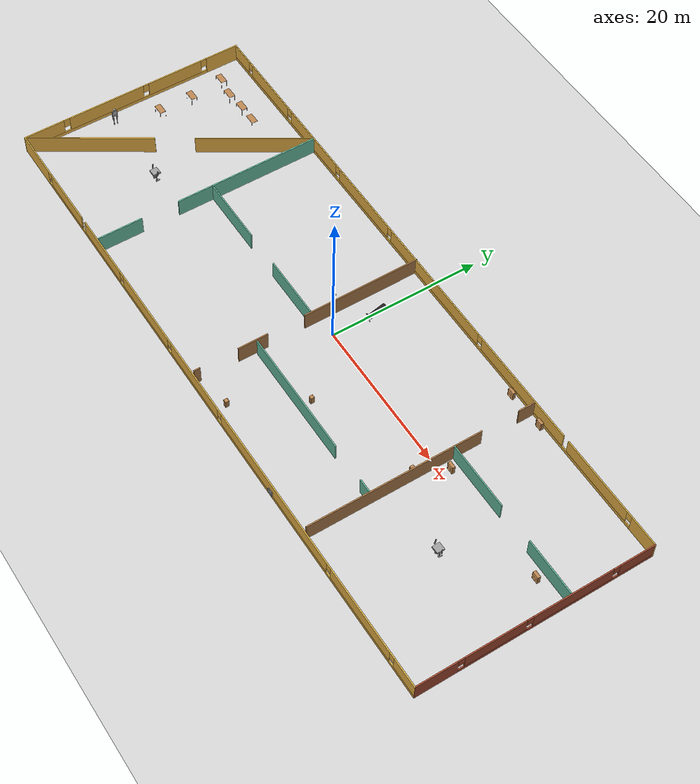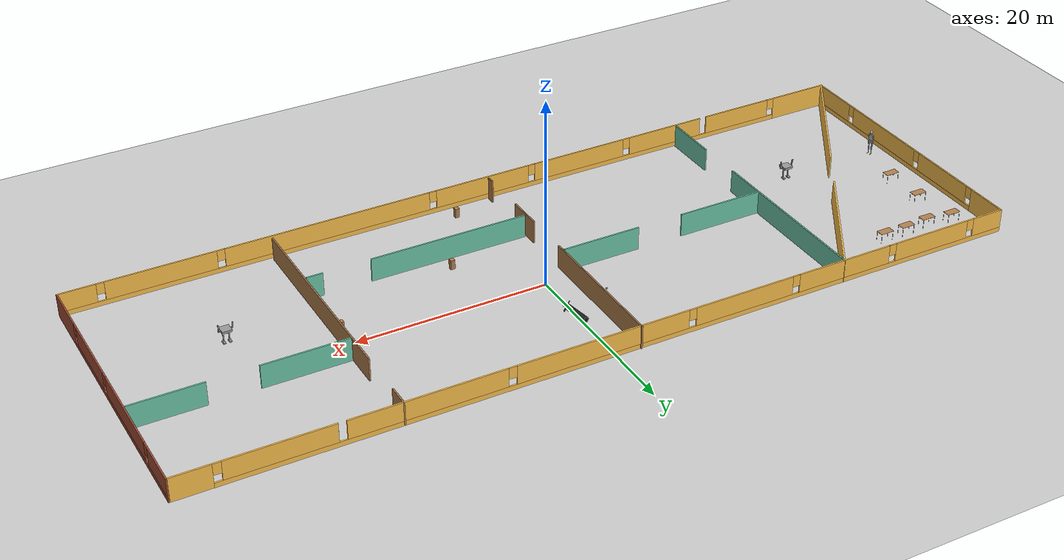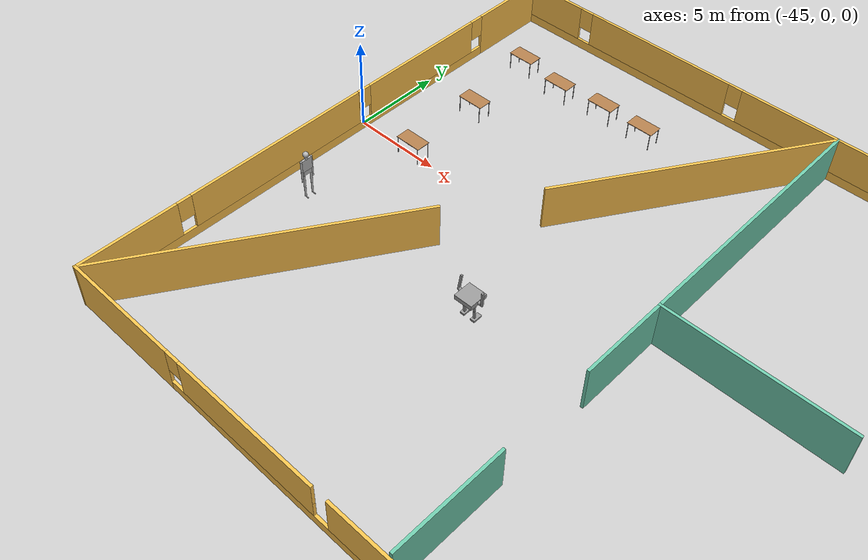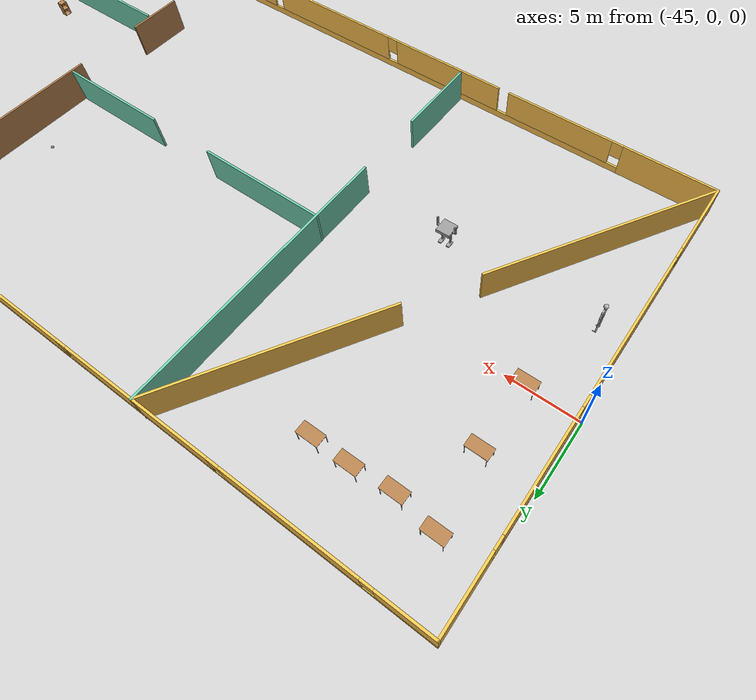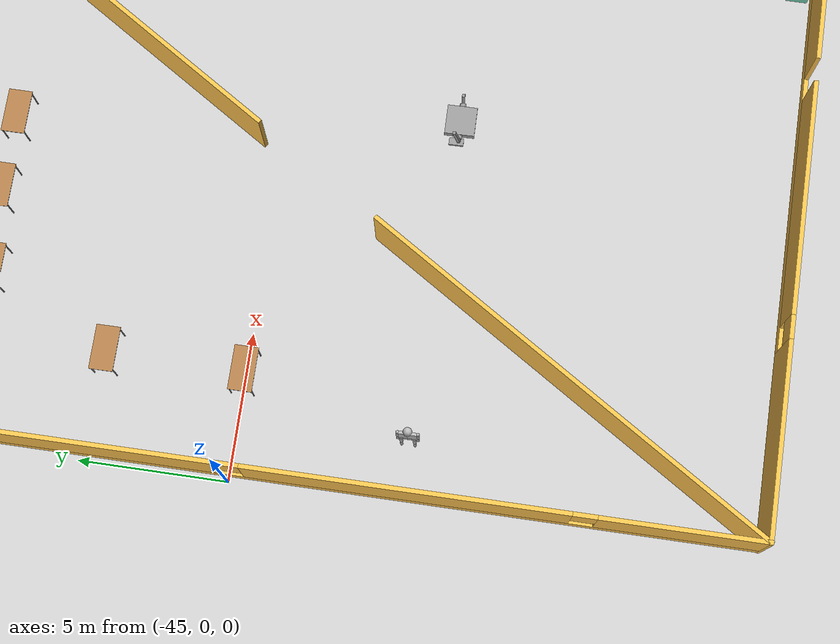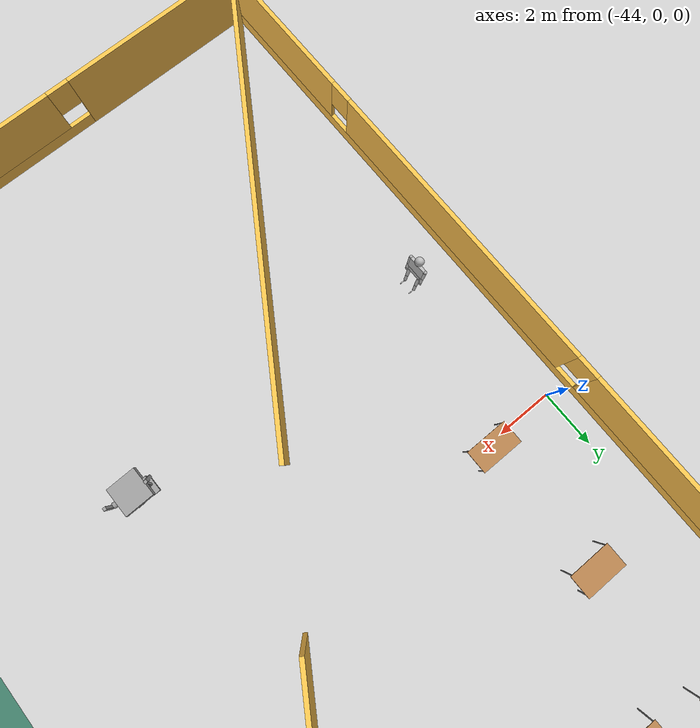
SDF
<sdf version="1.6">
 <world name="default">
  <plugin name="hello" filename="libproject1.so"/>
  <light name="sun" type="directional">
   <pose>0 0 10 0 -0 0</pose>
   <diffuse>0.8 0.8 0.8 1</diffuse>
   <specular>0.2 0.2 0.2 1</specular>
   <attenuation>
    <range>1000</range>
    <constant>0.9</constant>
    <linear>0.01</linear>
    <quadratic>0.001</quadratic>
   </attenuation>
   <direction>-0.5 0.1 -0.9</direction>
  </light>
  <model name="ground_plane">
   <static>1</static>
   <link name="link">
    <collision name="collision">
     <geometry><plane><normal>0 0 1</normal><size>100 100</size></plane></geometry>
     <surface><friction><ode><mu>100</mu><mu2>50</mu2></ode></friction></surface>
    </collision>
    <visual name="visual">
     <cast_shadows>0</cast_shadows>
     <geometry><plane><normal>0 0 1</normal><size>100 100</size></plane></geometry>
     <material>
      <script><uri>file://media/materials/scripts/gazebo.material</uri><name>Gazebo/Grey</name></script>
     </material>
    </visual>
   </link>
  </model>
  <gravity>0 0 -9.8</gravity>
  <magnetic_field>6e-06 2.3e-05 -4.2e-05</magnetic_field>
  <atmosphere type="adiabatic"/>
  <physics name="default_physics" default="0" type="ode">
   <max_step_size>0.001</max_step_size>
   <real_time_factor>1</real_time_factor>
   <real_time_update_rate>1000</real_time_update_rate>
  </physics>
  <scene><ambient>0.4 0.4 0.4 1</ambient><background>0.7 0.7 0.7 1</background><shadows>1</shadows></scene>
  <spherical_coordinates>
   <surface_model>EARTH_WGS84</surface_model>
   <latitude_deg>0</latitude_deg>
   <longitude_deg>0</longitude_deg>
   <elevation>0</elevation>
   <heading_deg>0</heading_deg>
  </spherical_coordinates>
  <model name="Building_0">
   <pose>-1.0762 -1.9803 0 0 -0 0</pose>
   <link name="Wall_0">
    <pose>-43.6608 -0.039593 0 0 -0 -1.5708</pose>
    <visual name="Wall_0_Visual_0">
     <pose>-13.0828 0 1.25 0 -0 0</pose>
     <geometry><box><size>4.5844 0.15 2.5</size></box></geometry>
     <material>
      <script><uri>file://media/materials/scripts/gazebo.material</uri><name>Gazebo/Grey</name></script>
      <ambient>1 0.764706 0.305882 1</ambient>
     </material>
     <meta><layer>0</layer></meta>
    </visual>
    <collision name="Wall_0_Collision_0">
     <geometry><box><size>4.5844 0.15 2.5</size></box></geometry>
     <pose>-13.0828 0 1.25 0 -0 0</pose>
    </collision>
    <visual name="Wall_0_Visual_1">
     <pose>2.2922 0 0.25 0 -0 0</pose>
     <geometry><box><size>26.1656 0.15 0.5</size></box></geometry>
     <material>
      <script><uri>file://media/materials/scripts/gazebo.material</uri><name>Gazebo/Grey</name></script>
      <ambient>1 0.764706 0.305882 1</ambient>
     </material>
     <meta><layer>0</layer></meta>
    </visual>
    <collision name="Wall_0_Collision_1">
     <geometry><box><size>26.1656 0.15 0.5</size></box></geometry>
     <pose>2.2922 0 0.25 0 -0 0</pose>
    </collision>
    <visual name="Wall_0_Visual_2">
     <pose>-6.1399 0 1.5 0 -0 0</pose>
     <geometry><box><size>7.7014 0.15 2</size></box></geometry>
     <material>
      <script><uri>file://media/materials/scripts/gazebo.material</uri><name>Gazebo/Grey</name></script>
      <ambient>1 0.764706 0.305882 1</ambient>
     </material>
     <meta><layer>0</layer></meta>
    </visual>
    <collision name="Wall_0_Collision_2">
     <geometry><box><size>7.7014 0.15 2</size></box></geometry>
     <pose>-6.1399 0 1.5 0 -0 0</pose>
    </collision>
    <visual name="Wall_0_Visual_3">
     <pose>3.79701 0 1.5 0 -0 0</pose>
     <geometry><box><size>10.5724 0.15 2</size></box></geometry>
     <material>
      <script><uri>file://media/materials/scripts/gazebo.material</uri><name>Gazebo/Grey</name></script>
      <ambient>1 0.764706 0.305882 1</ambient>
     </material>
     <meta><layer>0</layer></meta>
    </visual>
    <collision name="Wall_0_Collision_3">
     <geometry><box><size>10.5724 0.15 2</size></box></geometry>
     <pose>3.79701 0 1.5 0 -0 0</pose>
    </collision>
    <visual name="Wall_0_Visual_4">
     <pose>12.6291 0 1.5 0 -0 0</pose>
     <geometry><box><size>5.49178 0.15 2</size></box></geometry>
     <material>
      <script><uri>file://media/materials/scripts/gazebo.material</uri><name>Gazebo/Grey</name></script>
      <ambient>1 0.764706 0.305882 1</ambient>
     </material>
     <meta><layer>0</layer></meta>
    </visual>
    <collision name="Wall_0_Collision_4">
     <geometry><box><size>5.49178 0.15 2</size></box></geometry>
     <pose>12.6291 0 1.5 0 -0 0</pose>
    </collision>
    <visual name="Wall_0_Visual_5">
     <pose>-10.3906 0 1.9 0 -0 0</pose>
     <geometry><box><size>0.8 0.15 1.2</size></box></geometry>
     <material>
      <script><uri>file://media/materials/scripts/gazebo.material</uri><name>Gazebo/Grey</name></script>
      <ambient>1 0.764706 0.305882 1</ambient>
     </material>
     <meta><layer>0</layer></meta>
    </visual>
    <collision name="Wall_0_Collision_5">
     <geometry><box><size>0.8 0.15 1.2</size></box></geometry>
     <pose>-10.3906 0 1.9 0 -0 0</pose>
    </collision>
    <visual name="Wall_0_Visual_6">
     <pose>-1.8892 0 1.9 0 -0 0</pose>
     <geometry><box><size>0.8 0.15 1.2</size></box></geometry>
     <material>
      <script><uri>file://media/materials/scripts/gazebo.material</uri><name>Gazebo/Grey</name></script>
      <ambient>1 0.764706 0.305882 1</ambient>
     </material>
     <meta><layer>0</layer></meta>
    </visual>
    <collision name="Wall_0_Collision_6">
     <geometry><box><size>0.8 0.15 1.2</size></box></geometry>
     <pose>-1.8892 0 1.9 0 -0 0</pose>
    </collision>
    <visual name="Wall_0_Visual_7">
     <pose>9.48322 0 1.9 0 -0 0</pose>
     <geometry><box><size>0.8 0.15 1.2</size></box></geometry>
     <material>
      <script><uri>file://media/materials/scripts/gazebo.material</uri><name>Gazebo/Grey</name></script>
      <ambient>1 0.764706 0.305882 1</ambient>
     </material>
     <meta><layer>0</layer></meta>
    </visual>
    <collision name="Wall_0_Collision_7">
     <geometry><box><size>0.8 0.15 1.2</size></box></geometry>
     <pose>9.48322 0 1.9 0 -0 0</pose>
    </collision>
   </link>
   <link name="Wall_1">
    <pose>0.014212 -15.3396 0 0 -0 0</pose>
    <visual name="Wall_1_Visual_0">
     <pose>-40.4458 0 1.25 0 -0 0</pose>
     <geometry><box><size>6.6085 0.15 2.5</size></box></geometry>
     <material>
      <script><uri>file://media/materials/scripts/gazebo.material</uri><name>Gazebo/Grey</name></script>
      <ambient>1 0.764706 0.305882 1</ambient>
     </material>
     <meta><layer>0</layer></meta>
    </visual>
    <collision name="Wall_1_Collision_0">
     <geometry><box><size>6.6085 0.15 2.5</size></box></geometry>
     <pose>-40.4458 0 1.25 0 -0 0</pose>
    </collision>
    <visual name="Wall_1_Visual_1">
     <pose>3.30425 0 0.25 0 -0 0</pose>
     <geometry><box><size>80.8915 0.15 0.5</size></box></geometry>
     <material>
      <script><uri>file://media/materials/scripts/gazebo.material</uri><name>Gazebo/Grey</name></script>
      <ambient>1 0.764706 0.305882 1</ambient>
     </material>
     <meta><layer>0</layer></meta>
    </visual>
    <collision name="Wall_1_Collision_1">
     <geometry><box><size>80.8915 0.15 0.5</size></box></geometry>
     <pose>3.30425 0 0.25 0 -0 0</pose>
    </collision>
    <visual name="Wall_1_Visual_2">
     <pose>-32.3294 0 1.5 0 -0 0</pose>
     <geometry><box><size>8.02424 0.15 2</size></box></geometry>
     <material>
      <script><uri>file://media/materials/scripts/gazebo.material</uri><name>Gazebo/Grey</name></script>
      <ambient>1 0.764706 0.305882 1</ambient>
     </material>
     <meta><layer>0</layer></meta>
    </visual>
    <collision name="Wall_1_Collision_2">
     <geometry><box><size>8.02424 0.15 2</size></box></geometry>
     <pose>-32.3294 0 1.5 0 -0 0</pose>
    </collision>
    <visual name="Wall_1_Visual_3">
     <pose>-23.0747 0 1.5 0 -0 0</pose>
     <geometry><box><size>8.88514 0.15 2</size></box></geometry>
     <material>
      <script><uri>file://media/materials/scripts/gazebo.material</uri><name>Gazebo/Grey</name></script>
      <ambient>1 0.764706 0.305882 1</ambient>
     </material>
     <meta><layer>0</layer></meta>
    </visual>
    <collision name="Wall_1_Collision_3">
     <geometry><box><size>8.88514 0.15 2</size></box></geometry>
     <pose>-23.0747 0 1.5 0 -0 0</pose>
    </collision>
    <visual name="Wall_1_Visual_4">
     <pose>-12.4749 0 1.5 0 -0 0</pose>
     <geometry><box><size>10.7146 0.15 2</size></box></geometry>
     <material>
      <script><uri>file://media/materials/scripts/gazebo.material</uri><name>Gazebo/Grey</name></script>
      <ambient>1 0.764706 0.305882 1</ambient>
     </material>
     <meta><layer>0</layer></meta>
    </visual>
    <collision name="Wall_1_Collision_4">
     <geometry><box><size>10.7146 0.15 2</size></box></geometry>
     <pose>-12.4749 0 1.5 0 -0 0</pose>
    </collision>
    <visual name="Wall_1_Visual_5">
     <pose>-1.01411 0 1.5 0 -0 0</pose>
     <geometry><box><size>10.6069 0.15 2</size></box></geometry>
     <material>
      <script><uri>file://media/materials/scripts/gazebo.material</uri><name>Gazebo/Grey</name></script>
      <ambient>1 0.764706 0.305882 1</ambient>
     </material>
     <meta><layer>0</layer></meta>
    </visual>
    <collision name="Wall_1_Collision_5">
     <geometry><box><size>10.6069 0.15 2</size></box></geometry>
     <pose>-1.01411 0 1.5 0 -0 0</pose>
    </collision>
    <visual name="Wall_1_Visual_6">
     <pose>16.0963 0 1.5 0 -0 0</pose>
     <geometry><box><size>22.0139 0.15 2</size></box></geometry>
     <material>
      <script><uri>file://media/materials/scripts/gazebo.material</uri><name>Gazebo/Grey</name></script>
      <ambient>1 0.764706 0.305882 1</ambient>
     </material>
     <meta><layer>0</layer></meta>
    </visual>
    <collision name="Wall_1_Collision_6">
     <geometry><box><size>22.0139 0.15 2</size></box></geometry>
     <pose>16.0963 0 1.5 0 -0 0</pose>
    </collision>
    <visual name="Wall_1_Visual_7">
     <pose>33.5296 0 1.5 0 -0 0</pose>
     <geometry><box><size>11.2526 0.15 2</size></box></geometry>
     <material>
      <script><uri>file://media/materials/scripts/gazebo.material</uri><name>Gazebo/Grey</name></script>
      <ambient>1 0.764706 0.305882 1</ambient>
     </material>
     <meta><layer>0</layer></meta>
    </visual>
    <collision name="Wall_1_Collision_7">
     <geometry><box><size>11.2526 0.15 2</size></box></geometry>
     <pose>33.5296 0 1.5 0 -0 0</pose>
    </collision>
    <visual name="Wall_1_Visual_8">
     <pose>41.8529 0 1.5 0 -0 0</pose>
     <geometry><box><size>3.79414 0.15 2</size></box></geometry>
     <material>
      <script><uri>file://media/materials/scripts/gazebo.material</uri><name>Gazebo/Grey</name></script>
      <ambient>1 0.764706 0.305882 1</ambient>
     </material>
     <meta><layer>0</layer></meta>
    </visual>
    <collision name="Wall_1_Collision_8">
     <geometry><box><size>3.79414 0.15 2</size></box></geometry>
     <pose>41.8529 0 1.5 0 -0 0</pose>
    </collision>
    <visual name="Wall_1_Visual_9">
     <pose>-36.7415 0 1.9 0 -0 0</pose>
     <geometry><box><size>0.8 0.15 1.2</size></box></geometry>
     <material>
      <script><uri>file://media/materials/scripts/gazebo.material</uri><name>Gazebo/Grey</name></script>
      <ambient>1 0.764706 0.305882 1</ambient>
     </material>
     <meta><layer>0</layer></meta>
    </visual>
    <collision name="Wall_1_Collision_9">
     <geometry><box><size>0.8 0.15 1.2</size></box></geometry>
     <pose>-36.7415 0 1.9 0 -0 0</pose>
    </collision>
    <visual name="Wall_1_Visual_10">
     <pose>-28.3173 0 1.9 0 -0 0</pose>
     <geometry><box><size>0.001 0.15 1.2</size></box></geometry>
     <material>
      <script><uri>file://media/materials/scripts/gazebo.material</uri><name>Gazebo/Grey</name></script>
      <ambient>1 0.764706 0.305882 1</ambient>
     </material>
     <meta><layer>0</layer></meta>
    </visual>
    <collision name="Wall_1_Collision_10">
     <geometry><box><size>0.001 0.15 1.2</size></box></geometry>
     <pose>-28.3173 0 1.9 0 -0 0</pose>
    </collision>
    <visual name="Wall_1_Visual_11">
     <pose>-18.2321 0 1.9 0 -0 0</pose>
     <geometry><box><size>0.8 0.15 1.2</size></box></geometry>
     <material>
      <script><uri>file://media/materials/scripts/gazebo.material</uri><name>Gazebo/Grey</name></script>
      <ambient>1 0.764706 0.305882 1</ambient>
     </material>
     <meta><layer>0</layer></meta>
    </visual>
    <collision name="Wall_1_Collision_11">
     <geometry><box><size>0.8 0.15 1.2</size></box></geometry>
     <pose>-18.2321 0 1.9 0 -0 0</pose>
    </collision>
    <visual name="Wall_1_Visual_12">
     <pose>-6.71758 0 1.9 0 -0 0</pose>
     <geometry><box><size>0.8 0.15 1.2</size></box></geometry>
     <material>
      <script><uri>file://media/materials/scripts/gazebo.material</uri><name>Gazebo/Grey</name></script>
      <ambient>1 0.764706 0.305882 1</ambient>
     </material>
     <meta><layer>0</layer></meta>
    </visual>
    <collision name="Wall_1_Collision_12">
     <geometry><box><size>0.8 0.15 1.2</size></box></geometry>
     <pose>-6.71758 0 1.9 0 -0 0</pose>
    </collision>
    <visual name="Wall_1_Visual_13">
     <pose>4.68936 0 1.9 0 -0 0</pose>
     <geometry><box><size>0.8 0.15 1.2</size></box></geometry>
     <material>
      <script><uri>file://media/materials/scripts/gazebo.material</uri><name>Gazebo/Grey</name></script>
      <ambient>1 0.764706 0.305882 1</ambient>
     </material>
     <meta><layer>0</layer></meta>
    </visual>
    <collision name="Wall_1_Collision_13">
     <geometry><box><size>0.8 0.15 1.2</size></box></geometry>
     <pose>4.68936 0 1.9 0 -0 0</pose>
    </collision>
    <visual name="Wall_1_Visual_14">
     <pose>27.5032 0 1.9 0 -0 0</pose>
     <geometry><box><size>0.8 0.15 1.2</size></box></geometry>
     <material>
      <script><uri>file://media/materials/scripts/gazebo.material</uri><name>Gazebo/Grey</name></script>
      <ambient>1 0.764706 0.305882 1</ambient>
     </material>
     <meta><layer>0</layer></meta>
    </visual>
    <collision name="Wall_1_Collision_14">
     <geometry><box><size>0.8 0.15 1.2</size></box></geometry>
     <pose>27.5032 0 1.9 0 -0 0</pose>
    </collision>
    <visual name="Wall_1_Visual_15">
     <pose>39.5559 0 1.9 0 -0 0</pose>
     <geometry><box><size>0.8 0.15 1.2</size></box></geometry>
     <material>
      <script><uri>file://media/materials/scripts/gazebo.material</uri><name>Gazebo/Grey</name></script>
      <ambient>1 0.764706 0.305882 1</ambient>
     </material>
     <meta><layer>0</layer></meta>
    </visual>
    <collision name="Wall_1_Collision_15">
     <geometry><box><size>0.8 0.15 1.2</size></box></geometry>
     <pose>39.5559 0 1.9 0 -0 0</pose>
    </collision>
   </link>
   <link name="Wall_11">
    <pose>32.9634 4.28392 0 0 -0 0</pose>
    <visual name="Wall_11_Visual_0">
     <pose>-6.17941 0 1.25 0 -0 0</pose>
     <geometry><box><size>8.89118 0.15 2.5</size></box></geometry>
     <material>
      <script><uri>file://media/materials/scripts/gazebo.material</uri><name>Gazebo/Grey</name></script>
      <ambient>0.435294 0.796078 0.67451 1</ambient>
     </material>
     <meta><layer>0</layer></meta>
    </visual>
    <collision name="Wall_11_Collision_0">
     <geometry><box><size>8.89118 0.15 2.5</size></box></geometry>
     <pose>-6.17941 0 1.25 0 -0 0</pose>
    </collision>
    <visual name="Wall_11_Visual_1">
     <pose>6.94559 0 1.25 0 -0 0</pose>
     <geometry><box><size>7.35882 0.15 2.5</size></box></geometry>
     <material>
      <script><uri>file://media/materials/scripts/gazebo.material</uri><name>Gazebo/Grey</name></script>
      <ambient>0.435294 0.796078 0.67451 1</ambient>
     </material>
     <meta><layer>0</layer></meta>
    </visual>
    <collision name="Wall_11_Collision_1">
     <geometry><box><size>7.35882 0.15 2.5</size></box></geometry>
     <pose>6.94559 0 1.25 0 -0 0</pose>
    </collision>
   </link>
   <link name="Wall_13">
    <pose>10.4155 -6.80018 0 0 -0 3.14159</pose>
    <visual name="Wall_13_Visual_0">
     <pose>-10.8926 0 1.25 0 -0 0</pose>
     <geometry><box><size>1.71481 0.15 2.5</size></box></geometry>
     <material>
      <script><uri>file://media/materials/scripts/gazebo.material</uri><name>Gazebo/Grey</name></script>
      <ambient>0.435294 0.796078 0.67451 1</ambient>
     </material>
     <meta><layer>0</layer></meta>
    </visual>
    <collision name="Wall_13_Collision_0">
     <geometry><box><size>1.71481 0.15 2.5</size></box></geometry>
     <pose>-10.8926 0 1.25 0 -0 0</pose>
    </collision>
    <visual name="Wall_13_Visual_1">
     <pose>3.3574 0 1.25 0 -0 0</pose>
     <geometry><box><size>16.7852 0.15 2.5</size></box></geometry>
     <material>
      <script><uri>file://media/materials/scripts/gazebo.material</uri><name>Gazebo/Grey</name></script>
      <ambient>0.435294 0.796078 0.67451 1</ambient>
     </material>
     <meta><layer>0</layer></meta>
    </visual>
    <collision name="Wall_13_Collision_1">
     <geometry><box><size>16.7852 0.15 2.5</size></box></geometry>
     <pose>3.3574 0 1.25 0 -0 0</pose>
    </collision>
   </link>
   <link name="Wall_15">
    <pose>-13.0981 0.625087 0 0 -0 0</pose>
    <visual name="Wall_15_Visual_0">
     <pose>-6.69571 0 1.25 0 -0 0</pose>
     <geometry><box><size>9.35858 0.15 2.5</size></box></geometry>
     <material>
      <script><uri>file://media/materials/scripts/gazebo.material</uri><name>Gazebo/Grey</name></script>
      <ambient>0.435294 0.796078 0.67451 1</ambient>
     </material>
     <meta><layer>0</layer></meta>
    </visual>
    <collision name="Wall_15_Collision_0">
     <geometry><box><size>9.35858 0.15 2.5</size></box></geometry>
     <pose>-6.69571 0 1.25 0 -0 0</pose>
    </collision>
    <visual name="Wall_15_Visual_1">
     <pose>7.17929 0 1.25 0 -0 0</pose>
     <geometry><box><size>8.39142 0.15 2.5</size></box></geometry>
     <material>
      <script><uri>file://media/materials/scripts/gazebo.material</uri><name>Gazebo/Grey</name></script>
      <ambient>0.435294 0.796078 0.67451 1</ambient>
     </material>
     <meta><layer>0</layer></meta>
    </visual>
    <collision name="Wall_15_Collision_1">
     <geometry><box><size>8.39142 0.15 2.5</size></box></geometry>
     <pose>7.17929 0 1.25 0 -0 0</pose>
    </collision>
   </link>
   <link name="Wall_17">
    <pose>-34.0295 -0.039593 0 0 -0 1.00897</pose>
    <visual name="Wall_17_Visual_0">
     <pose>-9.99099 0 1.25 0 -0 0</pose>
     <geometry><box><size>16.3262 0.15 2.5</size></box></geometry>
     <material>
      <script><uri>file://media/materials/scripts/gazebo.material</uri><name>Gazebo/Grey</name></script>
      <ambient>1 0.764706 0.305882 1</ambient>
     </material>
     <meta><layer>0</layer></meta>
    </visual>
    <collision name="Wall_17_Collision_0">
     <geometry><box><size>16.3262 0.15 2.5</size></box></geometry>
     <pose>-9.99099 0 1.25 0 -0 0</pose>
    </collision>
    <visual name="Wall_17_Visual_1">
     <pose>10.6631 0 1.25 0 -0 0</pose>
     <geometry><box><size>14.982 0.15 2.5</size></box></geometry>
     <material>
      <script><uri>file://media/materials/scripts/gazebo.material</uri><name>Gazebo/Grey</name></script>
      <ambient>1 0.764706 0.305882 1</ambient>
     </material>
     <meta><layer>0</layer></meta>
    </visual>
    <collision name="Wall_17_Collision_1">
     <geometry><box><size>14.982 0.15 2.5</size></box></geometry>
     <pose>10.6631 0 1.25 0 -0 0</pose>
    </collision>
   </link>
   <link name="Wall_2">
    <pose>43.6892 -0.039593 0 0 -0 1.5708</pose>
    <visual name="Wall_2_Visual_0">
     <pose>-12.6829 0 1.25 0 -0 0</pose>
     <geometry><box><size>5.38417 0.15 2.5</size></box></geometry>
     <material>
      <script><uri>file://media/materials/scripts/gazebo.material</uri><name>Gazebo/Bricks</name></script>
      <ambient>1 1 1 1</ambient>
     </material>
     <meta><layer>0</layer></meta>
    </visual>
    <collision name="Wall_2_Collision_0">
     <geometry><box><size>5.38417 0.15 2.5</size></box></geometry>
     <pose>-12.6829 0 1.25 0 -0 0</pose>
    </collision>
    <visual name="Wall_2_Visual_1">
     <pose>2.69209 0 0.25 0 -0 0</pose>
     <geometry><box><size>25.3658 0.15 0.5</size></box></geometry>
     <material>
      <script><uri>file://media/materials/scripts/gazebo.material</uri><name>Gazebo/Bricks</name></script>
      <ambient>1 1 1 1</ambient>
     </material>
     <meta><layer>0</layer></meta>
    </visual>
    <collision name="Wall_2_Collision_1">
     <geometry><box><size>25.3658 0.15 0.5</size></box></geometry>
     <pose>2.69209 0 0.25 0 -0 0</pose>
    </collision>
    <visual name="Wall_2_Visual_2">
     <pose>-5.28632 0 1.5 0 -0 0</pose>
     <geometry><box><size>7.80901 0.15 2</size></box></geometry>
     <material>
      <script><uri>file://media/materials/scripts/gazebo.material</uri><name>Gazebo/Bricks</name></script>
      <ambient>1 1 1 1</ambient>
     </material>
     <meta><layer>0</layer></meta>
    </visual>
    <collision name="Wall_2_Collision_2">
     <geometry><box><size>7.80901 0.15 2</size></box></geometry>
     <pose>-5.28632 0 1.5 0 -0 0</pose>
    </collision>
    <visual name="Wall_2_Visual_3">
     <pose>4.61404 0 1.5 0 -0 0</pose>
     <geometry><box><size>10.3917 0.15 2</size></box></geometry>
     <material>
      <script><uri>file://media/materials/scripts/gazebo.material</uri><name>Gazebo/Bricks</name></script>
      <ambient>1 1 1 1</ambient>
     </material>
     <meta><layer>0</layer></meta>
    </visual>
    <collision name="Wall_2_Collision_3">
     <geometry><box><size>10.3917 0.15 2</size></box></geometry>
     <pose>4.61404 0 1.5 0 -0 0</pose>
    </collision>
    <visual name="Wall_2_Visual_4">
     <pose>12.9924 0 1.5 0 -0 0</pose>
     <geometry><box><size>4.7651 0.15 2</size></box></geometry>
     <material>
      <script><uri>file://media/materials/scripts/gazebo.material</uri><name>Gazebo/Bricks</name></script>
      <ambient>1 1 1 1</ambient>
     </material>
     <meta><layer>0</layer></meta>
    </visual>
    <collision name="Wall_2_Collision_4">
     <geometry><box><size>4.7651 0.15 2</size></box></geometry>
     <pose>12.9924 0 1.5 0 -0 0</pose>
    </collision>
    <visual name="Wall_2_Visual_5">
     <pose>-9.59083 0 1.9 0 -0 0</pose>
     <geometry><box><size>0.8 0.15 1.2</size></box></geometry>
     <material>
      <script><uri>file://media/materials/scripts/gazebo.material</uri><name>Gazebo/Bricks</name></script>
      <ambient>1 1 1 1</ambient>
     </material>
     <meta><layer>0</layer></meta>
    </visual>
    <collision name="Wall_2_Collision_5">
     <geometry><box><size>0.8 0.15 1.2</size></box></geometry>
     <pose>-9.59083 0 1.9 0 -0 0</pose>
    </collision>
    <visual name="Wall_2_Visual_6">
     <pose>-0.981818 0 1.9 0 -0 0</pose>
     <geometry><box><size>0.8 0.15 1.2</size></box></geometry>
     <material>
      <script><uri>file://media/materials/scripts/gazebo.material</uri><name>Gazebo/Bricks</name></script>
      <ambient>1 1 1 1</ambient>
     </material>
     <meta><layer>0</layer></meta>
    </visual>
    <collision name="Wall_2_Collision_6">
     <geometry><box><size>0.8 0.15 1.2</size></box></geometry>
     <pose>-0.981818 0 1.9 0 -0 0</pose>
    </collision>
    <visual name="Wall_2_Visual_7">
     <pose>10.2099 0 1.9 0 -0 0</pose>
     <geometry><box><size>0.8 0.15 1.2</size></box></geometry>
     <material>
      <script><uri>file://media/materials/scripts/gazebo.material</uri><name>Gazebo/Bricks</name></script>
      <ambient>1 1 1 1</ambient>
     </material>
     <meta><layer>0</layer></meta>
    </visual>
    <collision name="Wall_2_Collision_7">
     <geometry><box><size>0.8 0.15 1.2</size></box></geometry>
     <pose>10.2099 0 1.9 0 -0 0</pose>
    </collision>
   </link>
   <link name="Wall_3">
    <pose>0.014212 15.2604 0 0 -0 3.14159</pose>
    <visual name="Wall_3_Visual_0">
     <pose>-41.7453 0 1.25 0 -0 0</pose>
     <geometry><box><size>4.00936 0.15 2.5</size></box></geometry>
     <material>
      <script><uri>file://media/materials/scripts/gazebo.material</uri><name>Gazebo/Grey</name></script>
      <ambient>1 0.764706 0.305882 1</ambient>
     </material>
     <meta><layer>0</layer></meta>
    </visual>
    <collision name="Wall_3_Collision_0">
     <geometry><box><size>4.00936 0.15 2.5</size></box></geometry>
     <pose>-41.7453 0 1.25 0 -0 0</pose>
    </collision>
    <visual name="Wall_3_Visual_1">
     <pose>2.00468 0 0.25 0 -0 0</pose>
     <geometry><box><size>83.4906 0.15 0.5</size></box></geometry>
     <material>
      <script><uri>file://media/materials/scripts/gazebo.material</uri><name>Gazebo/Grey</name></script>
      <ambient>1 0.764706 0.305882 1</ambient>
     </material>
     <meta><layer>0</layer></meta>
    </visual>
    <collision name="Wall_3_Collision_1">
     <geometry><box><size>83.4906 0.15 0.5</size></box></geometry>
     <pose>2.00468 0 0.25 0 -0 0</pose>
    </collision>
    <visual name="Wall_3_Visual_2">
     <pose>-33.691 0 1.5 0 -0 0</pose>
     <geometry><box><size>10.4993 0.15 2</size></box></geometry>
     <material>
      <script><uri>file://media/materials/scripts/gazebo.material</uri><name>Gazebo/Grey</name></script>
      <ambient>1 0.764706 0.305882 1</ambient>
     </material>
     <meta><layer>0</layer></meta>
    </visual>
    <collision name="Wall_3_Collision_2">
     <geometry><box><size>10.4993 0.15 2</size></box></geometry>
     <pose>-33.691 0 1.5 0 -0 0</pose>
    </collision>
    <visual name="Wall_3_Visual_3">
     <pose>-19.8627 0 1.5 0 -0 0</pose>
     <geometry><box><size>15.5571 0.15 2</size></box></geometry>
     <material>
      <script><uri>file://media/materials/scripts/gazebo.material</uri><name>Gazebo/Grey</name></script>
      <ambient>1 0.764706 0.305882 1</ambient>
     </material>
     <meta><layer>0</layer></meta>
    </visual>
    <collision name="Wall_3_Collision_3">
     <geometry><box><size>15.5571 0.15 2</size></box></geometry>
     <pose>-19.8627 0 1.5 0 -0 0</pose>
    </collision>
    <visual name="Wall_3_Visual_4">
     <pose>-2.25554 0 1.5 0 -0 0</pose>
     <geometry><box><size>18.0573 0.15 2</size></box></geometry>
     <material>
      <script><uri>file://media/materials/scripts/gazebo.material</uri><name>Gazebo/Grey</name></script>
      <ambient>1 0.764706 0.305882 1</ambient>
     </material>
     <meta><layer>0</layer></meta>
    </visual>
    <collision name="Wall_3_Collision_4">
     <geometry><box><size>18.0573 0.15 2</size></box></geometry>
     <pose>-2.25554 0 1.5 0 -0 0</pose>
    </collision>
    <visual name="Wall_3_Visual_5">
     <pose>12.9842 0 1.5 0 -0 0</pose>
     <geometry><box><size>10.8222 0.15 2</size></box></geometry>
     <material>
      <script><uri>file://media/materials/scripts/gazebo.material</uri><name>Gazebo/Grey</name></script>
      <ambient>1 0.764706 0.305882 1</ambient>
     </material>
     <meta><layer>0</layer></meta>
    </visual>
    <collision name="Wall_3_Collision_5">
     <geometry><box><size>10.8222 0.15 2</size></box></geometry>
     <pose>12.9842 0 1.5 0 -0 0</pose>
    </collision>
    <visual name="Wall_3_Visual_6">
     <pose>24.4987 0 1.5 0 -0 0</pose>
     <geometry><box><size>10.6069 0.15 2</size></box></geometry>
     <material>
      <script><uri>file://media/materials/scripts/gazebo.material</uri><name>Gazebo/Grey</name></script>
      <ambient>1 0.764706 0.305882 1</ambient>
     </material>
     <meta><layer>0</layer></meta>
    </visual>
    <collision name="Wall_3_Collision_6">
     <geometry><box><size>10.6069 0.15 2</size></box></geometry>
     <pose>24.4987 0 1.5 0 -0 0</pose>
    </collision>
    <visual name="Wall_3_Visual_7">
     <pose>34.991 0 1.5 0 -0 0</pose>
     <geometry><box><size>8.77752 0.15 2</size></box></geometry>
     <material>
      <script><uri>file://media/materials/scripts/gazebo.material</uri><name>Gazebo/Grey</name></script>
      <ambient>1 0.764706 0.305882 1</ambient>
     </material>
     <meta><layer>0</layer></meta>
    </visual>
    <collision name="Wall_3_Collision_7">
     <geometry><box><size>8.77752 0.15 2</size></box></geometry>
     <pose>34.991 0 1.5 0 -0 0</pose>
    </collision>
    <visual name="Wall_3_Visual_8">
     <pose>41.9649 0 1.5 0 -0 0</pose>
     <geometry><box><size>3.57027 0.15 2</size></box></geometry>
     <material>
      <script><uri>file://media/materials/scripts/gazebo.material</uri><name>Gazebo/Grey</name></script>
      <ambient>1 0.764706 0.305882 1</ambient>
     </material>
     <meta><layer>0</layer></meta>
    </visual>
    <collision name="Wall_3_Collision_8">
     <geometry><box><size>3.57027 0.15 2</size></box></geometry>
     <pose>41.9649 0 1.5 0 -0 0</pose>
    </collision>
    <visual name="Wall_3_Visual_9">
     <pose>-39.3406 0 1.9 0 -0 0</pose>
     <geometry><box><size>0.8 0.15 1.2</size></box></geometry>
     <material>
      <script><uri>file://media/materials/scripts/gazebo.material</uri><name>Gazebo/Grey</name></script>
      <ambient>1 0.764706 0.305882 1</ambient>
     </material>
     <meta><layer>0</layer></meta>
    </visual>
    <collision name="Wall_3_Collision_9">
     <geometry><box><size>0.8 0.15 1.2</size></box></geometry>
     <pose>-39.3406 0 1.9 0 -0 0</pose>
    </collision>
    <visual name="Wall_3_Visual_10">
     <pose>-28.4413 0 1.9 0 -0 0</pose>
     <geometry><box><size>0.001 0.15 1.2</size></box></geometry>
     <material>
      <script><uri>file://media/materials/scripts/gazebo.material</uri><name>Gazebo/Grey</name></script>
      <ambient>1 0.764706 0.305882 1</ambient>
     </material>
     <meta><layer>0</layer></meta>
    </visual>
    <collision name="Wall_3_Collision_10">
     <geometry><box><size>0.001 0.15 1.2</size></box></geometry>
     <pose>-28.4413 0 1.9 0 -0 0</pose>
    </collision>
    <visual name="Wall_3_Visual_11">
     <pose>-11.6842 0 1.9 0 -0 0</pose>
     <geometry><box><size>0.8 0.15 1.2</size></box></geometry>
     <material>
      <script><uri>file://media/materials/scripts/gazebo.material</uri><name>Gazebo/Grey</name></script>
      <ambient>1 0.764706 0.305882 1</ambient>
     </material>
     <meta><layer>0</layer></meta>
    </visual>
    <collision name="Wall_3_Collision_11">
     <geometry><box><size>0.8 0.15 1.2</size></box></geometry>
     <pose>-11.6842 0 1.9 0 -0 0</pose>
    </collision>
    <visual name="Wall_3_Visual_12">
     <pose>7.1731 0 1.9 0 -0 0</pose>
     <geometry><box><size>0.8 0.15 1.2</size></box></geometry>
     <material>
      <script><uri>file://media/materials/scripts/gazebo.material</uri><name>Gazebo/Grey</name></script>
      <ambient>1 0.764706 0.305882 1</ambient>
     </material>
     <meta><layer>0</layer></meta>
    </visual>
    <collision name="Wall_3_Collision_12">
     <geometry><box><size>0.8 0.15 1.2</size></box></geometry>
     <pose>7.1731 0 1.9 0 -0 0</pose>
    </collision>
    <visual name="Wall_3_Visual_13">
     <pose>18.7953 0 1.9 0 -0 0</pose>
     <geometry><box><size>0.8 0.15 1.2</size></box></geometry>
     <material>
      <script><uri>file://media/materials/scripts/gazebo.material</uri><name>Gazebo/Grey</name></script>
      <ambient>1 0.764706 0.305882 1</ambient>
     </material>
     <meta><layer>0</layer></meta>
    </visual>
    <collision name="Wall_3_Collision_13">
     <geometry><box><size>0.8 0.15 1.2</size></box></geometry>
     <pose>18.7953 0 1.9 0 -0 0</pose>
    </collision>
    <visual name="Wall_3_Visual_14">
     <pose>30.2022 0 1.9 0 -0 0</pose>
     <geometry><box><size>0.8 0.15 1.2</size></box></geometry>
     <material>
      <script><uri>file://media/materials/scripts/gazebo.material</uri><name>Gazebo/Grey</name></script>
      <ambient>1 0.764706 0.305882 1</ambient>
     </material>
     <meta><layer>0</layer></meta>
    </visual>
    <collision name="Wall_3_Collision_14">
     <geometry><box><size>0.8 0.15 1.2</size></box></geometry>
     <pose>30.2022 0 1.9 0 -0 0</pose>
    </collision>
    <visual name="Wall_3_Visual_15">
     <pose>39.7797 0 1.9 0 -0 0</pose>
     <geometry><box><size>0.8 0.15 1.2</size></box></geometry>
     <material>
      <script><uri>file://media/materials/scripts/gazebo.material</uri><name>Gazebo/Grey</name></script>
      <ambient>1 0.764706 0.305882 1</ambient>
     </material>
     <meta><layer>0</layer></meta>
    </visual>
    <collision name="Wall_3_Collision_15">
     <geometry><box><size>0.8 0.15 1.2</size></box></geometry>
     <pose>39.7797 0 1.9 0 -0 0</pose>
    </collision>
   </link>
   <link name="Wall_5">
    <pose>-24.3981 0.085406 0 0 -0 -1.5708</pose>
    <visual name="Wall_5_Visual_0">
     <pose>-5.47838 0 1.25 0 -0 0</pose>
     <geometry><box><size>19.5432 0.15 2.5</size></box></geometry>
     <material>
      <script><uri>file://media/materials/scripts/gazebo.material</uri><name>Gazebo/Grey</name></script>
      <ambient>0.435294 0.796078 0.67451 1</ambient>
     </material>
     <meta><layer>0</layer></meta>
    </visual>
    <collision name="Wall_5_Collision_0">
     <geometry><box><size>19.5432 0.15 2.5</size></box></geometry>
     <pose>-5.47838 0 1.25 0 -0 0</pose>
    </collision>
    <visual name="Wall_5_Visual_1">
     <pose>12.2716 0 1.25 0 -0 0</pose>
     <geometry><box><size>5.95676 0.15 2.5</size></box></geometry>
     <material>
      <script><uri>file://media/materials/scripts/gazebo.material</uri><name>Gazebo/Grey</name></script>
      <ambient>0.435294 0.796078 0.67451 1</ambient>
     </material>
     <meta><layer>0</layer></meta>
    </visual>
    <collision name="Wall_5_Collision_1">
     <geometry><box><size>5.95676 0.15 2.5</size></box></geometry>
     <pose>12.2716 0 1.25 0 -0 0</pose>
    </collision>
   </link>
   <link name="Wall_7">
    <pose>-1.58424 0.193019 0 0 -0 -1.5708</pose>
    <visual name="Wall_7_Visual_0">
     <pose>-7.3997 0 1.25 0 -0 0</pose>
     <geometry><box><size>15.7006 0.15 2.5</size></box></geometry>
     <material>
      <script><uri>file://media/materials/scripts/gazebo.material</uri><name>Gazebo/Wood</name></script>
      <ambient>1 1 1 1</ambient>
     </material>
     <meta><layer>0</layer></meta>
    </visual>
    <collision name="Wall_7_Collision_0">
     <geometry><box><size>15.7006 0.15 2.5</size></box></geometry>
     <pose>-7.3997 0 1.25 0 -0 0</pose>
    </collision>
    <visual name="Wall_7_Visual_1">
     <pose>7.42902 0 1.25 0 -0 0</pose>
     <geometry><box><size>3.95685 0.15 2.5</size></box></geometry>
     <material>
      <script><uri>file://media/materials/scripts/gazebo.material</uri><name>Gazebo/Wood</name></script>
      <ambient>1 1 1 1</ambient>
     </material>
     <meta><layer>0</layer></meta>
    </visual>
    <collision name="Wall_7_Collision_1">
     <geometry><box><size>3.95685 0.15 2.5</size></box></geometry>
     <pose>7.42902 0 1.25 0 -0 0</pose>
    </collision>
    <visual name="Wall_7_Visual_2">
     <pose>14.8287 0 1.25 0 -0 0</pose>
     <geometry><box><size>0.842552 0.15 2.5</size></box></geometry>
     <material>
      <script><uri>file://media/materials/scripts/gazebo.material</uri><name>Gazebo/Wood</name></script>
      <ambient>1 1 1 1</ambient>
     </material>
     <meta><layer>0</layer></meta>
    </visual>
    <collision name="Wall_7_Collision_2">
     <geometry><box><size>0.842552 0.15 2.5</size></box></geometry>
     <pose>14.8287 0 1.25 0 -0 0</pose>
    </collision>
   </link>
   <link name="Wall_9">
    <pose>22.3058 0.210406 0 0 -0 -1.5708</pose>
    <visual name="Wall_9_Visual_0">
     <pose>-13.9494 0 1.25 0 -0 0</pose>
     <geometry><box><size>2.35123 0.15 2.5</size></box></geometry>
     <material>
      <script><uri>file://media/materials/scripts/gazebo.material</uri><name>Gazebo/Wood</name></script>
      <ambient>1 1 1 1</ambient>
     </material>
     <meta><layer>0</layer></meta>
    </visual>
    <collision name="Wall_9_Collision_0">
     <geometry><box><size>2.35123 0.15 2.5</size></box></geometry>
     <pose>-13.9494 0 1.25 0 -0 0</pose>
    </collision>
    <visual name="Wall_9_Visual_1">
     <pose>3.67561 0 1.25 0 -0 0</pose>
     <geometry><box><size>22.8988 0.15 2.5</size></box></geometry>
     <material>
      <script><uri>file://media/materials/scripts/gazebo.material</uri><name>Gazebo/Wood</name></script>
      <ambient>1 1 1 1</ambient>
     </material>
     <meta><layer>0</layer></meta>
    </visual>
    <collision name="Wall_9_Collision_1">
     <geometry><box><size>22.8988 0.15 2.5</size></box></geometry>
     <pose>3.67561 0 1.25 0 -0 0</pose>
    </collision>
   </link>
   <link name="Window_13">
    <collision name="Window_13_Collision">
     <geometry><box><size>0.8 0.17 0.8</size></box></geometry>
     <pose>0 0 0.4 0 -0 0</pose>
    </collision>
    <visual name="Window_13_Visual">
     <pose>0 0 0.4 0 -0 0</pose>
     <geometry><box><size>0.8 0.17 0.8</size></box></geometry>
     <material>
      <script><uri>file://media/materials/scripts/gazebo.material</uri><name>Gazebo/Grey</name></script>
     </material>
    </visual>
    <pose>15.7877 -15.4415 0.5 0 -0 0</pose>
   </link>
   <static>1</static>
  </model>
  <model name="table">
   <static>1</static>
   <link name="link">
    <collision name="surface">
     <pose>0 0 1 0 -0 0</pose>
     <geometry><box><size>1.5 0.8 0.03</size></box></geometry>
     <surface><friction><ode><mu>0.6</mu><mu2>0.6</mu2></ode></friction></surface>
    </collision>
    <visual name="visual1">
     <pose>0 0 1 0 -0 0</pose>
     <geometry><box><size>1.5 0.8 0.03</size></box></geometry>
     <material>
      <script><uri>file://media/materials/scripts/gazebo.material</uri><name>Gazebo/Wood</name></script>
     </material>
    </visual>
    <collision name="front_left_leg">
     <pose>0.68 0.38 0.5 0 -0 0</pose>
     <geometry><cylinder><radius>0.02</radius><length>1</length></cylinder></geometry>
    </collision>
    <visual name="front_left_leg">
     <pose>0.68 0.38 0.5 0 -0 0</pose>
     <geometry><cylinder><radius>0.02</radius><length>1</length></cylinder></geometry>
     <material>
      <script><uri>file://media/materials/scripts/gazebo.material</uri><name>Gazebo/Grey</name></script>
     </material>
    </visual>
    <collision name="front_right_leg">
     <pose>0.68 -0.38 0.5 0 -0 0</pose>
     <geometry><cylinder><radius>0.02</radius><length>1</length></cylinder></geometry>
    </collision>
    <visual name="front_right_leg">
     <pose>0.68 -0.38 0.5 0 -0 0</pose>
     <geometry><cylinder><radius>0.02</radius><length>1</length></cylinder></geometry>
     <material>
      <script><uri>file://media/materials/scripts/gazebo.material</uri><name>Gazebo/Grey</name></script>
     </material>
    </visual>
    <collision name="back_right_leg">
     <pose>-0.68 -0.38 0.5 0 -0 0</pose>
     <geometry><cylinder><radius>0.02</radius><length>1</length></cylinder></geometry>
    </collision>
    <visual name="back_right_leg">
     <pose>-0.68 -0.38 0.5 0 -0 0</pose>
     <geometry><cylinder><radius>0.02</radius><length>1</length></cylinder></geometry>
     <material>
      <script><uri>file://media/materials/scripts/gazebo.material</uri><name>Gazebo/Grey</name></script>
     </material>
    </visual>
    <collision name="back_left_leg">
     <pose>-0.68 0.38 0.5 0 -0 0</pose>
     <geometry><cylinder><radius>0.02</radius><length>1</length></cylinder></geometry>
    </collision>
    <visual name="back_left_leg">
     <pose>-0.68 0.38 0.5 0 -0 0</pose>
     <geometry><cylinder><radius>0.02</radius><length>1</length></cylinder></geometry>
     <material>
      <script><uri>file://media/materials/scripts/gazebo.material</uri><name>Gazebo/Grey</name></script>
     </material>
    </visual>
   </link>
   <pose>-41.9024 9.35949 0 0 -0 0</pose>
  </model>
  <model name="table_clone">
   <static>1</static>
   <link name="link">
    <collision name="surface">
     <pose>0 0 1 0 -0 0</pose>
     <geometry><box><size>1.5 0.8 0.03</size></box></geometry>
     <surface><friction><ode><mu>0.6</mu><mu2>0.6</mu2></ode></friction></surface>
    </collision>
    <visual name="visual1">
     <pose>0 0 1 0 -0 0</pose>
     <geometry><box><size>1.5 0.8 0.03</size></box></geometry>
     <material>
      <script><uri>file://media/materials/scripts/gazebo.material</uri><name>Gazebo/Wood</name></script>
     </material>
    </visual>
    <collision name="front_left_leg">
     <pose>0.68 0.38 0.5 0 -0 0</pose>
     <geometry><cylinder><radius>0.02</radius><length>1</length></cylinder></geometry>
    </collision>
    <visual name="front_left_leg">
     <pose>0.68 0.38 0.5 0 -0 0</pose>
     <geometry><cylinder><radius>0.02</radius><length>1</length></cylinder></geometry>
     <material>
      <script><uri>file://media/materials/scripts/gazebo.material</uri><name>Gazebo/Grey</name></script>
     </material>
    </visual>
    <collision name="front_right_leg">
     <pose>0.68 -0.38 0.5 0 -0 0</pose>
     <geometry><cylinder><radius>0.02</radius><length>1</length></cylinder></geometry>
    </collision>
    <visual name="front_right_leg">
     <pose>0.68 -0.38 0.5 0 -0 0</pose>
     <geometry><cylinder><radius>0.02</radius><length>1</length></cylinder></geometry>
     <material>
      <script><uri>file://media/materials/scripts/gazebo.material</uri><name>Gazebo/Grey</name></script>
     </material>
    </visual>
    <collision name="back_right_leg">
     <pose>-0.68 -0.38 0.5 0 -0 0</pose>
     <geometry><cylinder><radius>0.02</radius><length>1</length></cylinder></geometry>
    </collision>
    <visual name="back_right_leg">
     <pose>-0.68 -0.38 0.5 0 -0 0</pose>
     <geometry><cylinder><radius>0.02</radius><length>1</length></cylinder></geometry>
     <material>
      <script><uri>file://media/materials/scripts/gazebo.material</uri><name>Gazebo/Grey</name></script>
     </material>
    </visual>
    <collision name="back_left_leg">
     <pose>-0.68 0.38 0.5 0 -0 0</pose>
     <geometry><cylinder><radius>0.02</radius><length>1</length></cylinder></geometry>
    </collision>
    <visual name="back_left_leg">
     <pose>-0.68 0.38 0.5 0 -0 0</pose>
     <geometry><cylinder><radius>0.02</radius><length>1</length></cylinder></geometry>
     <material>
      <script><uri>file://media/materials/scripts/gazebo.material</uri><name>Gazebo/Grey</name></script>
     </material>
    </visual>
   </link>
   <pose>-39.0732 8.91712 0 0 -0 0</pose>
  </model>
  <model name="table_clone_0">
   <static>1</static>
   <link name="link">
    <collision name="surface">
     <pose>0 0 1 0 -0 0</pose>
     <geometry><box><size>1.5 0.8 0.03</size></box></geometry>
     <surface><friction><ode><mu>0.6</mu><mu2>0.6</mu2></ode></friction></surface>
    </collision>
    <visual name="visual1">
     <pose>0 0 1 0 -0 0</pose>
     <geometry><box><size>1.5 0.8 0.03</size></box></geometry>
     <material>
      <script><uri>file://media/materials/scripts/gazebo.material</uri><name>Gazebo/Wood</name></script>
     </material>
    </visual>
    <collision name="front_left_leg">
     <pose>0.68 0.38 0.5 0 -0 0</pose>
     <geometry><cylinder><radius>0.02</radius><length>1</length></cylinder></geometry>
    </collision>
    <visual name="front_left_leg">
     <pose>0.68 0.38 0.5 0 -0 0</pose>
     <geometry><cylinder><radius>0.02</radius><length>1</length></cylinder></geometry>
     <material>
      <script><uri>file://media/materials/scripts/gazebo.material</uri><name>Gazebo/Grey</name></script>
     </material>
    </visual>
    <collision name="front_right_leg">
     <pose>0.68 -0.38 0.5 0 -0 0</pose>
     <geometry><cylinder><radius>0.02</radius><length>1</length></cylinder></geometry>
    </collision>
    <visual name="front_right_leg">
     <pose>0.68 -0.38 0.5 0 -0 0</pose>
     <geometry><cylinder><radius>0.02</radius><length>1</length></cylinder></geometry>
     <material>
      <script><uri>file://media/materials/scripts/gazebo.material</uri><name>Gazebo/Grey</name></script>
     </material>
    </visual>
    <collision name="back_right_leg">
     <pose>-0.68 -0.38 0.5 0 -0 0</pose>
     <geometry><cylinder><radius>0.02</radius><length>1</length></cylinder></geometry>
    </collision>
    <visual name="back_right_leg">
     <pose>-0.68 -0.38 0.5 0 -0 0</pose>
     <geometry><cylinder><radius>0.02</radius><length>1</length></cylinder></geometry>
     <material>
      <script><uri>file://media/materials/scripts/gazebo.material</uri><name>Gazebo/Grey</name></script>
     </material>
    </visual>
    <collision name="back_left_leg">
     <pose>-0.68 0.38 0.5 0 -0 0</pose>
     <geometry><cylinder><radius>0.02</radius><length>1</length></cylinder></geometry>
    </collision>
    <visual name="back_left_leg">
     <pose>-0.68 0.38 0.5 0 -0 0</pose>
     <geometry><cylinder><radius>0.02</radius><length>1</length></cylinder></geometry>
     <material>
      <script><uri>file://media/materials/scripts/gazebo.material</uri><name>Gazebo/Grey</name></script>
     </material>
    </visual>
   </link>
   <pose>-36.3135 9.1471 0 0 -0 0</pose>
  </model>
  <model name="table_clone_1">
   <static>1</static>
   <link name="link">
    <collision name="surface">
     <pose>0 0 1 0 -0 0</pose>
     <geometry><box><size>1.5 0.8 0.03</size></box></geometry>
     <surface><friction><ode><mu>0.6</mu><mu2>0.6</mu2></ode></friction></surface>
    </collision>
    <visual name="visual1">
     <pose>0 0 1 0 -0 0</pose>
     <geometry><box><size>1.5 0.8 0.03</size></box></geometry>
     <material>
      <script><uri>file://media/materials/scripts/gazebo.material</uri><name>Gazebo/Wood</name></script>
     </material>
    </visual>
    <collision name="front_left_leg">
     <pose>0.68 0.38 0.5 0 -0 0</pose>
     <geometry><cylinder><radius>0.02</radius><length>1</length></cylinder></geometry>
    </collision>
    <visual name="front_left_leg">
     <pose>0.68 0.38 0.5 0 -0 0</pose>
     <geometry><cylinder><radius>0.02</radius><length>1</length></cylinder></geometry>
     <material>
      <script><uri>file://media/materials/scripts/gazebo.material</uri><name>Gazebo/Grey</name></script>
     </material>
    </visual>
    <collision name="front_right_leg">
     <pose>0.68 -0.38 0.5 0 -0 0</pose>
     <geometry><cylinder><radius>0.02</radius><length>1</length></cylinder></geometry>
    </collision>
    <visual name="front_right_leg">
     <pose>0.68 -0.38 0.5 0 -0 0</pose>
     <geometry><cylinder><radius>0.02</radius><length>1</length></cylinder></geometry>
     <material>
      <script><uri>file://media/materials/scripts/gazebo.material</uri><name>Gazebo/Grey</name></script>
     </material>
    </visual>
    <collision name="back_right_leg">
     <pose>-0.68 -0.38 0.5 0 -0 0</pose>
     <geometry><cylinder><radius>0.02</radius><length>1</length></cylinder></geometry>
    </collision>
    <visual name="back_right_leg">
     <pose>-0.68 -0.38 0.5 0 -0 0</pose>
     <geometry><cylinder><radius>0.02</radius><length>1</length></cylinder></geometry>
     <material>
      <script><uri>file://media/materials/scripts/gazebo.material</uri><name>Gazebo/Grey</name></script>
     </material>
    </visual>
    <collision name="back_left_leg">
     <pose>-0.68 0.38 0.5 0 -0 0</pose>
     <geometry><cylinder><radius>0.02</radius><length>1</length></cylinder></geometry>
    </collision>
    <visual name="back_left_leg">
     <pose>-0.68 0.38 0.5 0 -0 0</pose>
     <geometry><cylinder><radius>0.02</radius><length>1</length></cylinder></geometry>
     <material>
      <script><uri>file://media/materials/scripts/gazebo.material</uri><name>Gazebo/Grey</name></script>
     </material>
    </visual>
   </link>
   <pose>-33.715 9.10067 0 0 -0 0</pose>
  </model>
  <model name="table_clone_2">
   <static>1</static>
   <link name="link">
    <collision name="surface">
     <pose>0 0 1 0 -0 0</pose>
     <geometry><box><size>1.5 0.8 0.03</size></box></geometry>
     <surface><friction><ode><mu>0.6</mu><mu2>0.6</mu2></ode></friction></surface>
    </collision>
    <visual name="visual1">
     <pose>0 0 1 0 -0 0</pose>
     <geometry><box><size>1.5 0.8 0.03</size></box></geometry>
     <material>
      <script><uri>file://media/materials/scripts/gazebo.material</uri><name>Gazebo/Wood</name></script>
     </material>
    </visual>
    <collision name="front_left_leg">
     <pose>0.68 0.38 0.5 0 -0 0</pose>
     <geometry><cylinder><radius>0.02</radius><length>1</length></cylinder></geometry>
    </collision>
    <visual name="front_left_leg">
     <pose>0.68 0.38 0.5 0 -0 0</pose>
     <geometry><cylinder><radius>0.02</radius><length>1</length></cylinder></geometry>
     <material>
      <script><uri>file://media/materials/scripts/gazebo.material</uri><name>Gazebo/Grey</name></script>
     </material>
    </visual>
    <collision name="front_right_leg">
     <pose>0.68 -0.38 0.5 0 -0 0</pose>
     <geometry><cylinder><radius>0.02</radius><length>1</length></cylinder></geometry>
    </collision>
    <visual name="front_right_leg">
     <pose>0.68 -0.38 0.5 0 -0 0</pose>
     <geometry><cylinder><radius>0.02</radius><length>1</length></cylinder></geometry>
     <material>
      <script><uri>file://media/materials/scripts/gazebo.material</uri><name>Gazebo/Grey</name></script>
     </material>
    </visual>
    <collision name="back_right_leg">
     <pose>-0.68 -0.38 0.5 0 -0 0</pose>
     <geometry><cylinder><radius>0.02</radius><length>1</length></cylinder></geometry>
    </collision>
    <visual name="back_right_leg">
     <pose>-0.68 -0.38 0.5 0 -0 0</pose>
     <geometry><cylinder><radius>0.02</radius><length>1</length></cylinder></geometry>
     <material>
      <script><uri>file://media/materials/scripts/gazebo.material</uri><name>Gazebo/Grey</name></script>
     </material>
    </visual>
    <collision name="back_left_leg">
     <pose>-0.68 0.38 0.5 0 -0 0</pose>
     <geometry><cylinder><radius>0.02</radius><length>1</length></cylinder></geometry>
    </collision>
    <visual name="back_left_leg">
     <pose>-0.68 0.38 0.5 0 -0 0</pose>
     <geometry><cylinder><radius>0.02</radius><length>1</length></cylinder></geometry>
     <material>
      <script><uri>file://media/materials/scripts/gazebo.material</uri><name>Gazebo/Grey</name></script>
     </material>
    </visual>
   </link>
   <pose>-41.3405 4.62932 0 0 -0 0</pose>
  </model>
  <model name="table_clone_5">
   <static>1</static>
   <link name="link">
    <collision name="surface">
     <pose>0 0 1 0 -0 0</pose>
     <geometry><box><size>1.5 0.8 0.03</size></box></geometry>
     <surface><friction><ode><mu>0.6</mu><mu2>0.6</mu2></ode></friction></surface>
    </collision>
    <visual name="visual1">
     <pose>0 0 1 0 -0 0</pose>
     <geometry><box><size>1.5 0.8 0.03</size></box></geometry>
     <material>
      <script><uri>file://media/materials/scripts/gazebo.material</uri><name>Gazebo/Wood</name></script>
     </material>
    </visual>
    <collision name="front_left_leg">
     <pose>0.68 0.38 0.5 0 -0 0</pose>
     <geometry><cylinder><radius>0.02</radius><length>1</length></cylinder></geometry>
    </collision>
    <visual name="front_left_leg">
     <pose>0.68 0.38 0.5 0 -0 0</pose>
     <geometry><cylinder><radius>0.02</radius><length>1</length></cylinder></geometry>
     <material>
      <script><uri>file://media/materials/scripts/gazebo.material</uri><name>Gazebo/Grey</name></script>
     </material>
    </visual>
    <collision name="front_right_leg">
     <pose>0.68 -0.38 0.5 0 -0 0</pose>
     <geometry><cylinder><radius>0.02</radius><length>1</length></cylinder></geometry>
    </collision>
    <visual name="front_right_leg">
     <pose>0.68 -0.38 0.5 0 -0 0</pose>
     <geometry><cylinder><radius>0.02</radius><length>1</length></cylinder></geometry>
     <material>
      <script><uri>file://media/materials/scripts/gazebo.material</uri><name>Gazebo/Grey</name></script>
     </material>
    </visual>
    <collision name="back_right_leg">
     <pose>-0.68 -0.38 0.5 0 -0 0</pose>
     <geometry><cylinder><radius>0.02</radius><length>1</length></cylinder></geometry>
    </collision>
    <visual name="back_right_leg">
     <pose>-0.68 -0.38 0.5 0 -0 0</pose>
     <geometry><cylinder><radius>0.02</radius><length>1</length></cylinder></geometry>
     <material>
      <script><uri>file://media/materials/scripts/gazebo.material</uri><name>Gazebo/Grey</name></script>
     </material>
    </visual>
    <collision name="back_left_leg">
     <pose>-0.68 0.38 0.5 0 -0 0</pose>
     <geometry><cylinder><radius>0.02</radius><length>1</length></cylinder></geometry>
    </collision>
    <visual name="back_left_leg">
     <pose>-0.68 0.38 0.5 0 -0 0</pose>
     <geometry><cylinder><radius>0.02</radius><length>1</length></cylinder></geometry>
     <material>
      <script><uri>file://media/materials/scripts/gazebo.material</uri><name>Gazebo/Grey</name></script>
     </material>
    </visual>
   </link>
   <pose>-41.37 0.030626 0 0 -0 0</pose>
  </model>
  <model name="ragdoll">
   <pose>-42.943 -5.63999 1.4 0 -0.000364 -0.000662</pose>
   <link name="hip">
    <inertial>
     <inertia><ixx>0.1</ixx><ixy>0</ixy><ixz>0</ixz><iyy>0.1</iyy><iyz>0</iyz><izz>0.1</izz></inertia>
     <mass>10</mass>
    </inertial>
    <collision name="hip_geom">
     <pose>0 0 0.125 0 -0 0</pose>
     <geometry><box><size>0.1 0.5 0.25</size></box></geometry>
     <surface>
      <friction><ode><mu>-1</mu><mu2>-1</mu2><fdir1>0 0 0</fdir1><slip1>0</slip1><slip2>0</slip2></ode></friction>
      <bounce><restitution_coefficient>0</restitution_coefficient><threshold>100000</threshold></bounce>
      <contact>
       <ode>
        <soft_cfm>0</soft_cfm>
        <soft_erp>0.2</soft_erp>
        <kp>1e+12</kp>
        <kd>1</kd>
        <max_vel>0</max_vel>
        <min_depth>0.001</min_depth>
       </ode>
      </contact>
     </surface>
    </collision>
    <visual name="hip_geom_visual">
     <pose>0 0 0.125 0 -0 0</pose>
     <geometry><box><size>0.1 0.5 0.25</size></box></geometry>
    </visual>
    <gravity>0</gravity>
   </link>
   <link name="l_thigh_pan">
    <pose>0 0.22 0 0 -0 0</pose>
    <inertial>
     <inertia><ixx>0.01</ixx><ixy>0</ixy><ixz>0</ixz><iyy>0.01</iyy><iyz>0</iyz><izz>0.01</izz></inertia>
     <mass>1</mass>
    </inertial>
    <collision name="l_thigh_pan_geom">
     <pose>0 0 -0.03 0 -0 0</pose>
     <geometry><sphere><radius>0.06</radius></sphere></geometry>
     <surface>
      <friction><ode><mu>-1</mu><mu2>-1</mu2><fdir1>0 0 0</fdir1><slip1>0</slip1><slip2>0</slip2></ode></friction>
      <bounce><restitution_coefficient>0</restitution_coefficient><threshold>100000</threshold></bounce>
      <contact>
       <ode>
        <soft_cfm>0</soft_cfm>
        <soft_erp>0.2</soft_erp>
        <kp>1e+12</kp>
        <kd>1</kd>
        <max_vel>0</max_vel>
        <min_depth>0.001</min_depth>
       </ode>
      </contact>
     </surface>
    </collision>
    <visual name="l_thigh_pan_geom_visual">
     <pose>0 0 -0.03 0 -0 0</pose>
     <geometry><sphere><radius>0.06</radius></sphere></geometry>
    </visual>
    <gravity>0</gravity>
   </link>
   <link name="l_thigh_lift">
    <pose>0 0.22 0 0 -0 0</pose>
    <inertial>
     <inertia><ixx>0.05</ixx><ixy>0</ixy><ixz>0</ixz><iyy>0.05</iyy><iyz>0</iyz><izz>0.05</izz></inertia>
     <mass>5</mass>
    </inertial>
    <collision name="l_thigh_lift_geom">
     <pose>0 0 -0.35 0 -0 0</pose>
     <geometry><cylinder><radius>0.06</radius><length>0.7</length></cylinder></geometry>
     <surface>
      <friction><ode><mu>-1</mu><mu2>-1</mu2><fdir1>0 0 0</fdir1><slip1>0</slip1><slip2>0</slip2></ode></friction>
      <bounce><restitution_coefficient>0</restitution_coefficient><threshold>100000</threshold></bounce>
      <contact>
       <ode>
        <soft_cfm>0</soft_cfm>
        <soft_erp>0.2</soft_erp>
        <kp>1e+12</kp>
        <kd>1</kd>
        <max_vel>0</max_vel>
        <min_depth>0.001</min_depth>
       </ode>
      </contact>
     </surface>
    </collision>
    <visual name="l_thigh_lift_geom_visual">
     <pose>0 0 -0.35 0 -0 0</pose>
     <geometry><cylinder><radius>0.06</radius><length>0.7</length></cylinder></geometry>
    </visual>
    <gravity>0</gravity>
   </link>
   <link name="l_calf">
    <pose>0 0.22 -0.7 0 -0 0</pose>
    <inertial>
     <inertia><ixx>0.02</ixx><ixy>0</ixy><ixz>0</ixz><iyy>0.02</iyy><iyz>0</iyz><izz>0.02</izz></inertia>
     <mass>2</mass>
    </inertial>
    <collision name="l_calf_geom">
     <pose>0 0 -0.3 0 -0 0</pose>
     <geometry><cylinder><radius>0.05</radius><length>0.6</length></cylinder></geometry>
     <surface>
      <friction><ode><mu>-1</mu><mu2>-1</mu2><fdir1>0 0 0</fdir1><slip1>0</slip1><slip2>0</slip2></ode></friction>
      <bounce><restitution_coefficient>0</restitution_coefficient><threshold>100000</threshold></bounce>
      <contact>
       <ode>
        <soft_cfm>0</soft_cfm>
        <soft_erp>0.2</soft_erp>
        <kp>1e+12</kp>
        <kd>1</kd>
        <max_vel>0</max_vel>
        <min_depth>0.001</min_depth>
       </ode>
      </contact>
     </surface>
    </collision>
    <visual name="l_calf_geom_visual">
     <pose>0 0 -0.3 0 -0 0</pose>
     <geometry><cylinder><radius>0.05</radius><length>0.6</length></cylinder></geometry>
    </visual>
    <gravity>0</gravity>
   </link>
   <link name="l_ankle">
    <pose>0 0.22 -1.325 0 -0 0</pose>
    <inertial>
     <inertia><ixx>0.01</ixx><ixy>0</ixy><ixz>0</ixz><iyy>0.01</iyy><iyz>0</iyz><izz>0.01</izz></inertia>
     <mass>1</mass>
    </inertial>
    <collision name="l_ankle_geom">
     <geometry><sphere><radius>0.05</radius></sphere></geometry>
     <surface>
      <friction><ode><mu>-1</mu><mu2>-1</mu2><fdir1>0 0 0</fdir1><slip1>0</slip1><slip2>0</slip2></ode></friction>
      <bounce><restitution_coefficient>0</restitution_coefficient><threshold>100000</threshold></bounce>
      <contact>
       <ode>
        <soft_cfm>0</soft_cfm>
        <soft_erp>0.2</soft_erp>
        <kp>1e+12</kp>
        <kd>1</kd>
        <max_vel>0</max_vel>
        <min_depth>0.001</min_depth>
       </ode>
      </contact>
     </surface>
    </collision>
    <visual name="l_ankle_geom_visual"><geometry><sphere><radius>0.05</radius></sphere></geometry></visual>
    <gravity>0</gravity>
   </link>
   <link name="l_foot">
    <pose>0 0.22 -1.35 0 -0 0</pose>
    <inertial>
     <pose>0.1 0 0 0 -0 0</pose>
     <inertia><ixx>0.01</ixx><ixy>0</ixy><ixz>0</ixz><iyy>0.01</iyy><iyz>0</iyz><izz>0.01</izz></inertia>
     <mass>1</mass>
    </inertial>
    <collision name="l_foot_geom">
     <pose>0.1 0 -0.025 0 -0 0</pose>
     <geometry><box><size>0.2 0.03 0.05</size></box></geometry>
     <surface>
      <friction><ode><mu>-1</mu><mu2>-1</mu2><fdir1>0 0 0</fdir1><slip1>0</slip1><slip2>0</slip2></ode></friction>
      <bounce><restitution_coefficient>0</restitution_coefficient><threshold>100000</threshold></bounce>
      <contact>
       <ode>
        <soft_cfm>0</soft_cfm>
        <soft_erp>0.2</soft_erp>
        <kp>1e+12</kp>
        <kd>1</kd>
        <max_vel>0</max_vel>
        <min_depth>0.001</min_depth>
       </ode>
      </contact>
     </surface>
    </collision>
    <visual name="l_foot_geom_visual">
     <pose>0.1 0 -0.025 0 -0 0</pose>
     <geometry><box><size>0.2 0.03 0.05</size></box></geometry>
    </visual>
   </link>
   <link name="r_thigh_pan">
    <pose>0 -0.22 0 0 -0 0</pose>
    <inertial>
     <inertia><ixx>0.01</ixx><ixy>0</ixy><ixz>0</ixz><iyy>0.01</iyy><iyz>0</iyz><izz>0.01</izz></inertia>
     <mass>1</mass>
    </inertial>
    <collision name="r_thigh_pan_geom">
     <pose>0 0 -0.03 0 -0 0</pose>
     <geometry><sphere><radius>0.06</radius></sphere></geometry>
     <surface>
      <friction><ode><mu>-1</mu><mu2>-1</mu2><fdir1>0 0 0</fdir1><slip1>0</slip1><slip2>0</slip2></ode></friction>
      <bounce><restitution_coefficient>0</restitution_coefficient><threshold>100000</threshold></bounce>
      <contact>
       <ode>
        <soft_cfm>0</soft_cfm>
        <soft_erp>0.2</soft_erp>
        <kp>1e+12</kp>
        <kd>1</kd>
        <max_vel>0</max_vel>
        <min_depth>0.001</min_depth>
       </ode>
      </contact>
     </surface>
    </collision>
    <visual name="r_thigh_pan_geom_visual">
     <pose>0 0 -0.03 0 -0 0</pose>
     <geometry><sphere><radius>0.06</radius></sphere></geometry>
    </visual>
    <gravity>0</gravity>
   </link>
   <link name="r_thigh_lift">
    <pose>0 -0.22 0 0 -0 0</pose>
    <inertial>
     <inertia><ixx>0.05</ixx><ixy>0</ixy><ixz>0</ixz><iyy>0.05</iyy><iyz>0</iyz><izz>0.05</izz></inertia>
     <mass>5</mass>
    </inertial>
    <collision name="r_thigh_lift_geom">
     <pose>0 0 -0.35 0 -0 0</pose>
     <geometry><cylinder><radius>0.06</radius><length>0.7</length></cylinder></geometry>
     <surface>
      <friction><ode><mu>-1</mu><mu2>-1</mu2><fdir1>0 0 0</fdir1><slip1>0</slip1><slip2>0</slip2></ode></friction>
      <bounce><restitution_coefficient>0</restitution_coefficient><threshold>100000</threshold></bounce>
      <contact>
       <ode>
        <soft_cfm>0</soft_cfm>
        <soft_erp>0.2</soft_erp>
        <kp>1e+12</kp>
        <kd>1</kd>
        <max_vel>0</max_vel>
        <min_depth>0.001</min_depth>
       </ode>
      </contact>
     </surface>
    </collision>
    <visual name="r_thigh_lift_geom_visual">
     <pose>0 0 -0.35 0 -0 0</pose>
     <geometry><cylinder><radius>0.06</radius><length>0.7</length></cylinder></geometry>
    </visual>
    <gravity>0</gravity>
   </link>
   <link name="r_calf">
    <pose>0 -0.22 -0.7 0 -0 0</pose>
    <inertial>
     <inertia><ixx>0.02</ixx><ixy>0</ixy><ixz>0</ixz><iyy>0.02</iyy><iyz>0</iyz><izz>0.02</izz></inertia>
     <mass>2</mass>
    </inertial>
    <collision name="r_calf_geom">
     <pose>0 0 -0.3 0 -0 0</pose>
     <geometry><cylinder><radius>0.05</radius><length>0.6</length></cylinder></geometry>
     <surface>
      <friction><ode><mu>-1</mu><mu2>-1</mu2><fdir1>0 0 0</fdir1><slip1>0</slip1><slip2>0</slip2></ode></friction>
      <bounce><restitution_coefficient>0</restitution_coefficient><threshold>100000</threshold></bounce>
      <contact>
       <ode>
        <soft_cfm>0</soft_cfm>
        <soft_erp>0.2</soft_erp>
        <kp>1e+12</kp>
        <kd>1</kd>
        <max_vel>0</max_vel>
        <min_depth>0.001</min_depth>
       </ode>
      </contact>
     </surface>
    </collision>
    <visual name="r_calf_geom_visual">
     <pose>0 0 -0.3 0 -0 0</pose>
     <geometry><cylinder><radius>0.05</radius><length>0.6</length></cylinder></geometry>
    </visual>
    <gravity>0</gravity>
   </link>
   <link name="r_ankle">
    <pose>0 -0.22 -1.325 0 -0 0</pose>
    <inertial>
     <inertia><ixx>0.01</ixx><ixy>0</ixy><ixz>0</ixz><iyy>0.01</iyy><iyz>0</iyz><izz>0.01</izz></inertia>
     <mass>1</mass>
    </inertial>
    <collision name="r_ankle_geom">
     <geometry><sphere><radius>0.05</radius></sphere></geometry>
     <surface>
      <friction><ode><mu>-1</mu><mu2>-1</mu2><fdir1>0 0 0</fdir1><slip1>0</slip1><slip2>0</slip2></ode></friction>
      <bounce><restitution_coefficient>0</restitution_coefficient><threshold>100000</threshold></bounce>
      <contact>
       <ode>
        <soft_cfm>0</soft_cfm>
        <soft_erp>0.2</soft_erp>
        <kp>1e+12</kp>
        <kd>1</kd>
        <max_vel>0</max_vel>
        <min_depth>0.001</min_depth>
       </ode>
      </contact>
     </surface>
    </collision>
    <visual name="r_ankle_geom_visual"><geometry><sphere><radius>0.05</radius></sphere></geometry></visual>
    <gravity>0</gravity>
   </link>
   <link name="r_foot">
    <pose>0 -0.22 -1.35 0 -0 0</pose>
    <inertial>
     <pose>0.1 0 0 0 -0 0</pose>
     <inertia><ixx>0.01</ixx><ixy>0</ixy><ixz>0</ixz><iyy>0.01</iyy><iyz>0</iyz><izz>0.01</izz></inertia>
     <mass>1</mass>
    </inertial>
    <collision name="r_foot_geom">
     <pose>0.1 0 -0.025 0 -0 0</pose>
     <geometry><box><size>0.2 0.03 0.05</size></box></geometry>
     <surface>
      <friction><ode><mu>-1</mu><mu2>-1</mu2><fdir1>0 0 0</fdir1><slip1>0</slip1><slip2>0</slip2></ode></friction>
      <bounce><restitution_coefficient>0</restitution_coefficient><threshold>100000</threshold></bounce>
      <contact>
       <ode>
        <soft_cfm>0</soft_cfm>
        <soft_erp>0.2</soft_erp>
        <kp>1e+12</kp>
        <kd>1</kd>
        <max_vel>0</max_vel>
        <min_depth>0.001</min_depth>
       </ode>
      </contact>
     </surface>
    </collision>
    <visual name="r_foot_geom_visual">
     <pose>0.1 0 -0.025 0 -0 0</pose>
     <geometry><box><size>0.2 0.03 0.05</size></box></geometry>
    </visual>
   </link>
   <link name="torso">
    <pose>0 0 0.25 0 -0 0</pose>
    <inertial>
     <inertia><ixx>0.3</ixx><ixy>0</ixy><ixz>0</ixz><iyy>0.3</iyy><iyz>0</iyz><izz>0.3</izz></inertia>
     <mass>30</mass>
    </inertial>
    <collision name="torso_geom">
     <pose>0 0 0.35 0 -0 0</pose>
     <geometry><box><size>0.1 0.6 0.7</size></box></geometry>
     <surface>
      <friction><ode><mu>-1</mu><mu2>-1</mu2><fdir1>0 0 0</fdir1><slip1>0</slip1><slip2>0</slip2></ode></friction>
      <bounce><restitution_coefficient>0</restitution_coefficient><threshold>100000</threshold></bounce>
      <contact>
       <ode>
        <soft_cfm>0</soft_cfm>
        <soft_erp>0.2</soft_erp>
        <kp>1e+12</kp>
        <kd>1</kd>
        <max_vel>0</max_vel>
        <min_depth>0.001</min_depth>
       </ode>
      </contact>
     </surface>
    </collision>
    <visual name="torso_geom_visual">
     <pose>0 0 0.35 0 -0 0</pose>
     <geometry><box><size>0.1 0.6 0.7</size></box></geometry>
    </visual>
    <gravity>0</gravity>
   </link>
   <link name="l_shoulder">
    <pose>0 0.3275 0.9225 0 -0 0</pose>
    <inertial>
     <inertia><ixx>0.01</ixx><ixy>0</ixy><ixz>0</ixz><iyy>0.01</iyy><iyz>0</iyz><izz>0.01</izz></inertia>
     <mass>1</mass>
    </inertial>
    <collision name="l_shoulder_geom">
     <geometry><sphere><radius>0.055</radius></sphere></geometry>
     <surface>
      <friction><ode><mu>-1</mu><mu2>-1</mu2><fdir1>0 0 0</fdir1><slip1>0</slip1><slip2>0</slip2></ode></friction>
      <bounce><restitution_coefficient>0</restitution_coefficient><threshold>100000</threshold></bounce>
      <contact>
       <ode>
        <soft_cfm>0</soft_cfm>
        <soft_erp>0.2</soft_erp>
        <kp>1e+12</kp>
        <kd>1</kd>
        <max_vel>0</max_vel>
        <min_depth>0.001</min_depth>
       </ode>
      </contact>
     </surface>
    </collision>
    <visual name="l_shoulder_geom_visual"><geometry><sphere><radius>0.055</radius></sphere></geometry></visual>
    <gravity>0</gravity>
   </link>
   <link name="l_upper_arm">
    <pose>0 0.3275 0.9225 0 -0 0</pose>
    <inertial>
     <inertia><ixx>0.02</ixx><ixy>0</ixy><ixz>0</ixz><iyy>0.02</iyy><iyz>0</iyz><izz>0.02</izz></inertia>
     <mass>2</mass>
    </inertial>
    <collision name="l_upper_arm_geom">
     <pose>0 0 -0.3 0 -0 0</pose>
     <geometry><cylinder><radius>0.055</radius><length>0.6</length></cylinder></geometry>
     <surface>
      <friction><ode><mu>-1</mu><mu2>-1</mu2><fdir1>0 0 0</fdir1><slip1>0</slip1><slip2>0</slip2></ode></friction>
      <bounce><restitution_coefficient>0</restitution_coefficient><threshold>100000</threshold></bounce>
      <contact>
       <ode>
        <soft_cfm>0</soft_cfm>
        <soft_erp>0.2</soft_erp>
        <kp>1e+12</kp>
        <kd>1</kd>
        <max_vel>0</max_vel>
        <min_depth>0.001</min_depth>
       </ode>
      </contact>
     </surface>
    </collision>
    <visual name="l_upper_arm_geom_visual">
     <pose>0 0 -0.3 0 -0 0</pose>
     <geometry><cylinder><radius>0.055</radius><length>0.6</length></cylinder></geometry>
    </visual>
    <gravity>0</gravity>
   </link>
   <link name="l_forearm">
    <pose>0 0.3275 0.3225 0 -0 0</pose>
    <inertial>
     <inertia><ixx>0.01</ixx><ixy>0</ixy><ixz>0</ixz><iyy>0.01</iyy><iyz>0</iyz><izz>0.01</izz></inertia>
     <mass>1</mass>
    </inertial>
    <collision name="l_forearm_geom">
     <pose>0 0 -0.225 0 -0 0</pose>
     <geometry><cylinder><radius>0.05</radius><length>0.45</length></cylinder></geometry>
     <surface>
      <friction><ode><mu>-1</mu><mu2>-1</mu2><fdir1>0 0 0</fdir1><slip1>0</slip1><slip2>0</slip2></ode></friction>
      <bounce><restitution_coefficient>0</restitution_coefficient><threshold>100000</threshold></bounce>
      <contact>
       <ode>
        <soft_cfm>0</soft_cfm>
        <soft_erp>0.2</soft_erp>
        <kp>1e+12</kp>
        <kd>1</kd>
        <max_vel>0</max_vel>
        <min_depth>0.001</min_depth>
       </ode>
      </contact>
     </surface>
    </collision>
    <visual name="l_forearm_geom_visual">
     <pose>0 0 -0.225 0 -0 0</pose>
     <geometry><cylinder><radius>0.05</radius><length>0.45</length></cylinder></geometry>
    </visual>
    <gravity>0</gravity>
   </link>
   <link name="l_wrist">
    <pose>0 0.3275 -0.1425 0 -0 0</pose>
    <inertial>
     <inertia><ixx>0.01</ixx><ixy>0</ixy><ixz>0</ixz><iyy>0.01</iyy><iyz>0</iyz><izz>0.01</izz></inertia>
     <mass>1</mass>
    </inertial>
    <collision name="l_wrist_geom">
     <geometry><sphere><radius>0.03</radius></sphere></geometry>
     <surface>
      <friction><ode><mu>-1</mu><mu2>-1</mu2><fdir1>0 0 0</fdir1><slip1>0</slip1><slip2>0</slip2></ode></friction>
      <bounce><restitution_coefficient>0</restitution_coefficient><threshold>100000</threshold></bounce>
      <contact>
       <ode>
        <soft_cfm>0</soft_cfm>
        <soft_erp>0.2</soft_erp>
        <kp>1e+12</kp>
        <kd>1</kd>
        <max_vel>0</max_vel>
        <min_depth>0.001</min_depth>
       </ode>
      </contact>
     </surface>
    </collision>
    <visual name="l_wrist_geom_visual"><geometry><sphere><radius>0.03</radius></sphere></geometry></visual>
    <gravity>0</gravity>
   </link>
   <link name="l_hand">
    <pose>0 0.3275 -0.1575 0 -0 0</pose>
    <inertial>
     <inertia><ixx>0.01</ixx><ixy>0</ixy><ixz>0</ixz><iyy>0.01</iyy><iyz>0</iyz><izz>0.01</izz></inertia>
     <mass>1</mass>
    </inertial>
    <collision name="l_hand_geom">
     <pose>0 0 -0.1 0 -0 0</pose>
     <geometry><box><size>0.03 0.1 0.2</size></box></geometry>
     <surface>
      <friction><ode><mu>-1</mu><mu2>-1</mu2><fdir1>0 0 0</fdir1><slip1>0</slip1><slip2>0</slip2></ode></friction>
      <bounce><restitution_coefficient>0</restitution_coefficient><threshold>100000</threshold></bounce>
      <contact>
       <ode>
        <soft_cfm>0</soft_cfm>
        <soft_erp>0.2</soft_erp>
        <kp>1e+12</kp>
        <kd>1</kd>
        <max_vel>0</max_vel>
        <min_depth>0.001</min_depth>
       </ode>
      </contact>
     </surface>
    </collision>
    <visual name="l_hand_geom_visual">
     <pose>0 0 -0.1 0 -0 0</pose>
     <geometry><box><size>0.03 0.1 0.2</size></box></geometry>
    </visual>
    <gravity>0</gravity>
   </link>
   <link name="neck">
    <pose>0 0 0.95 0 -0 0</pose>
    <inertial>
     <inertia><ixx>0.01</ixx><ixy>0</ixy><ixz>0</ixz><iyy>0.01</iyy><iyz>0</iyz><izz>0.01</izz></inertia>
     <mass>1</mass>
    </inertial>
    <collision name="neck_geom">
     <pose>0 0 0.1 0 -0 0</pose>
     <geometry><cylinder><radius>0.075</radius><length>0.2</length></cylinder></geometry>
     <surface>
      <friction><ode><mu>-1</mu><mu2>-1</mu2><fdir1>0 0 0</fdir1><slip1>0</slip1><slip2>0</slip2></ode></friction>
      <bounce><restitution_coefficient>0</restitution_coefficient><threshold>100000</threshold></bounce>
      <contact>
       <ode>
        <soft_cfm>0</soft_cfm>
        <soft_erp>0.2</soft_erp>
        <kp>1e+12</kp>
        <kd>1</kd>
        <max_vel>0</max_vel>
        <min_depth>0.001</min_depth>
       </ode>
      </contact>
     </surface>
    </collision>
    <visual name="neck_geom_visual">
     <pose>0 0 0.1 0 -0 0</pose>
     <geometry><cylinder><radius>0.075</radius><length>0.2</length></cylinder></geometry>
    </visual>
    <gravity>0</gravity>
   </link>
   <link name="head">
    <pose>0 0 1.225 0 -0 0</pose>
    <inertial>
     <inertia><ixx>0.1</ixx><ixy>0</ixy><ixz>0</ixz><iyy>0.1</iyy><iyz>0</iyz><izz>0.1</izz></inertia>
     <mass>10</mass>
    </inertial>
    <collision name="head_geom">
     <geometry><sphere><radius>0.15</radius></sphere></geometry>
     <surface>
      <friction><ode><mu>-1</mu><mu2>-1</mu2><fdir1>0 0 0</fdir1><slip1>0</slip1><slip2>0</slip2></ode></friction>
      <bounce><restitution_coefficient>0</restitution_coefficient><threshold>100000</threshold></bounce>
      <contact>
       <ode>
        <soft_cfm>0</soft_cfm>
        <soft_erp>0.2</soft_erp>
        <kp>1e+12</kp>
        <kd>1</kd>
        <max_vel>0</max_vel>
        <min_depth>0.001</min_depth>
       </ode>
      </contact>
     </surface>
    </collision>
    <visual name="head_geom_visual"><geometry><sphere><radius>0.15</radius></sphere></geometry></visual>
    <gravity>0</gravity>
   </link>
   <link name="r_shoulder">
    <pose>0 -0.3275 0.9225 0 -0 0</pose>
    <inertial>
     <inertia><ixx>0.01</ixx><ixy>0</ixy><ixz>0</ixz><iyy>0.01</iyy><iyz>0</iyz><izz>0.01</izz></inertia>
     <mass>1</mass>
    </inertial>
    <collision name="r_shoulder_geom">
     <geometry><sphere><radius>0.055</radius></sphere></geometry>
     <surface>
      <friction><ode><mu>-1</mu><mu2>-1</mu2><fdir1>0 0 0</fdir1><slip1>0</slip1><slip2>0</slip2></ode></friction>
      <bounce><restitution_coefficient>0</restitution_coefficient><threshold>100000</threshold></bounce>
      <contact>
       <ode>
        <soft_cfm>0</soft_cfm>
        <soft_erp>0.2</soft_erp>
        <kp>1e+12</kp>
        <kd>1</kd>
        <max_vel>0</max_vel>
        <min_depth>0.001</min_depth>
       </ode>
      </contact>
     </surface>
    </collision>
    <visual name="r_shoulder_geom_visual"><geometry><sphere><radius>0.055</radius></sphere></geometry></visual>
    <gravity>0</gravity>
   </link>
   <link name="r_upper_arm">
    <pose>0 -0.3275 0.9225 0 -0 0</pose>
    <inertial>
     <inertia><ixx>0.02</ixx><ixy>0</ixy><ixz>0</ixz><iyy>0.02</iyy><iyz>0</iyz><izz>0.02</izz></inertia>
     <mass>2</mass>
    </inertial>
    <collision name="r_upper_arm_geom">
     <pose>0 0 -0.3 0 -0 0</pose>
     <geometry><cylinder><radius>0.055</radius><length>0.6</length></cylinder></geometry>
     <surface>
      <friction><ode><mu>-1</mu><mu2>-1</mu2><fdir1>0 0 0</fdir1><slip1>0</slip1><slip2>0</slip2></ode></friction>
      <bounce><restitution_coefficient>0</restitution_coefficient><threshold>100000</threshold></bounce>
      <contact>
       <ode>
        <soft_cfm>0</soft_cfm>
        <soft_erp>0.2</soft_erp>
        <kp>1e+12</kp>
        <kd>1</kd>
        <max_vel>0</max_vel>
        <min_depth>0.001</min_depth>
       </ode>
      </contact>
     </surface>
    </collision>
    <visual name="r_upper_arm_geom_visual">
     <pose>0 0 -0.3 0 -0 0</pose>
     <geometry><cylinder><radius>0.055</radius><length>0.6</length></cylinder></geometry>
    </visual>
    <gravity>0</gravity>
   </link>
   <link name="r_forearm">
    <pose>0 -0.3275 0.3225 0 -0 0</pose>
    <inertial>
     <inertia><ixx>0.01</ixx><ixy>0</ixy><ixz>0</ixz><iyy>0.01</iyy><iyz>0</iyz><izz>0.01</izz></inertia>
     <mass>1</mass>
    </inertial>
    <collision name="r_forearm_geom">
     <pose>0 0 -0.225 0 -0 0</pose>
     <geometry><cylinder><radius>0.05</radius><length>0.45</length></cylinder></geometry>
     <surface>
      <friction><ode><mu>-1</mu><mu2>-1</mu2><fdir1>0 0 0</fdir1><slip1>0</slip1><slip2>0</slip2></ode></friction>
      <bounce><restitution_coefficient>0</restitution_coefficient><threshold>100000</threshold></bounce>
      <contact>
       <ode>
        <soft_cfm>0</soft_cfm>
        <soft_erp>0.2</soft_erp>
        <kp>1e+12</kp>
        <kd>1</kd>
        <max_vel>0</max_vel>
        <min_depth>0.001</min_depth>
       </ode>
      </contact>
     </surface>
    </collision>
    <visual name="r_forearm_geom_visual">
     <pose>0 0 -0.225 0 -0 0</pose>
     <geometry><cylinder><radius>0.05</radius><length>0.45</length></cylinder></geometry>
    </visual>
    <gravity>0</gravity>
   </link>
   <link name="r_wrist">
    <pose>0 -0.3275 -0.1425 0 -0 0</pose>
    <inertial>
     <inertia><ixx>0.01</ixx><ixy>0</ixy><ixz>0</ixz><iyy>0.01</iyy><iyz>0</iyz><izz>0.01</izz></inertia>
     <mass>1</mass>
    </inertial>
    <collision name="r_wrist_geom">
     <geometry><sphere><radius>0.03</radius></sphere></geometry>
     <surface>
      <friction><ode><mu>-1</mu><mu2>-1</mu2><fdir1>0 0 0</fdir1><slip1>0</slip1><slip2>0</slip2></ode></friction>
      <bounce><restitution_coefficient>0</restitution_coefficient><threshold>100000</threshold></bounce>
      <contact>
       <ode>
        <soft_cfm>0</soft_cfm>
        <soft_erp>0.2</soft_erp>
        <kp>1e+12</kp>
        <kd>1</kd>
        <max_vel>0</max_vel>
        <min_depth>0.001</min_depth>
       </ode>
      </contact>
     </surface>
    </collision>
    <visual name="r_wrist_geom_visual"><geometry><sphere><radius>0.03</radius></sphere></geometry></visual>
    <gravity>0</gravity>
   </link>
   <link name="r_hand">
    <pose>0 -0.3275 -0.1575 0 -0 0</pose>
    <inertial>
     <inertia><ixx>0.01</ixx><ixy>0</ixy><ixz>0</ixz><iyy>0.01</iyy><iyz>0</iyz><izz>0.01</izz></inertia>
     <mass>1</mass>
    </inertial>
    <collision name="r_hand_geom">
     <pose>0 0 -0.1 0 -0 0</pose>
     <geometry><box><size>0.03 0.1 0.2</size></box></geometry>
     <surface>
      <friction><ode><mu>-1</mu><mu2>-1</mu2><fdir1>0 0 0</fdir1><slip1>0</slip1><slip2>0</slip2></ode></friction>
      <bounce><restitution_coefficient>0</restitution_coefficient><threshold>100000</threshold></bounce>
      <contact>
       <ode>
        <soft_cfm>0</soft_cfm>
        <soft_erp>0.2</soft_erp>
        <kp>1e+12</kp>
        <kd>1</kd>
        <max_vel>0</max_vel>
        <min_depth>0.001</min_depth>
       </ode>
      </contact>
     </surface>
    </collision>
    <visual name="r_hand_geom_visual">
     <pose>0 0 -0.1 0 -0 0</pose>
     <geometry><box><size>0.03 0.1 0.2</size></box></geometry>
    </visual>
    <gravity>0</gravity>
   </link>
   <joint name="l_thigh_pan_joint" type="revolute">
    <parent>hip</parent>
    <child>l_thigh_pan</child>
    <axis>
     <dynamics>
      <damping>0</damping>
      <friction>0</friction>
      <spring_reference>0</spring_reference>
      <spring_stiffness>0</spring_stiffness>
     </dynamics>
     <limit><lower>-1.5708</lower><upper>1.5708</upper><effort>0</effort><velocity>0</velocity></limit>
     <xyz>0 0 1</xyz>
     <use_parent_model_frame>1</use_parent_model_frame>
    </axis>
   </joint>
   <joint name="l_thigh_lift_joint" type="revolute">
    <parent>l_thigh_pan</parent>
    <child>l_thigh_lift</child>
    <axis>
     <dynamics>
      <damping>0</damping>
      <friction>0</friction>
      <spring_reference>0</spring_reference>
      <spring_stiffness>0</spring_stiffness>
     </dynamics>
     <limit><lower>-1.5708</lower><upper>1.5708</upper><effort>0</effort><velocity>0</velocity></limit>
     <xyz>0 1 0</xyz>
     <use_parent_model_frame>1</use_parent_model_frame>
    </axis>
   </joint>
   <joint name="l_calf_joint" type="revolute">
    <parent>l_thigh_lift</parent>
    <child>l_calf</child>
    <axis>
     <dynamics>
      <damping>0</damping>
      <friction>0</friction>
      <spring_reference>0</spring_reference>
      <spring_stiffness>0</spring_stiffness>
     </dynamics>
     <limit><lower>-1.5708</lower><upper>1.5708</upper><effort>0</effort><velocity>0</velocity></limit>
     <xyz>0 1 0</xyz>
     <use_parent_model_frame>1</use_parent_model_frame>
    </axis>
   </joint>
   <joint name="l_ankle_joint" type="revolute">
    <parent>l_calf</parent>
    <child>l_ankle</child>
    <axis>
     <dynamics>
      <damping>0</damping>
      <friction>0</friction>
      <spring_reference>0</spring_reference>
      <spring_stiffness>0</spring_stiffness>
     </dynamics>
     <limit><lower>-1.5708</lower><upper>1.5708</upper><effort>0</effort><velocity>0</velocity></limit>
     <xyz>0 1 0</xyz>
     <use_parent_model_frame>1</use_parent_model_frame>
    </axis>
   </joint>
   <joint name="l_foot_joint" type="revolute">
    <parent>l_ankle</parent>
    <child>l_foot</child>
    <axis>
     <dynamics>
      <damping>0</damping>
      <friction>0</friction>
      <spring_reference>0</spring_reference>
      <spring_stiffness>0</spring_stiffness>
     </dynamics>
     <limit><lower>-1.5708</lower><upper>1.5708</upper><effort>0</effort><velocity>0</velocity></limit>
     <xyz>1 0 0</xyz>
     <use_parent_model_frame>1</use_parent_model_frame>
    </axis>
   </joint>
   <joint name="r_thigh_pan_joint" type="revolute">
    <parent>hip</parent>
    <child>r_thigh_pan</child>
    <axis>
     <dynamics>
      <damping>0</damping>
      <friction>0</friction>
      <spring_reference>0</spring_reference>
      <spring_stiffness>0</spring_stiffness>
     </dynamics>
     <limit><lower>-1.5708</lower><upper>1.5708</upper><effort>0</effort><velocity>0</velocity></limit>
     <xyz>0 0 1</xyz>
     <use_parent_model_frame>1</use_parent_model_frame>
    </axis>
   </joint>
   <joint name="r_thigh_lift_joint" type="revolute">
    <parent>r_thigh_pan</parent>
    <child>r_thigh_lift</child>
    <axis>
     <dynamics>
      <damping>0</damping>
      <friction>0</friction>
      <spring_reference>0</spring_reference>
      <spring_stiffness>0</spring_stiffness>
     </dynamics>
     <limit><lower>-1.5708</lower><upper>1.5708</upper><effort>0</effort><velocity>0</velocity></limit>
     <xyz>0 1 0</xyz>
     <use_parent_model_frame>1</use_parent_model_frame>
    </axis>
   </joint>
   <joint name="r_calf_joint" type="revolute">
    <parent>r_thigh_lift</parent>
    <child>r_calf</child>
    <axis>
     <dynamics>
      <damping>0</damping>
      <friction>0</friction>
      <spring_reference>0</spring_reference>
      <spring_stiffness>0</spring_stiffness>
     </dynamics>
     <limit><lower>-1.5708</lower><upper>1.5708</upper><effort>0</effort><velocity>0</velocity></limit>
     <xyz>0 1 0</xyz>
     <use_parent_model_frame>1</use_parent_model_frame>
    </axis>
   </joint>
   <joint name="r_ankle_joint" type="revolute">
    <parent>r_calf</parent>
    <child>r_ankle</child>
    <axis>
     <dynamics>
      <damping>0</damping>
      <friction>0</friction>
      <spring_reference>0</spring_reference>
      <spring_stiffness>0</spring_stiffness>
     </dynamics>
     <limit><lower>-1.5708</lower><upper>1.5708</upper><effort>0</effort><velocity>0</velocity></limit>
     <xyz>0 1 0</xyz>
     <use_parent_model_frame>1</use_parent_model_frame>
    </axis>
   </joint>
   <joint name="r_foot_joint" type="revolute">
    <parent>r_ankle</parent>
    <child>r_foot</child>
    <axis>
     <dynamics>
      <damping>0</damping>
      <friction>0</friction>
      <spring_reference>0</spring_reference>
      <spring_stiffness>0</spring_stiffness>
     </dynamics>
     <limit><lower>-1.5708</lower><upper>1.5708</upper><effort>0</effort><velocity>0</velocity></limit>
     <xyz>1 0 0</xyz>
     <use_parent_model_frame>1</use_parent_model_frame>
    </axis>
   </joint>
   <joint name="torso_joint" type="revolute">
    <parent>hip</parent>
    <child>torso</child>
    <axis>
     <dynamics>
      <damping>0</damping>
      <friction>0</friction>
      <spring_reference>0</spring_reference>
      <spring_stiffness>0</spring_stiffness>
     </dynamics>
     <limit><lower>-1.5708</lower><upper>1.5708</upper><effort>0</effort><velocity>0</velocity></limit>
     <xyz>0 1 0</xyz>
     <use_parent_model_frame>1</use_parent_model_frame>
    </axis>
   </joint>
   <joint name="l_shoulder_joint" type="revolute">
    <parent>torso</parent>
    <child>l_shoulder</child>
    <axis>
     <dynamics>
      <damping>0</damping>
      <friction>0</friction>
      <spring_reference>0</spring_reference>
      <spring_stiffness>0</spring_stiffness>
     </dynamics>
     <limit><lower>-1.5708</lower><upper>1.5708</upper><effort>0</effort><velocity>0</velocity></limit>
     <xyz>1 0 0</xyz>
     <use_parent_model_frame>1</use_parent_model_frame>
    </axis>
   </joint>
   <joint name="l_upper_arm_joint" type="revolute">
    <parent>l_shoulder</parent>
    <child>l_upper_arm</child>
    <axis>
     <dynamics>
      <damping>0</damping>
      <friction>0</friction>
      <spring_reference>0</spring_reference>
      <spring_stiffness>0</spring_stiffness>
     </dynamics>
     <limit><lower>-1.5708</lower><upper>1.5708</upper><effort>0</effort><velocity>0</velocity></limit>
     <xyz>0 1 0</xyz>
     <use_parent_model_frame>1</use_parent_model_frame>
    </axis>
   </joint>
   <joint name="l_forearm_joint" type="revolute">
    <parent>l_upper_arm</parent>
    <child>l_forearm</child>
    <axis>
     <dynamics>
      <damping>0</damping>
      <friction>0</friction>
      <spring_reference>0</spring_reference>
      <spring_stiffness>0</spring_stiffness>
     </dynamics>
     <limit><lower>-1.5708</lower><upper>1.5708</upper><effort>0</effort><velocity>0</velocity></limit>
     <xyz>0 1 0</xyz>
     <use_parent_model_frame>1</use_parent_model_frame>
    </axis>
   </joint>
   <joint name="l_wrist_joint" type="revolute">
    <parent>l_forearm</parent>
    <child>l_wrist</child>
    <axis>
     <dynamics>
      <damping>0</damping>
      <friction>0</friction>
      <spring_reference>0</spring_reference>
      <spring_stiffness>0</spring_stiffness>
     </dynamics>
     <limit><lower>-1.5708</lower><upper>1.5708</upper><effort>0</effort><velocity>0</velocity></limit>
     <xyz>0 1 0</xyz>
     <use_parent_model_frame>1</use_parent_model_frame>
    </axis>
   </joint>
   <joint name="l_hand_joint" type="revolute">
    <parent>l_wrist</parent>
    <child>l_hand</child>
    <axis>
     <dynamics>
      <damping>0</damping>
      <friction>0</friction>
      <spring_reference>0</spring_reference>
      <spring_stiffness>0</spring_stiffness>
     </dynamics>
     <limit><lower>-1.5708</lower><upper>1.5708</upper><effort>0</effort><velocity>0</velocity></limit>
     <xyz>0 1 0</xyz>
     <use_parent_model_frame>1</use_parent_model_frame>
    </axis>
   </joint>
   <joint name="neck_joint" type="revolute">
    <parent>torso</parent>
    <child>neck</child>
    <axis>
     <dynamics>
      <damping>0</damping>
      <friction>0</friction>
      <spring_reference>0</spring_reference>
      <spring_stiffness>0</spring_stiffness>
     </dynamics>
     <limit><lower>-1.5708</lower><upper>1.5708</upper><effort>0</effort><velocity>0</velocity></limit>
     <xyz>0 0 1</xyz>
     <use_parent_model_frame>1</use_parent_model_frame>
    </axis>
   </joint>
   <joint name="head_joint" type="revolute">
    <parent>neck</parent>
    <child>head</child>
    <axis>
     <dynamics>
      <damping>0</damping>
      <friction>0</friction>
      <spring_reference>0</spring_reference>
      <spring_stiffness>0</spring_stiffness>
     </dynamics>
     <limit><lower>-1.5708</lower><upper>1.5708</upper><effort>0</effort><velocity>0</velocity></limit>
     <xyz>0 1 0</xyz>
     <use_parent_model_frame>1</use_parent_model_frame>
    </axis>
   </joint>
   <joint name="r_shoulder_joint" type="revolute">
    <parent>torso</parent>
    <child>r_shoulder</child>
    <axis>
     <dynamics>
      <damping>0</damping>
      <friction>0</friction>
      <spring_reference>0</spring_reference>
      <spring_stiffness>0</spring_stiffness>
     </dynamics>
     <limit><lower>-1.5708</lower><upper>1.5708</upper><effort>0</effort><velocity>0</velocity></limit>
     <xyz>1 0 0</xyz>
     <use_parent_model_frame>1</use_parent_model_frame>
    </axis>
   </joint>
   <joint name="r_upper_arm_joint" type="revolute">
    <parent>r_shoulder</parent>
    <child>r_upper_arm</child>
    <axis>
     <dynamics>
      <damping>0</damping>
      <friction>0</friction>
      <spring_reference>0</spring_reference>
      <spring_stiffness>0</spring_stiffness>
     </dynamics>
     <limit><lower>-1.5708</lower><upper>1.5708</upper><effort>0</effort><velocity>0</velocity></limit>
     <xyz>0 1 0</xyz>
     <use_parent_model_frame>1</use_parent_model_frame>
    </axis>
   </joint>
   <joint name="r_forearm_joint" type="revolute">
    <parent>r_upper_arm</parent>
    <child>r_forearm</child>
    <axis>
     <dynamics>
      <damping>0</damping>
      <friction>0</friction>
      <spring_reference>0</spring_reference>
      <spring_stiffness>0</spring_stiffness>
     </dynamics>
     <limit><lower>-1.5708</lower><upper>1.5708</upper><effort>0</effort><velocity>0</velocity></limit>
     <xyz>0 1 0</xyz>
     <use_parent_model_frame>1</use_parent_model_frame>
    </axis>
   </joint>
   <joint name="r_wrist_joint" type="revolute">
    <parent>r_forearm</parent>
    <child>r_wrist</child>
    <axis>
     <dynamics>
      <damping>0</damping>
      <friction>0</friction>
      <spring_reference>0</spring_reference>
      <spring_stiffness>0</spring_stiffness>
     </dynamics>
     <limit><lower>-1.5708</lower><upper>1.5708</upper><effort>0</effort><velocity>0</velocity></limit>
     <xyz>0 1 0</xyz>
     <use_parent_model_frame>1</use_parent_model_frame>
    </axis>
   </joint>
   <joint name="r_hand_joint" type="revolute">
    <parent>r_wrist</parent>
    <child>r_hand</child>
    <axis>
     <dynamics>
      <damping>0</damping>
      <friction>0</friction>
      <spring_reference>0</spring_reference>
      <spring_stiffness>0</spring_stiffness>
     </dynamics>
     <limit><lower>-1.5708</lower><upper>1.5708</upper><effort>0</effort><velocity>0</velocity></limit>
     <xyz>0 1 0</xyz>
     <use_parent_model_frame>1</use_parent_model_frame>
    </axis>
   </joint>
   <static>0</static>
  </model>
  <model name="submarine_sinking">
   <pose>0.2267 5.03409 0.449056 1.49689 -0.551512 0.257312</pose>
   <link name="body">
    <pose>0 0 -1.07935 0 -0 0</pose>
    <inertial>
     <mass>1102.7</mass>
     <inertia><ixx>645.998</ixx><ixy>0</ixy><ixz>0</ixz><iyy>645.998</iyy><iyz>0</iyz><izz>49.6215</izz></inertia>
    </inertial>
    <visual name="body_visual">
     <geometry><cylinder><radius>0.3</radius><length>2.6</length></cylinder></geometry>
     <material>
      <script><uri>file://media/materials/scripts/gazebo.material</uri><name>Gazebo/Black</name></script>
     </material>
    </visual>
    <collision name="body_collision">
     <geometry><cylinder><radius>0.3</radius><length>2.6</length></cylinder></geometry>
    </collision>
    <visual name="spacer_visual">
     <pose>0 0 1.37855 0 -0 0</pose>
     <geometry><cylinder><radius>0.0933402</radius><length>0.127211</length></cylinder></geometry>
     <material>
      <script><uri>file://media/materials/scripts/gazebo.material</uri><name>Gazebo/Black</name></script>
     </material>
    </visual>
   </link>
   <link name="propeller">
    <pose>0 0 0.3455 3.14159 -0 0</pose>
    <inertial>
     <mass>25.2312</mass>
     <inertia><ixx>0.531907</ixx><ixy>0</ixy><ixz>0</ixz><iyy>0.531907</iyy><iyz>0</iyz><izz>1.0513</izz></inertia>
    </inertial>
    <visual name="blade1_visual">
     <pose>0.34334 0 0 0.785398 -0 0</pose>
     <geometry><box><size>0.5 0.154178 0.05455</size></box></geometry>
     <material>
      <script><uri>file://media/materials/scripts/gazebo.material</uri><name>Gazebo/Black</name></script>
     </material>
    </visual>
    <collision name="blade1_collision">
     <pose>0.34334 0 0 0.785398 -0 0</pose>
     <geometry><box><size>0.5 0.154178 0.05455</size></box></geometry>
    </collision>
    <visual name="blade2_visual">
     <pose>0 0.34334 0 0.785398 0 1.5708</pose>
     <geometry><box><size>0.5 0.154178 0.05455</size></box></geometry>
     <material>
      <script><uri>file://media/materials/scripts/gazebo.material</uri><name>Gazebo/Black</name></script>
     </material>
    </visual>
    <collision name="blade2_collision">
     <pose>0 0.34334 0 0.785398 0 1.5708</pose>
     <geometry><box><size>0.5 0.154178 0.05455</size></box></geometry>
    </collision>
    <visual name="blade3_visual">
     <pose>-0.34334 -0 0 -0.785398 0 0</pose>
     <geometry><box><size>0.5 0.154178 0.05455</size></box></geometry>
     <material>
      <script><uri>file://media/materials/scripts/gazebo.material</uri><name>Gazebo/Black</name></script>
     </material>
    </visual>
    <collision name="blade3_collision">
     <pose>-0.34334 -0 0 -0.785398 0 0</pose>
     <geometry><box><size>0.5 0.154178 0.05455</size></box></geometry>
    </collision>
    <visual name="blade4_visual">
     <pose>-0 -0.34334 0 -0.785398 -0 1.5708</pose>
     <geometry><box><size>0.5 0.154178 0.05455</size></box></geometry>
     <material>
      <script><uri>file://media/materials/scripts/gazebo.material</uri><name>Gazebo/Black</name></script>
     </material>
    </visual>
    <collision name="blade4_collision">
     <pose>-0 -0.34334 0 -0.785398 -0 1.5708</pose>
     <geometry><box><size>0.5 0.154178 0.05455</size></box></geometry>
    </collision>
   </link>
   <joint name="spinning_joint" type="revolute">
    <parent>body</parent>
    <child>propeller</child>
    <axis>
     <xyz>0 0 1</xyz>
     <use_parent_model_frame>1</use_parent_model_frame>
     <limit><lower>-1e+12</lower><upper>1e+12</upper><effort>-1</effort><velocity>-1</velocity></limit>
     <dynamics><spring_reference>0</spring_reference><spring_stiffness>0</spring_stiffness></dynamics>
    </axis>
   </joint>
   <plugin name="buoyancy" filename="libBuoyancyPlugin.so"><fluid_density>999.1026</fluid_density></plugin>
  </model>
  <model name="bookshelf">
   <static>1</static>
   <link name="link">
    <inertial><mass>1</mass></inertial>
    <collision name="back">
     <pose>0 0.005 0.6 0 -0 0</pose>
     <geometry><box><size>0.9 0.01 1.2</size></box></geometry>
    </collision>
    <visual name="visual1">
     <pose>0 0.005 0.6 0 -0 0</pose>
     <geometry><box><size>0.9 0.01 1.2</size></box></geometry>
     <material>
      <script><uri>file://media/materials/scripts/gazebo.material</uri><name>Gazebo/Wood</name></script>
     </material>
    </visual>
    <collision name="left_side">
     <pose>0.45 -0.195 0.6 0 -0 0</pose>
     <geometry><box><size>0.02 0.4 1.2</size></box></geometry>
    </collision>
    <visual name="visual2">
     <pose>0.45 -0.195 0.6 0 -0 0</pose>
     <geometry><box><size>0.02 0.4 1.2</size></box></geometry>
     <material>
      <script><uri>file://media/materials/scripts/gazebo.material</uri><name>Gazebo/Wood</name></script>
     </material>
    </visual>
    <collision name="right_side">
     <pose>-0.45 -0.195 0.6 0 -0 0</pose>
     <geometry><box><size>0.02 0.4 1.2</size></box></geometry>
    </collision>
    <visual name="visual3">
     <pose>-0.45 -0.195 0.6 0 -0 0</pose>
     <geometry><box><size>0.02 0.4 1.2</size></box></geometry>
     <material>
      <script><uri>file://media/materials/scripts/gazebo.material</uri><name>Gazebo/Wood</name></script>
     </material>
    </visual>
    <collision name="bottom">
     <pose>0 -0.195 0.03 0 -0 0</pose>
     <geometry><box><size>0.88 0.4 0.06</size></box></geometry>
    </collision>
    <visual name="visual4">
     <pose>0 -0.195 0.03 0 -0 0</pose>
     <geometry><box><size>0.88 0.4 0.06</size></box></geometry>
     <material>
      <script><uri>file://media/materials/scripts/gazebo.material</uri><name>Gazebo/Wood</name></script>
     </material>
    </visual>
    <collision name="top">
     <pose>0 -0.195 1.19 0 -0 0</pose>
     <geometry><box><size>0.88 0.4 0.02</size></box></geometry>
    </collision>
    <visual name="visual5">
     <pose>0 -0.195 1.19 0 -0 0</pose>
     <geometry><box><size>0.88 0.4 0.02</size></box></geometry>
     <material>
      <script><uri>file://media/materials/scripts/gazebo.material</uri><name>Gazebo/Wood</name></script>
     </material>
    </visual>
    <collision name="low_shelf">
     <pose>0 -0.195 0.43 0 -0 0</pose>
     <geometry><box><size>0.88 0.4 0.02</size></box></geometry>
    </collision>
    <visual name="visual6">
     <pose>0 -0.195 0.43 0 -0 0</pose>
     <geometry><box><size>0.88 0.4 0.02</size></box></geometry>
     <material>
      <script><uri>file://media/materials/scripts/gazebo.material</uri><name>Gazebo/Wood</name></script>
     </material>
    </visual>
    <collision name="high_shelf">
     <pose>0 -0.195 0.8 0 -0 0</pose>
     <geometry><box><size>0.88 0.4 0.02</size></box></geometry>
    </collision>
    <visual name="visual7">
     <pose>0 -0.195 0.8 0 -0 0</pose>
     <geometry><box><size>0.88 0.4 0.02</size></box></geometry>
     <material>
      <script><uri>file://media/materials/scripts/gazebo.material</uri><name>Gazebo/Wood</name></script>
     </material>
    </visual>
   </link>
   <pose>22.4331 1.37452 0 0 -0 0</pose>
  </model>
  <model name="bookshelf_clone">
   <static>1</static>
   <link name="link">
    <inertial><mass>1</mass></inertial>
    <collision name="back">
     <pose>0 0.005 0.6 0 -0 0</pose>
     <geometry><box><size>0.9 0.01 1.2</size></box></geometry>
    </collision>
    <visual name="visual1">
     <pose>0 0.005 0.6 0 -0 0</pose>
     <geometry><box><size>0.9 0.01 1.2</size></box></geometry>
     <material>
      <script><uri>file://media/materials/scripts/gazebo.material</uri><name>Gazebo/Wood</name></script>
     </material>
    </visual>
    <collision name="left_side">
     <pose>0.45 -0.195 0.6 0 -0 0</pose>
     <geometry><box><size>0.02 0.4 1.2</size></box></geometry>
    </collision>
    <visual name="visual2">
     <pose>0.45 -0.195 0.6 0 -0 0</pose>
     <geometry><box><size>0.02 0.4 1.2</size></box></geometry>
     <material>
      <script><uri>file://media/materials/scripts/gazebo.material</uri><name>Gazebo/Wood</name></script>
     </material>
    </visual>
    <collision name="right_side">
     <pose>-0.45 -0.195 0.6 0 -0 0</pose>
     <geometry><box><size>0.02 0.4 1.2</size></box></geometry>
    </collision>
    <visual name="visual3">
     <pose>-0.45 -0.195 0.6 0 -0 0</pose>
     <geometry><box><size>0.02 0.4 1.2</size></box></geometry>
     <material>
      <script><uri>file://media/materials/scripts/gazebo.material</uri><name>Gazebo/Wood</name></script>
     </material>
    </visual>
    <collision name="bottom">
     <pose>0 -0.195 0.03 0 -0 0</pose>
     <geometry><box><size>0.88 0.4 0.06</size></box></geometry>
    </collision>
    <visual name="visual4">
     <pose>0 -0.195 0.03 0 -0 0</pose>
     <geometry><box><size>0.88 0.4 0.06</size></box></geometry>
     <material>
      <script><uri>file://media/materials/scripts/gazebo.material</uri><name>Gazebo/Wood</name></script>
     </material>
    </visual>
    <collision name="top">
     <pose>0 -0.195 1.19 0 -0 0</pose>
     <geometry><box><size>0.88 0.4 0.02</size></box></geometry>
    </collision>
    <visual name="visual5">
     <pose>0 -0.195 1.19 0 -0 0</pose>
     <geometry><box><size>0.88 0.4 0.02</size></box></geometry>
     <material>
      <script><uri>file://media/materials/scripts/gazebo.material</uri><name>Gazebo/Wood</name></script>
     </material>
    </visual>
    <collision name="low_shelf">
     <pose>0 -0.195 0.43 0 -0 0</pose>
     <geometry><box><size>0.88 0.4 0.02</size></box></geometry>
    </collision>
    <visual name="visual6">
     <pose>0 -0.195 0.43 0 -0 0</pose>
     <geometry><box><size>0.88 0.4 0.02</size></box></geometry>
     <material>
      <script><uri>file://media/materials/scripts/gazebo.material</uri><name>Gazebo/Wood</name></script>
     </material>
    </visual>
    <collision name="high_shelf">
     <pose>0 -0.195 0.8 0 -0 0</pose>
     <geometry><box><size>0.88 0.4 0.02</size></box></geometry>
    </collision>
    <visual name="visual7">
     <pose>0 -0.195 0.8 0 -0 0</pose>
     <geometry><box><size>0.88 0.4 0.02</size></box></geometry>
     <material>
      <script><uri>file://media/materials/scripts/gazebo.material</uri><name>Gazebo/Wood</name></script>
     </material>
    </visual>
   </link>
   <pose>38.3326 1.28491 0 0 -0 0</pose>
  </model>
  <model name="bookshelf_clone_0">
   <static>1</static>
   <link name="link">
    <inertial><mass>1</mass></inertial>
    <collision name="back">
     <pose>0 0.005 0.6 0 -0 0</pose>
     <geometry><box><size>0.9 0.01 1.2</size></box></geometry>
    </collision>
    <visual name="visual1">
     <pose>0 0.005 0.6 0 -0 0</pose>
     <geometry><box><size>0.9 0.01 1.2</size></box></geometry>
     <material>
      <script><uri>file://media/materials/scripts/gazebo.material</uri><name>Gazebo/Wood</name></script>
     </material>
    </visual>
    <collision name="left_side">
     <pose>0.45 -0.195 0.6 0 -0 0</pose>
     <geometry><box><size>0.02 0.4 1.2</size></box></geometry>
    </collision>
    <visual name="visual2">
     <pose>0.45 -0.195 0.6 0 -0 0</pose>
     <geometry><box><size>0.02 0.4 1.2</size></box></geometry>
     <material>
      <script><uri>file://media/materials/scripts/gazebo.material</uri><name>Gazebo/Wood</name></script>
     </material>
    </visual>
    <collision name="right_side">
     <pose>-0.45 -0.195 0.6 0 -0 0</pose>
     <geometry><box><size>0.02 0.4 1.2</size></box></geometry>
    </collision>
    <visual name="visual3">
     <pose>-0.45 -0.195 0.6 0 -0 0</pose>
     <geometry><box><size>0.02 0.4 1.2</size></box></geometry>
     <material>
      <script><uri>file://media/materials/scripts/gazebo.material</uri><name>Gazebo/Wood</name></script>
     </material>
    </visual>
    <collision name="bottom">
     <pose>0 -0.195 0.03 0 -0 0</pose>
     <geometry><box><size>0.88 0.4 0.06</size></box></geometry>
    </collision>
    <visual name="visual4">
     <pose>0 -0.195 0.03 0 -0 0</pose>
     <geometry><box><size>0.88 0.4 0.06</size></box></geometry>
     <material>
      <script><uri>file://media/materials/scripts/gazebo.material</uri><name>Gazebo/Wood</name></script>
     </material>
    </visual>
    <collision name="top">
     <pose>0 -0.195 1.19 0 -0 0</pose>
     <geometry><box><size>0.88 0.4 0.02</size></box></geometry>
    </collision>
    <visual name="visual5">
     <pose>0 -0.195 1.19 0 -0 0</pose>
     <geometry><box><size>0.88 0.4 0.02</size></box></geometry>
     <material>
      <script><uri>file://media/materials/scripts/gazebo.material</uri><name>Gazebo/Wood</name></script>
     </material>
    </visual>
    <collision name="low_shelf">
     <pose>0 -0.195 0.43 0 -0 0</pose>
     <geometry><box><size>0.88 0.4 0.02</size></box></geometry>
    </collision>
    <visual name="visual6">
     <pose>0 -0.195 0.43 0 -0 0</pose>
     <geometry><box><size>0.88 0.4 0.02</size></box></geometry>
     <material>
      <script><uri>file://media/materials/scripts/gazebo.material</uri><name>Gazebo/Wood</name></script>
     </material>
    </visual>
    <collision name="high_shelf">
     <pose>0 -0.195 0.8 0 -0 0</pose>
     <geometry><box><size>0.88 0.4 0.02</size></box></geometry>
    </collision>
    <visual name="visual7">
     <pose>0 -0.195 0.8 0 -0 0</pose>
     <geometry><box><size>0.88 0.4 0.02</size></box></geometry>
     <material>
      <script><uri>file://media/materials/scripts/gazebo.material</uri><name>Gazebo/Wood</name></script>
     </material>
    </visual>
   </link>
   <pose>23 13 0 0 -0 0</pose>
  </model>
  <model name="bookshelf_clone_1">
   <static>1</static>
   <link name="link">
    <inertial><mass>1</mass></inertial>
    <collision name="back">
     <pose>0 0.005 0.6 0 -0 0</pose>
     <geometry><box><size>0.9 0.01 1.2</size></box></geometry>
    </collision>
    <visual name="visual1">
     <pose>0 0.005 0.6 0 -0 0</pose>
     <geometry><box><size>0.9 0.01 1.2</size></box></geometry>
     <material>
      <script><uri>file://media/materials/scripts/gazebo.material</uri><name>Gazebo/Wood</name></script>
     </material>
    </visual>
    <collision name="left_side">
     <pose>0.45 -0.195 0.6 0 -0 0</pose>
     <geometry><box><size>0.02 0.4 1.2</size></box></geometry>
    </collision>
    <visual name="visual2">
     <pose>0.45 -0.195 0.6 0 -0 0</pose>
     <geometry><box><size>0.02 0.4 1.2</size></box></geometry>
     <material>
      <script><uri>file://media/materials/scripts/gazebo.material</uri><name>Gazebo/Wood</name></script>
     </material>
    </visual>
    <collision name="right_side">
     <pose>-0.45 -0.195 0.6 0 -0 0</pose>
     <geometry><box><size>0.02 0.4 1.2</size></box></geometry>
    </collision>
    <visual name="visual3">
     <pose>-0.45 -0.195 0.6 0 -0 0</pose>
     <geometry><box><size>0.02 0.4 1.2</size></box></geometry>
     <material>
      <script><uri>file://media/materials/scripts/gazebo.material</uri><name>Gazebo/Wood</name></script>
     </material>
    </visual>
    <collision name="bottom">
     <pose>0 -0.195 0.03 0 -0 0</pose>
     <geometry><box><size>0.88 0.4 0.06</size></box></geometry>
    </collision>
    <visual name="visual4">
     <pose>0 -0.195 0.03 0 -0 0</pose>
     <geometry><box><size>0.88 0.4 0.06</size></box></geometry>
     <material>
      <script><uri>file://media/materials/scripts/gazebo.material</uri><name>Gazebo/Wood</name></script>
     </material>
    </visual>
    <collision name="top">
     <pose>0 -0.195 1.19 0 -0 0</pose>
     <geometry><box><size>0.88 0.4 0.02</size></box></geometry>
    </collision>
    <visual name="visual5">
     <pose>0 -0.195 1.19 0 -0 0</pose>
     <geometry><box><size>0.88 0.4 0.02</size></box></geometry>
     <material>
      <script><uri>file://media/materials/scripts/gazebo.material</uri><name>Gazebo/Wood</name></script>
     </material>
    </visual>
    <collision name="low_shelf">
     <pose>0 -0.195 0.43 0 -0 0</pose>
     <geometry><box><size>0.88 0.4 0.02</size></box></geometry>
    </collision>
    <visual name="visual6">
     <pose>0 -0.195 0.43 0 -0 0</pose>
     <geometry><box><size>0.88 0.4 0.02</size></box></geometry>
     <material>
      <script><uri>file://media/materials/scripts/gazebo.material</uri><name>Gazebo/Wood</name></script>
     </material>
    </visual>
    <collision name="high_shelf">
     <pose>0 -0.195 0.8 0 -0 0</pose>
     <geometry><box><size>0.88 0.4 0.02</size></box></geometry>
    </collision>
    <visual name="visual7">
     <pose>0 -0.195 0.8 0 -0 0</pose>
     <geometry><box><size>0.88 0.4 0.02</size></box></geometry>
     <material>
      <script><uri>file://media/materials/scripts/gazebo.material</uri><name>Gazebo/Wood</name></script>
     </material>
    </visual>
   </link>
   <pose>17.9734 12.78 0 0 -0 0</pose>
  </model>
  <model name="cabinet">
   <static>1</static>
   <link name="cabinet_bottom_plate">
    <inertial>
     <pose>0 0 -1 0 -0 0</pose>
     <inertia><ixx>2.05</ixx><ixy>0</ixy><ixz>0</ixz><iyy>2.05</iyy><iyz>0</iyz><izz>2.05</izz></inertia>
     <mass>25</mass>
    </inertial>
    <collision name="cabinet_bottom_plate_geom">
     <pose>0 0 0.01 0 -0 0</pose>
     <geometry><box><size>0.45 0.45 0.02</size></box></geometry>
    </collision>
    <visual name="cabinet_bottom_plate_geom_visual">
     <pose>0 0 0.01 0 -0 0</pose>
     <geometry><box><size>0.45 0.45 0.02</size></box></geometry>
     <material>
      <script><uri>file://media/materials/scripts/gazebo.material</uri><name>Gazebo/Wood</name></script>
     </material>
    </visual>
    <collision name="cabinet_bottom_plate_geom_cabinet_back_plate">
     <pose>0.235 0 0.51 0 -0 0</pose>
     <geometry><box><size>0.02 0.45 1.02</size></box></geometry>
    </collision>
    <visual name="cabinet_bottom_plate_geom_cabinet_back_plate_visual">
     <pose>0.235 0 0.51 0 -0 0</pose>
     <geometry><box><size>0.02 0.45 1.02</size></box></geometry>
     <material>
      <script><uri>file://media/materials/scripts/gazebo.material</uri><name>Gazebo/Wood</name></script>
     </material>
    </visual>
    <collision name="cabinet_bottom_plate_geom_cabinet_left_plate">
     <pose>0 0.235 0.51 0 -0 0</pose>
     <geometry><box><size>0.45 0.02 1.02</size></box></geometry>
    </collision>
    <visual name="cabinet_bottom_plate_geom_cabinet_left_plate_visual">
     <pose>0 0.235 0.51 0 -0 0</pose>
     <geometry><box><size>0.45 0.02 1.02</size></box></geometry>
     <material>
      <script><uri>file://media/materials/scripts/gazebo.material</uri><name>Gazebo/Wood</name></script>
     </material>
    </visual>
    <collision name="cabinet_bottom_plate_geom_cabinet_middle_plate">
     <pose>0 0 0.51 0 -0 0</pose>
     <geometry><box><size>0.45 0.45 0.02</size></box></geometry>
    </collision>
    <visual name="cabinet_bottom_plate_geom_cabinet_middle_plate_visual">
     <pose>0 0 0.51 0 -0 0</pose>
     <geometry><box><size>0.45 0.45 0.02</size></box></geometry>
     <material>
      <script><uri>file://media/materials/scripts/gazebo.material</uri><name>Gazebo/Wood</name></script>
     </material>
    </visual>
    <collision name="cabinet_bottom_plate_geom_cabinet_right_plate">
     <pose>0 -0.235 0.51 0 -0 0</pose>
     <geometry><box><size>0.45 0.02 1.02</size></box></geometry>
    </collision>
    <visual name="cabinet_bottom_plate_geom_cabinet_right_plate_visual">
     <pose>0 -0.235 0.51 0 -0 0</pose>
     <geometry><box><size>0.45 0.02 1.02</size></box></geometry>
     <material>
      <script><uri>file://media/materials/scripts/gazebo.material</uri><name>Gazebo/Wood</name></script>
     </material>
    </visual>
    <collision name="cabinet_bottom_plate_geom_cabinet_top_plate">
     <pose>0 0 1.01 0 -0 0</pose>
     <geometry><box><size>0.45 0.45 0.02</size></box></geometry>
    </collision>
    <visual name="cabinet_bottom_plate_geom_cabinet_top_plate_visual">
     <pose>0 0 1.01 0 -0 0</pose>
     <geometry><box><size>0.45 0.45 0.02</size></box></geometry>
     <material>
      <script><uri>file://media/materials/scripts/gazebo.material</uri><name>Gazebo/Wood</name></script>
     </material>
    </visual>
   </link>
   <pose>20.3139 -2.55175 0 0 -0 0</pose>
  </model>
  <model name="cabinet_clone">
   <static>1</static>
   <link name="cabinet_bottom_plate">
    <inertial>
     <pose>0 0 -1 0 -0 0</pose>
     <inertia><ixx>2.05</ixx><ixy>0</ixy><ixz>0</ixz><iyy>2.05</iyy><iyz>0</iyz><izz>2.05</izz></inertia>
     <mass>25</mass>
    </inertial>
    <collision name="cabinet_bottom_plate_geom">
     <pose>0 0 0.01 0 -0 0</pose>
     <geometry><box><size>0.45 0.45 0.02</size></box></geometry>
    </collision>
    <visual name="cabinet_bottom_plate_geom_visual">
     <pose>0 0 0.01 0 -0 0</pose>
     <geometry><box><size>0.45 0.45 0.02</size></box></geometry>
     <material>
      <script><uri>file://media/materials/scripts/gazebo.material</uri><name>Gazebo/Wood</name></script>
     </material>
    </visual>
    <collision name="cabinet_bottom_plate_geom_cabinet_back_plate">
     <pose>0.235 0 0.51 0 -0 0</pose>
     <geometry><box><size>0.02 0.45 1.02</size></box></geometry>
    </collision>
    <visual name="cabinet_bottom_plate_geom_cabinet_back_plate_visual">
     <pose>0.235 0 0.51 0 -0 0</pose>
     <geometry><box><size>0.02 0.45 1.02</size></box></geometry>
     <material>
      <script><uri>file://media/materials/scripts/gazebo.material</uri><name>Gazebo/Wood</name></script>
     </material>
    </visual>
    <collision name="cabinet_bottom_plate_geom_cabinet_left_plate">
     <pose>0 0.235 0.51 0 -0 0</pose>
     <geometry><box><size>0.45 0.02 1.02</size></box></geometry>
    </collision>
    <visual name="cabinet_bottom_plate_geom_cabinet_left_plate_visual">
     <pose>0 0.235 0.51 0 -0 0</pose>
     <geometry><box><size>0.45 0.02 1.02</size></box></geometry>
     <material>
      <script><uri>file://media/materials/scripts/gazebo.material</uri><name>Gazebo/Wood</name></script>
     </material>
    </visual>
    <collision name="cabinet_bottom_plate_geom_cabinet_middle_plate">
     <pose>0 0 0.51 0 -0 0</pose>
     <geometry><box><size>0.45 0.45 0.02</size></box></geometry>
    </collision>
    <visual name="cabinet_bottom_plate_geom_cabinet_middle_plate_visual">
     <pose>0 0 0.51 0 -0 0</pose>
     <geometry><box><size>0.45 0.45 0.02</size></box></geometry>
     <material>
      <script><uri>file://media/materials/scripts/gazebo.material</uri><name>Gazebo/Wood</name></script>
     </material>
    </visual>
    <collision name="cabinet_bottom_plate_geom_cabinet_right_plate">
     <pose>0 -0.235 0.51 0 -0 0</pose>
     <geometry><box><size>0.45 0.02 1.02</size></box></geometry>
    </collision>
    <visual name="cabinet_bottom_plate_geom_cabinet_right_plate_visual">
     <pose>0 -0.235 0.51 0 -0 0</pose>
     <geometry><box><size>0.45 0.02 1.02</size></box></geometry>
     <material>
      <script><uri>file://media/materials/scripts/gazebo.material</uri><name>Gazebo/Wood</name></script>
     </material>
    </visual>
    <collision name="cabinet_bottom_plate_geom_cabinet_top_plate">
     <pose>0 0 1.01 0 -0 0</pose>
     <geometry><box><size>0.45 0.45 0.02</size></box></geometry>
    </collision>
    <visual name="cabinet_bottom_plate_geom_cabinet_top_plate_visual">
     <pose>0 0 1.01 0 -0 0</pose>
     <geometry><box><size>0.45 0.45 0.02</size></box></geometry>
     <material>
      <script><uri>file://media/materials/scripts/gazebo.material</uri><name>Gazebo/Wood</name></script>
     </material>
    </visual>
   </link>
   <pose>6.56883 -7.03475 0 0 -0 0</pose>
  </model>
  <model name="cabinet_clone_0">
   <static>1</static>
   <link name="cabinet_bottom_plate">
    <inertial>
     <pose>0 0 -1 0 -0 0</pose>
     <inertia><ixx>2.05</ixx><ixy>0</ixy><ixz>0</ixz><iyy>2.05</iyy><iyz>0</iyz><izz>2.05</izz></inertia>
     <mass>25</mass>
    </inertial>
    <collision name="cabinet_bottom_plate_geom">
     <pose>0 0 0.01 0 -0 0</pose>
     <geometry><box><size>0.45 0.45 0.02</size></box></geometry>
    </collision>
    <visual name="cabinet_bottom_plate_geom_visual">
     <pose>0 0 0.01 0 -0 0</pose>
     <geometry><box><size>0.45 0.45 0.02</size></box></geometry>
     <material>
      <script><uri>file://media/materials/scripts/gazebo.material</uri><name>Gazebo/Wood</name></script>
     </material>
    </visual>
    <collision name="cabinet_bottom_plate_geom_cabinet_back_plate">
     <pose>0.235 0 0.51 0 -0 0</pose>
     <geometry><box><size>0.02 0.45 1.02</size></box></geometry>
    </collision>
    <visual name="cabinet_bottom_plate_geom_cabinet_back_plate_visual">
     <pose>0.235 0 0.51 0 -0 0</pose>
     <geometry><box><size>0.02 0.45 1.02</size></box></geometry>
     <material>
      <script><uri>file://media/materials/scripts/gazebo.material</uri><name>Gazebo/Wood</name></script>
     </material>
    </visual>
    <collision name="cabinet_bottom_plate_geom_cabinet_left_plate">
     <pose>0 0.235 0.51 0 -0 0</pose>
     <geometry><box><size>0.45 0.02 1.02</size></box></geometry>
    </collision>
    <visual name="cabinet_bottom_plate_geom_cabinet_left_plate_visual">
     <pose>0 0.235 0.51 0 -0 0</pose>
     <geometry><box><size>0.45 0.02 1.02</size></box></geometry>
     <material>
      <script><uri>file://media/materials/scripts/gazebo.material</uri><name>Gazebo/Wood</name></script>
     </material>
    </visual>
    <collision name="cabinet_bottom_plate_geom_cabinet_middle_plate">
     <pose>0 0 0.51 0 -0 0</pose>
     <geometry><box><size>0.45 0.45 0.02</size></box></geometry>
    </collision>
    <visual name="cabinet_bottom_plate_geom_cabinet_middle_plate_visual">
     <pose>0 0 0.51 0 -0 0</pose>
     <geometry><box><size>0.45 0.45 0.02</size></box></geometry>
     <material>
      <script><uri>file://media/materials/scripts/gazebo.material</uri><name>Gazebo/Wood</name></script>
     </material>
    </visual>
    <collision name="cabinet_bottom_plate_geom_cabinet_right_plate">
     <pose>0 -0.235 0.51 0 -0 0</pose>
     <geometry><box><size>0.45 0.02 1.02</size></box></geometry>
    </collision>
    <visual name="cabinet_bottom_plate_geom_cabinet_right_plate_visual">
     <pose>0 -0.235 0.51 0 -0 0</pose>
     <geometry><box><size>0.45 0.02 1.02</size></box></geometry>
     <material>
      <script><uri>file://media/materials/scripts/gazebo.material</uri><name>Gazebo/Wood</name></script>
     </material>
    </visual>
    <collision name="cabinet_bottom_plate_geom_cabinet_top_plate">
     <pose>0 0 1.01 0 -0 0</pose>
     <geometry><box><size>0.45 0.45 0.02</size></box></geometry>
    </collision>
    <visual name="cabinet_bottom_plate_geom_cabinet_top_plate_visual">
     <pose>0 0 1.01 0 -0 0</pose>
     <geometry><box><size>0.45 0.45 0.02</size></box></geometry>
     <material>
      <script><uri>file://media/materials/scripts/gazebo.material</uri><name>Gazebo/Wood</name></script>
     </material>
    </visual>
   </link>
   <pose>1.87512 -15.4635 0 0 -0 0</pose>
  </model>
  <model name="HumanoidRobot">
   <link name="link_0_clone">
    <inertial>
     <mass>1</mass>
     <inertia>
      <ixx>0.166667</ixx>
      <ixy>0</ixy>
      <ixz>0</ixz>
      <iyy>0.166667</iyy>
      <iyz>0</iyz>
      <izz>0.166667</izz>
     </inertia>
    </inertial>
    <pose>-0.226663 0.03903 0.1625 0 -0 0</pose>
    <visual name="visual">
     <geometry><box><size>0.25 0.5 0.1</size></box></geometry>
     <material>
      <lighting>1</lighting>
      <script><uri>file://media/materials/scripts/gazebo.material</uri><name>Gazebo/Grey</name></script>
      <shader type="pixel"><normal_map>__default__</normal_map></shader>
      <ambient>0.3 0.3 0.3 1</ambient>
      <diffuse>0.7 0.7 0.7 1</diffuse>
      <specular>0.01 0.01 0.01 1</specular>
      <emissive>0 0 0 1</emissive>
     </material>
    </visual>
    <collision name="collision">
     <geometry><box><size>0.25 0.5 0.1</size></box></geometry>
     <surface>
      <friction>
       <ode><mu>1</mu><mu2>1</mu2><fdir1>0 0 0</fdir1><slip1>0</slip1><slip2>0</slip2></ode>
       <torsional>
        <coefficient>1</coefficient>
        <patch_radius>0</patch_radius>
        <surface_radius>0</surface_radius>
        <use_patch_radius>1</use_patch_radius>
        <ode><slip>0</slip></ode>
       </torsional>
      </friction>
      <bounce><restitution_coefficient>0</restitution_coefficient><threshold>1e+06</threshold></bounce>
      <contact>
       <collide_without_contact>0</collide_without_contact>
       <collide_without_contact_bitmask>1</collide_without_contact_bitmask>
       <collide_bitmask>1</collide_bitmask>
       <ode>
        <soft_cfm>0</soft_cfm>
        <soft_erp>0.2</soft_erp>
        <kp>1e+13</kp>
        <kd>1</kd>
        <max_vel>0.01</max_vel>
        <min_depth>0</min_depth>
       </ode>
       <bullet>
        <split_impulse>1</split_impulse>
        <split_impulse_penetration_threshold>-0.01</split_impulse_penetration_threshold>
        <soft_cfm>0</soft_cfm>
        <soft_erp>0.2</soft_erp>
        <kp>1e+13</kp>
        <kd>1</kd>
       </bullet>
      </contact>
     </surface>
    </collision>
   </link>
   <link name="link_0_clone_0">
    <inertial>
     <mass>1</mass>
     <inertia>
      <ixx>0.166667</ixx>
      <ixy>0</ixy>
      <ixz>0</ixz>
      <iyy>0.166667</iyy>
      <iyz>0</iyz>
      <izz>0.166667</izz>
     </inertia>
    </inertial>
    <pose>0.373337 0.03903 0.1625 0 -0 0</pose>
    <visual name="visual">
     <geometry><box><size>0.25 0.5 0.1</size></box></geometry>
     <material>
      <lighting>1</lighting>
      <script><uri>file://media/materials/scripts/gazebo.material</uri><name>Gazebo/Grey</name></script>
      <shader type="pixel"><normal_map>__default__</normal_map></shader>
      <ambient>0.3 0.3 0.3 1</ambient>
      <diffuse>0.7 0.7 0.7 1</diffuse>
      <specular>0.01 0.01 0.01 1</specular>
      <emissive>0 0 0 1</emissive>
     </material>
    </visual>
    <collision name="collision">
     <geometry><box><size>0.25 0.5 0.1</size></box></geometry>
     <surface>
      <friction>
       <ode><mu>1</mu><mu2>1</mu2><fdir1>0 0 0</fdir1><slip1>0</slip1><slip2>0</slip2></ode>
       <torsional>
        <coefficient>1</coefficient>
        <patch_radius>0</patch_radius>
        <surface_radius>0</surface_radius>
        <use_patch_radius>1</use_patch_radius>
        <ode><slip>0</slip></ode>
       </torsional>
      </friction>
      <bounce><restitution_coefficient>0</restitution_coefficient><threshold>1e+06</threshold></bounce>
      <contact>
       <collide_without_contact>0</collide_without_contact>
       <collide_without_contact_bitmask>1</collide_without_contact_bitmask>
       <collide_bitmask>1</collide_bitmask>
       <ode>
        <soft_cfm>0</soft_cfm>
        <soft_erp>0.2</soft_erp>
        <kp>1e+13</kp>
        <kd>1</kd>
        <max_vel>0.01</max_vel>
        <min_depth>0</min_depth>
       </ode>
       <bullet>
        <split_impulse>1</split_impulse>
        <split_impulse_penetration_threshold>-0.01</split_impulse_penetration_threshold>
        <soft_cfm>0</soft_cfm>
        <soft_erp>0.2</soft_erp>
        <kp>1e+13</kp>
        <kd>1</kd>
       </bullet>
      </contact>
     </surface>
    </collision>
   </link>
   <link name="link_0_clone_1">
    <inertial>
     <mass>1</mass>
     <inertia>
      <ixx>0.166667</ixx>
      <ixy>0</ixy>
      <ixz>0</ixz>
      <iyy>0.166667</iyy>
      <iyz>0</iyz>
      <izz>0.166667</izz>
     </inertia>
    </inertial>
    <pose>0.355188 -0.06097 0.412308 0.1 -0 0</pose>
    <visual name="visual">
     <geometry><box><size>0.1 0.1 0.6</size></box></geometry>
     <material>
      <lighting>1</lighting>
      <script><uri>file://media/materials/scripts/gazebo.material</uri><name>Gazebo/Grey</name></script>
      <shader type="pixel"><normal_map>__default__</normal_map></shader>
      <ambient>0.3 0.3 0.3 1</ambient>
      <diffuse>0.7 0.7 0.7 1</diffuse>
      <specular>0.01 0.01 0.01 1</specular>
      <emissive>0 0 0 1</emissive>
     </material>
    </visual>
    <collision name="collision">
     <geometry><box><size>0.1 0.1 0.6</size></box></geometry>
     <surface>
      <friction>
       <ode><mu>1</mu><mu2>1</mu2><fdir1>0 0 0</fdir1><slip1>0</slip1><slip2>0</slip2></ode>
       <torsional>
        <coefficient>1</coefficient>
        <patch_radius>0</patch_radius>
        <surface_radius>0</surface_radius>
        <use_patch_radius>1</use_patch_radius>
        <ode><slip>0</slip></ode>
       </torsional>
      </friction>
      <bounce><restitution_coefficient>0</restitution_coefficient><threshold>1e+06</threshold></bounce>
      <contact>
       <collide_without_contact>0</collide_without_contact>
       <collide_without_contact_bitmask>1</collide_without_contact_bitmask>
       <collide_bitmask>1</collide_bitmask>
       <ode>
        <soft_cfm>0</soft_cfm>
        <soft_erp>0.2</soft_erp>
        <kp>1e+13</kp>
        <kd>1</kd>
        <max_vel>0.01</max_vel>
        <min_depth>0</min_depth>
       </ode>
       <bullet>
        <split_impulse>1</split_impulse>
        <split_impulse_penetration_threshold>-0.01</split_impulse_penetration_threshold>
        <soft_cfm>0</soft_cfm>
        <soft_erp>0.2</soft_erp>
        <kp>1e+13</kp>
        <kd>1</kd>
       </bullet>
      </contact>
     </surface>
    </collision>
   </link>
   <link name="link_0_clone_1_clone">
    <inertial>
     <mass>1</mass>
     <inertia>
      <ixx>0.166667</ixx>
      <ixy>0</ixy>
      <ixz>0</ixz>
      <iyy>0.166667</iyy>
      <iyz>0</iyz>
      <izz>0.166667</izz>
     </inertia>
    </inertial>
    <pose>0.355186 -0.090803 1.01909 0 -0 0</pose>
    <visual name="visual">
     <geometry><box><size>0.1 0.1 0.6</size></box></geometry>
     <material>
      <lighting>1</lighting>
      <script><uri>file://media/materials/scripts/gazebo.material</uri><name>Gazebo/Grey</name></script>
      <shader type="pixel"><normal_map>__default__</normal_map></shader>
      <ambient>0.3 0.3 0.3 1</ambient>
      <diffuse>0.7 0.7 0.7 1</diffuse>
      <specular>0.01 0.01 0.01 1</specular>
      <emissive>0 0 0 1</emissive>
     </material>
    </visual>
    <collision name="collision">
     <geometry><box><size>0.1 0.1 0.6</size></box></geometry>
     <surface>
      <friction>
       <ode><mu>1</mu><mu2>1</mu2><fdir1>0 0 0</fdir1><slip1>0</slip1><slip2>0</slip2></ode>
       <torsional>
        <coefficient>1</coefficient>
        <patch_radius>0</patch_radius>
        <surface_radius>0</surface_radius>
        <use_patch_radius>1</use_patch_radius>
        <ode><slip>0</slip></ode>
       </torsional>
      </friction>
      <bounce><restitution_coefficient>0</restitution_coefficient><threshold>1e+06</threshold></bounce>
      <contact>
       <collide_without_contact>0</collide_without_contact>
       <collide_without_contact_bitmask>1</collide_without_contact_bitmask>
       <collide_bitmask>1</collide_bitmask>
       <ode>
        <soft_cfm>0</soft_cfm>
        <soft_erp>0.2</soft_erp>
        <kp>1e+13</kp>
        <kd>1</kd>
        <max_vel>0.01</max_vel>
        <min_depth>0</min_depth>
       </ode>
       <bullet>
        <split_impulse>1</split_impulse>
        <split_impulse_penetration_threshold>-0.01</split_impulse_penetration_threshold>
        <soft_cfm>0</soft_cfm>
        <soft_erp>0.2</soft_erp>
        <kp>1e+13</kp>
        <kd>1</kd>
       </bullet>
      </contact>
     </surface>
    </collision>
   </link>
   <link name="link_0_clone_1_clone_0">
    <inertial>
     <mass>1</mass>
     <inertia>
      <ixx>0.166667</ixx>
      <ixy>0</ixy>
      <ixz>0</ixz>
      <iyy>0.166667</iyy>
      <iyz>0</iyz>
      <izz>0.166667</izz>
     </inertia>
    </inertial>
    <pose>-0.226658 -0.090799 1.01928 0 -0 0</pose>
    <visual name="visual">
     <geometry><box><size>0.1 0.1 0.6</size></box></geometry>
     <material>
      <lighting>1</lighting>
      <script><uri>file://media/materials/scripts/gazebo.material</uri><name>Gazebo/Grey</name></script>
      <shader type="pixel"><normal_map>__default__</normal_map></shader>
      <ambient>0.3 0.3 0.3 1</ambient>
      <diffuse>0.7 0.7 0.7 1</diffuse>
      <specular>0.01 0.01 0.01 1</specular>
      <emissive>0 0 0 1</emissive>
     </material>
    </visual>
    <collision name="collision">
     <geometry><box><size>0.1 0.1 0.6</size></box></geometry>
     <surface>
      <friction>
       <ode><mu>1</mu><mu2>1</mu2><fdir1>0 0 0</fdir1><slip1>0</slip1><slip2>0</slip2></ode>
       <torsional>
        <coefficient>1</coefficient>
        <patch_radius>0</patch_radius>
        <surface_radius>0</surface_radius>
        <use_patch_radius>1</use_patch_radius>
        <ode><slip>0</slip></ode>
       </torsional>
      </friction>
      <bounce><restitution_coefficient>0</restitution_coefficient><threshold>1e+06</threshold></bounce>
      <contact>
       <collide_without_contact>0</collide_without_contact>
       <collide_without_contact_bitmask>1</collide_without_contact_bitmask>
       <collide_bitmask>1</collide_bitmask>
       <ode>
        <soft_cfm>0</soft_cfm>
        <soft_erp>0.2</soft_erp>
        <kp>1e+13</kp>
        <kd>1</kd>
        <max_vel>0.01</max_vel>
        <min_depth>0</min_depth>
       </ode>
       <bullet>
        <split_impulse>1</split_impulse>
        <split_impulse_penetration_threshold>-0.01</split_impulse_penetration_threshold>
        <soft_cfm>0</soft_cfm>
        <soft_erp>0.2</soft_erp>
        <kp>1e+13</kp>
        <kd>1</kd>
       </bullet>
      </contact>
     </surface>
    </collision>
   </link>
   <link name="link_0_clone_1_clone_clone_clone_0">
    <inertial>
     <mass>1</mass>
     <inertia>
      <ixx>0.166667</ixx>
      <ixy>0</ixy>
      <ixz>0</ixz>
      <iyy>0.166667</iyy>
      <iyz>0</iyz>
      <izz>0.166667</izz>
     </inertia>
    </inertial>
    <pose>0.748362 -0.07674 1.75145 0 -0 0</pose>
    <visual name="visual">
     <geometry><box><size>0.1 0.1 0.8</size></box></geometry>
     <material>
      <lighting>1</lighting>
      <script><uri>file://media/materials/scripts/gazebo.material</uri><name>Gazebo/Grey</name></script>
      <shader type="pixel"><normal_map>__default__</normal_map></shader>
      <ambient>0.3 0.3 0.3 1</ambient>
      <diffuse>0.7 0.7 0.7 1</diffuse>
      <specular>0.01 0.01 0.01 1</specular>
      <emissive>0 0 0 1</emissive>
     </material>
    </visual>
    <collision name="collision">
     <geometry><box><size>0.1 0.1 0.8</size></box></geometry>
     <surface>
      <friction>
       <ode><mu>1</mu><mu2>1</mu2><fdir1>0 0 0</fdir1><slip1>0</slip1><slip2>0</slip2></ode>
       <torsional>
        <coefficient>1</coefficient>
        <patch_radius>0</patch_radius>
        <surface_radius>0</surface_radius>
        <use_patch_radius>1</use_patch_radius>
        <ode><slip>0</slip></ode>
       </torsional>
      </friction>
      <bounce><restitution_coefficient>0</restitution_coefficient><threshold>1e+06</threshold></bounce>
      <contact>
       <collide_without_contact>0</collide_without_contact>
       <collide_without_contact_bitmask>1</collide_without_contact_bitmask>
       <collide_bitmask>1</collide_bitmask>
       <ode>
        <soft_cfm>0</soft_cfm>
        <soft_erp>0.2</soft_erp>
        <kp>1e+13</kp>
        <kd>1</kd>
        <max_vel>0.01</max_vel>
        <min_depth>0</min_depth>
       </ode>
       <bullet>
        <split_impulse>1</split_impulse>
        <split_impulse_penetration_threshold>-0.01</split_impulse_penetration_threshold>
        <soft_cfm>0</soft_cfm>
        <soft_erp>0.2</soft_erp>
        <kp>1e+13</kp>
        <kd>1</kd>
       </bullet>
      </contact>
     </surface>
    </collision>
   </link>
   <link name="link_0_clone_1_clone_clone_clone_0_clone">
    <inertial>
     <mass>1</mass>
     <inertia>
      <ixx>0.166667</ixx>
      <ixy>0</ixy>
      <ixz>0</ixz>
      <iyy>0.166667</iyy>
      <iyz>0</iyz>
      <izz>0.166667</izz>
     </inertia>
    </inertial>
    <pose>-0.601678 -0.00674 1.79145 -0.2 0 0</pose>
    <visual name="visual">
     <geometry><box><size>0.1 0.1 0.8</size></box></geometry>
     <material>
      <lighting>1</lighting>
      <script><uri>file://media/materials/scripts/gazebo.material</uri><name>Gazebo/Grey</name></script>
      <shader type="pixel"><normal_map>__default__</normal_map></shader>
      <ambient>0.3 0.3 0.3 1</ambient>
      <diffuse>0.7 0.7 0.7 1</diffuse>
      <specular>0.01 0.01 0.01 1</specular>
      <emissive>0 0 0 1</emissive>
     </material>
    </visual>
    <collision name="collision">
     <geometry><box><size>0.1 0.1 0.8</size></box></geometry>
     <surface>
      <friction>
       <ode><mu>1</mu><mu2>1</mu2><fdir1>0 0 0</fdir1><slip1>0</slip1><slip2>0</slip2></ode>
       <torsional>
        <coefficient>1</coefficient>
        <patch_radius>0</patch_radius>
        <surface_radius>0</surface_radius>
        <use_patch_radius>1</use_patch_radius>
        <ode><slip>0</slip></ode>
       </torsional>
      </friction>
      <bounce><restitution_coefficient>0</restitution_coefficient><threshold>1e+06</threshold></bounce>
      <contact>
       <collide_without_contact>0</collide_without_contact>
       <collide_without_contact_bitmask>1</collide_without_contact_bitmask>
       <collide_bitmask>1</collide_bitmask>
       <ode>
        <soft_cfm>0</soft_cfm>
        <soft_erp>0.2</soft_erp>
        <kp>1e+13</kp>
        <kd>1</kd>
        <max_vel>0.01</max_vel>
        <min_depth>0</min_depth>
       </ode>
       <bullet>
        <split_impulse>1</split_impulse>
        <split_impulse_penetration_threshold>-0.01</split_impulse_penetration_threshold>
        <soft_cfm>0</soft_cfm>
        <soft_erp>0.2</soft_erp>
        <kp>1e+13</kp>
        <kd>1</kd>
       </bullet>
      </contact>
     </surface>
    </collision>
   </link>
   <link name="link_0_clone_2">
    <inertial>
     <mass>1</mass>
     <inertia>
      <ixx>0.166667</ixx>
      <ixy>0</ixy>
      <ixz>0</ixz>
      <iyy>0.166667</iyy>
      <iyz>0</iyz>
      <izz>0.166667</izz>
     </inertia>
    </inertial>
    <pose>-0.226663 -0.06097 0.4125 0.1 -0 0</pose>
    <visual name="visual">
     <geometry><box><size>0.1 0.1 0.6</size></box></geometry>
     <material>
      <lighting>1</lighting>
      <script><uri>file://media/materials/scripts/gazebo.material</uri><name>Gazebo/Grey</name></script>
      <shader type="pixel"><normal_map>__default__</normal_map></shader>
      <ambient>0.3 0.3 0.3 1</ambient>
      <diffuse>0.7 0.7 0.7 1</diffuse>
      <specular>0.01 0.01 0.01 1</specular>
      <emissive>0 0 0 1</emissive>
     </material>
    </visual>
    <collision name="collision">
     <geometry><box><size>0.1 0.1 0.6</size></box></geometry>
     <surface>
      <friction>
       <ode><mu>1</mu><mu2>1</mu2><fdir1>0 0 0</fdir1><slip1>0</slip1><slip2>0</slip2></ode>
       <torsional>
        <coefficient>1</coefficient>
        <patch_radius>0</patch_radius>
        <surface_radius>0</surface_radius>
        <use_patch_radius>1</use_patch_radius>
        <ode><slip>0</slip></ode>
       </torsional>
      </friction>
      <bounce><restitution_coefficient>0</restitution_coefficient><threshold>1e+06</threshold></bounce>
      <contact>
       <collide_without_contact>0</collide_without_contact>
       <collide_without_contact_bitmask>1</collide_without_contact_bitmask>
       <collide_bitmask>1</collide_bitmask>
       <ode>
        <soft_cfm>0</soft_cfm>
        <soft_erp>0.2</soft_erp>
        <kp>1e+13</kp>
        <kd>1</kd>
        <max_vel>0.01</max_vel>
        <min_depth>0</min_depth>
       </ode>
       <bullet>
        <split_impulse>1</split_impulse>
        <split_impulse_penetration_threshold>-0.01</split_impulse_penetration_threshold>
        <soft_cfm>0</soft_cfm>
        <soft_erp>0.2</soft_erp>
        <kp>1e+13</kp>
        <kd>1</kd>
       </bullet>
      </contact>
     </surface>
    </collision>
   </link>
   <link name="link_1">
    <inertial>
     <mass>1</mass>
     <inertia>
      <ixx>0.166667</ixx>
      <ixy>0</ixy>
      <ixz>0</ixz>
      <iyy>0.166667</iyy>
      <iyz>0</iyz>
      <izz>0.166667</izz>
     </inertia>
    </inertial>
    <pose>0.073342 -0.076669 1.44489 0.009447 1e-06 0.000191</pose>
    <visual name="visual">
     <geometry><box><size>1 1 0.25</size></box></geometry>
     <material>
      <lighting>1</lighting>
      <script><uri>file://media/materials/scripts/gazebo.material</uri><name>Gazebo/Grey</name></script>
      <shader type="pixel"><normal_map>__default__</normal_map></shader>
      <ambient>0.3 0.3 0.3 1</ambient>
      <diffuse>0.7 0.7 0.7 1</diffuse>
      <specular>0.01 0.01 0.01 1</specular>
      <emissive>0 0 0 1</emissive>
     </material>
    </visual>
    <collision name="collision">
     <geometry><box><size>1 1 0.25</size></box></geometry>
     <surface>
      <friction>
       <ode><mu>1</mu><mu2>1</mu2><fdir1>0 0 0</fdir1><slip1>0</slip1><slip2>0</slip2></ode>
       <torsional>
        <coefficient>1</coefficient>
        <patch_radius>0</patch_radius>
        <surface_radius>0</surface_radius>
        <use_patch_radius>1</use_patch_radius>
        <ode><slip>0</slip></ode>
       </torsional>
      </friction>
      <bounce><restitution_coefficient>0</restitution_coefficient><threshold>1e+06</threshold></bounce>
      <contact>
       <collide_without_contact>0</collide_without_contact>
       <collide_without_contact_bitmask>1</collide_without_contact_bitmask>
       <collide_bitmask>1</collide_bitmask>
       <ode>
        <soft_cfm>0</soft_cfm>
        <soft_erp>0.2</soft_erp>
        <kp>1e+13</kp>
        <kd>1</kd>
        <max_vel>0.01</max_vel>
        <min_depth>0</min_depth>
       </ode>
       <bullet>
        <split_impulse>1</split_impulse>
        <split_impulse_penetration_threshold>-0.01</split_impulse_penetration_threshold>
        <soft_cfm>0</soft_cfm>
        <soft_erp>0.2</soft_erp>
        <kp>1e+13</kp>
        <kd>1</kd>
       </bullet>
      </contact>
     </surface>
    </collision>
   </link>
   <link name="link_2_clone_clone">
    <inertial>
     <mass>1</mass>
     <inertia><ixx>0.145833</ixx><ixy>0</ixy><ixz>0</ixz><iyy>0.145833</iyy><iyz>0</iyz><izz>0.125</izz></inertia>
    </inertial>
    <pose>0.073342 -0.07674 1.45239 1.5708 -0.009446 1.57099</pose>
    <visual name="visual">
     <geometry><cylinder><radius>0.1</radius><length>1.25</length></cylinder></geometry>
     <material>
      <lighting>1</lighting>
      <script><uri>file://media/materials/scripts/gazebo.material</uri><name>Gazebo/Grey</name></script>
      <shader type="pixel"><normal_map>__default__</normal_map></shader>
      <ambient>0.3 0.3 0.3 1</ambient>
      <diffuse>0.7 0.7 0.7 1</diffuse>
      <specular>0.01 0.01 0.01 1</specular>
      <emissive>0 0 0 1</emissive>
     </material>
    </visual>
    <collision name="collision">
     <geometry><cylinder><radius>0.1</radius><length>1.25</length></cylinder></geometry>
     <surface>
      <friction>
       <ode><mu>1</mu><mu2>1</mu2><fdir1>0 0 0</fdir1><slip1>0</slip1><slip2>0</slip2></ode>
       <torsional>
        <coefficient>1</coefficient>
        <patch_radius>0</patch_radius>
        <surface_radius>0</surface_radius>
        <use_patch_radius>1</use_patch_radius>
        <ode><slip>0</slip></ode>
       </torsional>
      </friction>
      <bounce><restitution_coefficient>0</restitution_coefficient><threshold>1e+06</threshold></bounce>
      <contact>
       <collide_without_contact>0</collide_without_contact>
       <collide_without_contact_bitmask>1</collide_without_contact_bitmask>
       <collide_bitmask>1</collide_bitmask>
       <ode>
        <soft_cfm>0</soft_cfm>
        <soft_erp>0.2</soft_erp>
        <kp>1e+13</kp>
        <kd>1</kd>
        <max_vel>0.01</max_vel>
        <min_depth>0</min_depth>
       </ode>
       <bullet>
        <split_impulse>1</split_impulse>
        <split_impulse_penetration_threshold>-0.01</split_impulse_penetration_threshold>
        <soft_cfm>0</soft_cfm>
        <soft_erp>0.2</soft_erp>
        <kp>1e+13</kp>
        <kd>1</kd>
       </bullet>
      </contact>
     </surface>
    </collision>
   </link>
   <joint name="link_0_clone_0_JOINT_0" type="fixed">
    <parent>link_0_clone_0</parent>
    <child>link_0_clone_1</child>
    <physics>
     <ode><limit><cfm>0</cfm><erp>0.2</erp></limit><suspension><cfm>0</cfm><erp>0.2</erp></suspension></ode>
    </physics>
   </joint>
   <joint name="link_0_clone_1_JOINT_1" type="fixed">
    <parent>link_0_clone_1</parent>
    <child>link_0_clone_1_clone</child>
    <physics>
     <ode><limit><cfm>0</cfm><erp>0.2</erp></limit><suspension><cfm>0</cfm><erp>0.2</erp></suspension></ode>
    </physics>
   </joint>
   <joint name="link_0_clone_1_clone_0_JOINT_3" type="fixed">
    <parent>link_0_clone_1_clone_0</parent>
    <child>link_1</child>
    <physics>
     <ode><limit><cfm>0</cfm><erp>0.2</erp></limit><suspension><cfm>0</cfm><erp>0.2</erp></suspension></ode>
    </physics>
   </joint>
   <joint name="link_0_clone_1_clone_JOINT_9" type="fixed">
    <parent>link_0_clone_1_clone</parent>
    <child>link_1</child>
    <physics>
     <ode><limit><cfm>0</cfm><erp>0.2</erp></limit><suspension><cfm>0</cfm><erp>0.2</erp></suspension></ode>
    </physics>
   </joint>
   <joint name="link_0_clone_2_JOINT_2" type="fixed">
    <parent>link_0_clone_2</parent>
    <child>link_0_clone_1_clone_0</child>
    <physics>
     <ode><limit><cfm>0</cfm><erp>0.2</erp></limit><suspension><cfm>0</cfm><erp>0.2</erp></suspension></ode>
    </physics>
   </joint>
   <joint name="link_0_clone_JOINT_2" type="fixed">
    <parent>link_0_clone</parent>
    <child>link_0_clone_2</child>
    <physics>
     <ode><limit><cfm>0</cfm><erp>0.2</erp></limit><suspension><cfm>0</cfm><erp>0.2</erp></suspension></ode>
    </physics>
   </joint>
   <joint name="link_1_JOINT_4" type="fixed">
    <parent>link_1</parent>
    <child>link_2_clone_clone</child>
    <physics>
     <ode><limit><cfm>0</cfm><erp>0.2</erp></limit><suspension><cfm>0</cfm><erp>0.2</erp></suspension></ode>
    </physics>
   </joint>
   <joint name="link_2_clone_clone_JOINT_5" type="revolute">
    <parent>link_2_clone_clone</parent>
    <child>link_0_clone_1_clone_clone_clone_0</child>
    <pose>0 0 -0.3 0 -0 0</pose>
    <axis>
     <xyz>1 0.03 0</xyz>
     <use_parent_model_frame>0</use_parent_model_frame>
     <limit>
      <lower>-1.79769e+308</lower>
      <upper>1.79769e+308</upper>
      <effort>-1</effort>
      <velocity>-1</velocity>
     </limit>
     <dynamics>
      <spring_reference>0</spring_reference>
      <spring_stiffness>0</spring_stiffness>
      <damping>0.1</damping>
      <friction>0.2</friction>
     </dynamics>
    </axis>
    <physics>
     <ode><limit><cfm>0</cfm><erp>0.2</erp></limit><suspension><cfm>0</cfm><erp>0.2</erp></suspension></ode>
    </physics>
   </joint>
   <joint name="link_2_clone_clone_JOINT_6" type="revolute">
    <parent>link_2_clone_clone</parent>
    <child>link_0_clone_1_clone_clone_clone_0_clone</child>
    <pose>0 0 -0.3 0 -0 0</pose>
    <axis>
     <xyz>1 0 0</xyz>
     <use_parent_model_frame>0</use_parent_model_frame>
     <limit>
      <lower>-1.79769e+308</lower>
      <upper>1.79769e+308</upper>
      <effort>-1</effort>
      <velocity>-1</velocity>
     </limit>
     <dynamics>
      <spring_reference>0</spring_reference>
      <spring_stiffness>0</spring_stiffness>
      <damping>0.1</damping>
      <friction>0</friction>
     </dynamics>
    </axis>
    <physics>
     <ode><limit><cfm>0</cfm><erp>0.2</erp></limit><suspension><cfm>0</cfm><erp>0.2</erp></suspension></ode>
    </physics>
   </joint>
   <static>0</static>
   <pose>-32.1418 -5.77516 -0.109667 -0.009355 -0.000323 0.013549</pose>
  </model>
  <model name="HumanoidRobot_0">
   <link name="link_0_clone">
    <inertial>
     <mass>1</mass>
     <inertia>
      <ixx>0.166667</ixx>
      <ixy>0</ixy>
      <ixz>0</ixz>
      <iyy>0.166667</iyy>
      <iyz>0</iyz>
      <izz>0.166667</izz>
     </inertia>
    </inertial>
    <pose>-0.226663 0.03903 0.1625 0 -0 0</pose>
    <visual name="visual">
     <geometry><box><size>0.25 0.5 0.1</size></box></geometry>
     <material>
      <lighting>1</lighting>
      <script><uri>file://media/materials/scripts/gazebo.material</uri><name>Gazebo/Grey</name></script>
      <shader type="pixel"><normal_map>__default__</normal_map></shader>
      <ambient>0.3 0.3 0.3 1</ambient>
      <diffuse>0.7 0.7 0.7 1</diffuse>
      <specular>0.01 0.01 0.01 1</specular>
      <emissive>0 0 0 1</emissive>
     </material>
    </visual>
    <collision name="collision">
     <geometry><box><size>0.25 0.5 0.1</size></box></geometry>
     <surface>
      <friction>
       <ode><mu>1</mu><mu2>1</mu2><fdir1>0 0 0</fdir1><slip1>0</slip1><slip2>0</slip2></ode>
       <torsional>
        <coefficient>1</coefficient>
        <patch_radius>0</patch_radius>
        <surface_radius>0</surface_radius>
        <use_patch_radius>1</use_patch_radius>
        <ode><slip>0</slip></ode>
       </torsional>
      </friction>
      <bounce><restitution_coefficient>0</restitution_coefficient><threshold>1e+06</threshold></bounce>
      <contact>
       <collide_without_contact>0</collide_without_contact>
       <collide_without_contact_bitmask>1</collide_without_contact_bitmask>
       <collide_bitmask>1</collide_bitmask>
       <ode>
        <soft_cfm>0</soft_cfm>
        <soft_erp>0.2</soft_erp>
        <kp>1e+13</kp>
        <kd>1</kd>
        <max_vel>0.01</max_vel>
        <min_depth>0</min_depth>
       </ode>
       <bullet>
        <split_impulse>1</split_impulse>
        <split_impulse_penetration_threshold>-0.01</split_impulse_penetration_threshold>
        <soft_cfm>0</soft_cfm>
        <soft_erp>0.2</soft_erp>
        <kp>1e+13</kp>
        <kd>1</kd>
       </bullet>
      </contact>
     </surface>
    </collision>
   </link>
   <link name="link_0_clone_0">
    <inertial>
     <mass>1</mass>
     <inertia>
      <ixx>0.166667</ixx>
      <ixy>0</ixy>
      <ixz>0</ixz>
      <iyy>0.166667</iyy>
      <iyz>0</iyz>
      <izz>0.166667</izz>
     </inertia>
    </inertial>
    <pose>0.373337 0.03903 0.1625 0 -0 0</pose>
    <visual name="visual">
     <geometry><box><size>0.25 0.5 0.1</size></box></geometry>
     <material>
      <lighting>1</lighting>
      <script><uri>file://media/materials/scripts/gazebo.material</uri><name>Gazebo/Grey</name></script>
      <shader type="pixel"><normal_map>__default__</normal_map></shader>
      <ambient>0.3 0.3 0.3 1</ambient>
      <diffuse>0.7 0.7 0.7 1</diffuse>
      <specular>0.01 0.01 0.01 1</specular>
      <emissive>0 0 0 1</emissive>
     </material>
    </visual>
    <collision name="collision">
     <geometry><box><size>0.25 0.5 0.1</size></box></geometry>
     <surface>
      <friction>
       <ode><mu>1</mu><mu2>1</mu2><fdir1>0 0 0</fdir1><slip1>0</slip1><slip2>0</slip2></ode>
       <torsional>
        <coefficient>1</coefficient>
        <patch_radius>0</patch_radius>
        <surface_radius>0</surface_radius>
        <use_patch_radius>1</use_patch_radius>
        <ode><slip>0</slip></ode>
       </torsional>
      </friction>
      <bounce><restitution_coefficient>0</restitution_coefficient><threshold>1e+06</threshold></bounce>
      <contact>
       <collide_without_contact>0</collide_without_contact>
       <collide_without_contact_bitmask>1</collide_without_contact_bitmask>
       <collide_bitmask>1</collide_bitmask>
       <ode>
        <soft_cfm>0</soft_cfm>
        <soft_erp>0.2</soft_erp>
        <kp>1e+13</kp>
        <kd>1</kd>
        <max_vel>0.01</max_vel>
        <min_depth>0</min_depth>
       </ode>
       <bullet>
        <split_impulse>1</split_impulse>
        <split_impulse_penetration_threshold>-0.01</split_impulse_penetration_threshold>
        <soft_cfm>0</soft_cfm>
        <soft_erp>0.2</soft_erp>
        <kp>1e+13</kp>
        <kd>1</kd>
       </bullet>
      </contact>
     </surface>
    </collision>
   </link>
   <link name="link_0_clone_1">
    <inertial>
     <mass>1</mass>
     <inertia>
      <ixx>0.166667</ixx>
      <ixy>0</ixy>
      <ixz>0</ixz>
      <iyy>0.166667</iyy>
      <iyz>0</iyz>
      <izz>0.166667</izz>
     </inertia>
    </inertial>
    <pose>0.355188 -0.06097 0.412308 0.1 -0 0</pose>
    <visual name="visual">
     <geometry><box><size>0.1 0.1 0.6</size></box></geometry>
     <material>
      <lighting>1</lighting>
      <script><uri>file://media/materials/scripts/gazebo.material</uri><name>Gazebo/Grey</name></script>
      <shader type="pixel"><normal_map>__default__</normal_map></shader>
      <ambient>0.3 0.3 0.3 1</ambient>
      <diffuse>0.7 0.7 0.7 1</diffuse>
      <specular>0.01 0.01 0.01 1</specular>
      <emissive>0 0 0 1</emissive>
     </material>
    </visual>
    <collision name="collision">
     <geometry><box><size>0.1 0.1 0.6</size></box></geometry>
     <surface>
      <friction>
       <ode><mu>1</mu><mu2>1</mu2><fdir1>0 0 0</fdir1><slip1>0</slip1><slip2>0</slip2></ode>
       <torsional>
        <coefficient>1</coefficient>
        <patch_radius>0</patch_radius>
        <surface_radius>0</surface_radius>
        <use_patch_radius>1</use_patch_radius>
        <ode><slip>0</slip></ode>
       </torsional>
      </friction>
      <bounce><restitution_coefficient>0</restitution_coefficient><threshold>1e+06</threshold></bounce>
      <contact>
       <collide_without_contact>0</collide_without_contact>
       <collide_without_contact_bitmask>1</collide_without_contact_bitmask>
       <collide_bitmask>1</collide_bitmask>
       <ode>
        <soft_cfm>0</soft_cfm>
        <soft_erp>0.2</soft_erp>
        <kp>1e+13</kp>
        <kd>1</kd>
        <max_vel>0.01</max_vel>
        <min_depth>0</min_depth>
       </ode>
       <bullet>
        <split_impulse>1</split_impulse>
        <split_impulse_penetration_threshold>-0.01</split_impulse_penetration_threshold>
        <soft_cfm>0</soft_cfm>
        <soft_erp>0.2</soft_erp>
        <kp>1e+13</kp>
        <kd>1</kd>
       </bullet>
      </contact>
     </surface>
    </collision>
   </link>
   <link name="link_0_clone_1_clone">
    <inertial>
     <mass>1</mass>
     <inertia>
      <ixx>0.166667</ixx>
      <ixy>0</ixy>
      <ixz>0</ixz>
      <iyy>0.166667</iyy>
      <iyz>0</iyz>
      <izz>0.166667</izz>
     </inertia>
    </inertial>
    <pose>0.355186 -0.090803 1.01909 0 -0 0</pose>
    <visual name="visual">
     <geometry><box><size>0.1 0.1 0.6</size></box></geometry>
     <material>
      <lighting>1</lighting>
      <script><uri>file://media/materials/scripts/gazebo.material</uri><name>Gazebo/Grey</name></script>
      <shader type="pixel"><normal_map>__default__</normal_map></shader>
      <ambient>0.3 0.3 0.3 1</ambient>
      <diffuse>0.7 0.7 0.7 1</diffuse>
      <specular>0.01 0.01 0.01 1</specular>
      <emissive>0 0 0 1</emissive>
     </material>
    </visual>
    <collision name="collision">
     <geometry><box><size>0.1 0.1 0.6</size></box></geometry>
     <surface>
      <friction>
       <ode><mu>1</mu><mu2>1</mu2><fdir1>0 0 0</fdir1><slip1>0</slip1><slip2>0</slip2></ode>
       <torsional>
        <coefficient>1</coefficient>
        <patch_radius>0</patch_radius>
        <surface_radius>0</surface_radius>
        <use_patch_radius>1</use_patch_radius>
        <ode><slip>0</slip></ode>
       </torsional>
      </friction>
      <bounce><restitution_coefficient>0</restitution_coefficient><threshold>1e+06</threshold></bounce>
      <contact>
       <collide_without_contact>0</collide_without_contact>
       <collide_without_contact_bitmask>1</collide_without_contact_bitmask>
       <collide_bitmask>1</collide_bitmask>
       <ode>
        <soft_cfm>0</soft_cfm>
        <soft_erp>0.2</soft_erp>
        <kp>1e+13</kp>
        <kd>1</kd>
        <max_vel>0.01</max_vel>
        <min_depth>0</min_depth>
       </ode>
       <bullet>
        <split_impulse>1</split_impulse>
        <split_impulse_penetration_threshold>-0.01</split_impulse_penetration_threshold>
        <soft_cfm>0</soft_cfm>
        <soft_erp>0.2</soft_erp>
        <kp>1e+13</kp>
        <kd>1</kd>
       </bullet>
      </contact>
     </surface>
    </collision>
   </link>
   <link name="link_0_clone_1_clone_0">
    <inertial>
     <mass>1</mass>
     <inertia>
      <ixx>0.166667</ixx>
      <ixy>0</ixy>
      <ixz>0</ixz>
      <iyy>0.166667</iyy>
      <iyz>0</iyz>
      <izz>0.166667</izz>
     </inertia>
    </inertial>
    <pose>-0.226658 -0.090799 1.01928 0 -0 0</pose>
    <visual name="visual">
     <geometry><box><size>0.1 0.1 0.6</size></box></geometry>
     <material>
      <lighting>1</lighting>
      <script><uri>file://media/materials/scripts/gazebo.material</uri><name>Gazebo/Grey</name></script>
      <shader type="pixel"><normal_map>__default__</normal_map></shader>
      <ambient>0.3 0.3 0.3 1</ambient>
      <diffuse>0.7 0.7 0.7 1</diffuse>
      <specular>0.01 0.01 0.01 1</specular>
      <emissive>0 0 0 1</emissive>
     </material>
    </visual>
    <collision name="collision">
     <geometry><box><size>0.1 0.1 0.6</size></box></geometry>
     <surface>
      <friction>
       <ode><mu>1</mu><mu2>1</mu2><fdir1>0 0 0</fdir1><slip1>0</slip1><slip2>0</slip2></ode>
       <torsional>
        <coefficient>1</coefficient>
        <patch_radius>0</patch_radius>
        <surface_radius>0</surface_radius>
        <use_patch_radius>1</use_patch_radius>
        <ode><slip>0</slip></ode>
       </torsional>
      </friction>
      <bounce><restitution_coefficient>0</restitution_coefficient><threshold>1e+06</threshold></bounce>
      <contact>
       <collide_without_contact>0</collide_without_contact>
       <collide_without_contact_bitmask>1</collide_without_contact_bitmask>
       <collide_bitmask>1</collide_bitmask>
       <ode>
        <soft_cfm>0</soft_cfm>
        <soft_erp>0.2</soft_erp>
        <kp>1e+13</kp>
        <kd>1</kd>
        <max_vel>0.01</max_vel>
        <min_depth>0</min_depth>
       </ode>
       <bullet>
        <split_impulse>1</split_impulse>
        <split_impulse_penetration_threshold>-0.01</split_impulse_penetration_threshold>
        <soft_cfm>0</soft_cfm>
        <soft_erp>0.2</soft_erp>
        <kp>1e+13</kp>
        <kd>1</kd>
       </bullet>
      </contact>
     </surface>
    </collision>
   </link>
   <link name="link_0_clone_1_clone_clone_clone_0">
    <inertial>
     <mass>1</mass>
     <inertia>
      <ixx>0.166667</ixx>
      <ixy>0</ixy>
      <ixz>0</ixz>
      <iyy>0.166667</iyy>
      <iyz>0</iyz>
      <izz>0.166667</izz>
     </inertia>
    </inertial>
    <pose>0.748362 -0.07674 1.75145 0 -0 0</pose>
    <visual name="visual">
     <geometry><box><size>0.1 0.1 0.8</size></box></geometry>
     <material>
      <lighting>1</lighting>
      <script><uri>file://media/materials/scripts/gazebo.material</uri><name>Gazebo/Grey</name></script>
      <shader type="pixel"><normal_map>__default__</normal_map></shader>
      <ambient>0.3 0.3 0.3 1</ambient>
      <diffuse>0.7 0.7 0.7 1</diffuse>
      <specular>0.01 0.01 0.01 1</specular>
      <emissive>0 0 0 1</emissive>
     </material>
    </visual>
    <collision name="collision">
     <geometry><box><size>0.1 0.1 0.8</size></box></geometry>
     <surface>
      <friction>
       <ode><mu>1</mu><mu2>1</mu2><fdir1>0 0 0</fdir1><slip1>0</slip1><slip2>0</slip2></ode>
       <torsional>
        <coefficient>1</coefficient>
        <patch_radius>0</patch_radius>
        <surface_radius>0</surface_radius>
        <use_patch_radius>1</use_patch_radius>
        <ode><slip>0</slip></ode>
       </torsional>
      </friction>
      <bounce><restitution_coefficient>0</restitution_coefficient><threshold>1e+06</threshold></bounce>
      <contact>
       <collide_without_contact>0</collide_without_contact>
       <collide_without_contact_bitmask>1</collide_without_contact_bitmask>
       <collide_bitmask>1</collide_bitmask>
       <ode>
        <soft_cfm>0</soft_cfm>
        <soft_erp>0.2</soft_erp>
        <kp>1e+13</kp>
        <kd>1</kd>
        <max_vel>0.01</max_vel>
        <min_depth>0</min_depth>
       </ode>
       <bullet>
        <split_impulse>1</split_impulse>
        <split_impulse_penetration_threshold>-0.01</split_impulse_penetration_threshold>
        <soft_cfm>0</soft_cfm>
        <soft_erp>0.2</soft_erp>
        <kp>1e+13</kp>
        <kd>1</kd>
       </bullet>
      </contact>
     </surface>
    </collision>
   </link>
   <link name="link_0_clone_1_clone_clone_clone_0_clone">
    <inertial>
     <mass>1</mass>
     <inertia>
      <ixx>0.166667</ixx>
      <ixy>0</ixy>
      <ixz>0</ixz>
      <iyy>0.166667</iyy>
      <iyz>0</iyz>
      <izz>0.166667</izz>
     </inertia>
    </inertial>
    <pose>-0.601678 -0.00674 1.79145 -0.2 0 0</pose>
    <visual name="visual">
     <geometry><box><size>0.1 0.1 0.8</size></box></geometry>
     <material>
      <lighting>1</lighting>
      <script><uri>file://media/materials/scripts/gazebo.material</uri><name>Gazebo/Grey</name></script>
      <shader type="pixel"><normal_map>__default__</normal_map></shader>
      <ambient>0.3 0.3 0.3 1</ambient>
      <diffuse>0.7 0.7 0.7 1</diffuse>
      <specular>0.01 0.01 0.01 1</specular>
      <emissive>0 0 0 1</emissive>
     </material>
    </visual>
    <collision name="collision">
     <geometry><box><size>0.1 0.1 0.8</size></box></geometry>
     <surface>
      <friction>
       <ode><mu>1</mu><mu2>1</mu2><fdir1>0 0 0</fdir1><slip1>0</slip1><slip2>0</slip2></ode>
       <torsional>
        <coefficient>1</coefficient>
        <patch_radius>0</patch_radius>
        <surface_radius>0</surface_radius>
        <use_patch_radius>1</use_patch_radius>
        <ode><slip>0</slip></ode>
       </torsional>
      </friction>
      <bounce><restitution_coefficient>0</restitution_coefficient><threshold>1e+06</threshold></bounce>
      <contact>
       <collide_without_contact>0</collide_without_contact>
       <collide_without_contact_bitmask>1</collide_without_contact_bitmask>
       <collide_bitmask>1</collide_bitmask>
       <ode>
        <soft_cfm>0</soft_cfm>
        <soft_erp>0.2</soft_erp>
        <kp>1e+13</kp>
        <kd>1</kd>
        <max_vel>0.01</max_vel>
        <min_depth>0</min_depth>
       </ode>
       <bullet>
        <split_impulse>1</split_impulse>
        <split_impulse_penetration_threshold>-0.01</split_impulse_penetration_threshold>
        <soft_cfm>0</soft_cfm>
        <soft_erp>0.2</soft_erp>
        <kp>1e+13</kp>
        <kd>1</kd>
       </bullet>
      </contact>
     </surface>
    </collision>
   </link>
   <link name="link_0_clone_2">
    <inertial>
     <mass>1</mass>
     <inertia>
      <ixx>0.166667</ixx>
      <ixy>0</ixy>
      <ixz>0</ixz>
      <iyy>0.166667</iyy>
      <iyz>0</iyz>
      <izz>0.166667</izz>
     </inertia>
    </inertial>
    <pose>-0.226663 -0.06097 0.4125 0.1 -0 0</pose>
    <visual name="visual">
     <geometry><box><size>0.1 0.1 0.6</size></box></geometry>
     <material>
      <lighting>1</lighting>
      <script><uri>file://media/materials/scripts/gazebo.material</uri><name>Gazebo/Grey</name></script>
      <shader type="pixel"><normal_map>__default__</normal_map></shader>
      <ambient>0.3 0.3 0.3 1</ambient>
      <diffuse>0.7 0.7 0.7 1</diffuse>
      <specular>0.01 0.01 0.01 1</specular>
      <emissive>0 0 0 1</emissive>
     </material>
    </visual>
    <collision name="collision">
     <geometry><box><size>0.1 0.1 0.6</size></box></geometry>
     <surface>
      <friction>
       <ode><mu>1</mu><mu2>1</mu2><fdir1>0 0 0</fdir1><slip1>0</slip1><slip2>0</slip2></ode>
       <torsional>
        <coefficient>1</coefficient>
        <patch_radius>0</patch_radius>
        <surface_radius>0</surface_radius>
        <use_patch_radius>1</use_patch_radius>
        <ode><slip>0</slip></ode>
       </torsional>
      </friction>
      <bounce><restitution_coefficient>0</restitution_coefficient><threshold>1e+06</threshold></bounce>
      <contact>
       <collide_without_contact>0</collide_without_contact>
       <collide_without_contact_bitmask>1</collide_without_contact_bitmask>
       <collide_bitmask>1</collide_bitmask>
       <ode>
        <soft_cfm>0</soft_cfm>
        <soft_erp>0.2</soft_erp>
        <kp>1e+13</kp>
        <kd>1</kd>
        <max_vel>0.01</max_vel>
        <min_depth>0</min_depth>
       </ode>
       <bullet>
        <split_impulse>1</split_impulse>
        <split_impulse_penetration_threshold>-0.01</split_impulse_penetration_threshold>
        <soft_cfm>0</soft_cfm>
        <soft_erp>0.2</soft_erp>
        <kp>1e+13</kp>
        <kd>1</kd>
       </bullet>
      </contact>
     </surface>
    </collision>
   </link>
   <link name="link_1">
    <inertial>
     <mass>1</mass>
     <inertia>
      <ixx>0.166667</ixx>
      <ixy>0</ixy>
      <ixz>0</ixz>
      <iyy>0.166667</iyy>
      <iyz>0</iyz>
      <izz>0.166667</izz>
     </inertia>
    </inertial>
    <pose>0.073342 -0.076669 1.44489 0.009447 1e-06 0.000191</pose>
    <visual name="visual">
     <geometry><box><size>1 1 0.25</size></box></geometry>
     <material>
      <lighting>1</lighting>
      <script><uri>file://media/materials/scripts/gazebo.material</uri><name>Gazebo/Grey</name></script>
      <shader type="pixel"><normal_map>__default__</normal_map></shader>
      <ambient>0.3 0.3 0.3 1</ambient>
      <diffuse>0.7 0.7 0.7 1</diffuse>
      <specular>0.01 0.01 0.01 1</specular>
      <emissive>0 0 0 1</emissive>
     </material>
    </visual>
    <collision name="collision">
     <geometry><box><size>1 1 0.25</size></box></geometry>
     <surface>
      <friction>
       <ode><mu>1</mu><mu2>1</mu2><fdir1>0 0 0</fdir1><slip1>0</slip1><slip2>0</slip2></ode>
       <torsional>
        <coefficient>1</coefficient>
        <patch_radius>0</patch_radius>
        <surface_radius>0</surface_radius>
        <use_patch_radius>1</use_patch_radius>
        <ode><slip>0</slip></ode>
       </torsional>
      </friction>
      <bounce><restitution_coefficient>0</restitution_coefficient><threshold>1e+06</threshold></bounce>
      <contact>
       <collide_without_contact>0</collide_without_contact>
       <collide_without_contact_bitmask>1</collide_without_contact_bitmask>
       <collide_bitmask>1</collide_bitmask>
       <ode>
        <soft_cfm>0</soft_cfm>
        <soft_erp>0.2</soft_erp>
        <kp>1e+13</kp>
        <kd>1</kd>
        <max_vel>0.01</max_vel>
        <min_depth>0</min_depth>
       </ode>
       <bullet>
        <split_impulse>1</split_impulse>
        <split_impulse_penetration_threshold>-0.01</split_impulse_penetration_threshold>
        <soft_cfm>0</soft_cfm>
        <soft_erp>0.2</soft_erp>
        <kp>1e+13</kp>
        <kd>1</kd>
       </bullet>
      </contact>
     </surface>
    </collision>
   </link>
   <link name="link_2_clone_clone">
    <inertial>
     <mass>1</mass>
     <inertia><ixx>0.145833</ixx><ixy>0</ixy><ixz>0</ixz><iyy>0.145833</iyy><iyz>0</iyz><izz>0.125</izz></inertia>
    </inertial>
    <pose>0.073342 -0.07674 1.45239 1.5708 -0.009446 1.57099</pose>
    <visual name="visual">
     <geometry><cylinder><radius>0.1</radius><length>1.25</length></cylinder></geometry>
     <material>
      <lighting>1</lighting>
      <script><uri>file://media/materials/scripts/gazebo.material</uri><name>Gazebo/Grey</name></script>
      <shader type="pixel"><normal_map>__default__</normal_map></shader>
      <ambient>0.3 0.3 0.3 1</ambient>
      <diffuse>0.7 0.7 0.7 1</diffuse>
      <specular>0.01 0.01 0.01 1</specular>
      <emissive>0 0 0 1</emissive>
     </material>
    </visual>
    <collision name="collision">
     <geometry><cylinder><radius>0.1</radius><length>1.25</length></cylinder></geometry>
     <surface>
      <friction>
       <ode><mu>1</mu><mu2>1</mu2><fdir1>0 0 0</fdir1><slip1>0</slip1><slip2>0</slip2></ode>
       <torsional>
        <coefficient>1</coefficient>
        <patch_radius>0</patch_radius>
        <surface_radius>0</surface_radius>
        <use_patch_radius>1</use_patch_radius>
        <ode><slip>0</slip></ode>
       </torsional>
      </friction>
      <bounce><restitution_coefficient>0</restitution_coefficient><threshold>1e+06</threshold></bounce>
      <contact>
       <collide_without_contact>0</collide_without_contact>
       <collide_without_contact_bitmask>1</collide_without_contact_bitmask>
       <collide_bitmask>1</collide_bitmask>
       <ode>
        <soft_cfm>0</soft_cfm>
        <soft_erp>0.2</soft_erp>
        <kp>1e+13</kp>
        <kd>1</kd>
        <max_vel>0.01</max_vel>
        <min_depth>0</min_depth>
       </ode>
       <bullet>
        <split_impulse>1</split_impulse>
        <split_impulse_penetration_threshold>-0.01</split_impulse_penetration_threshold>
        <soft_cfm>0</soft_cfm>
        <soft_erp>0.2</soft_erp>
        <kp>1e+13</kp>
        <kd>1</kd>
       </bullet>
      </contact>
     </surface>
    </collision>
   </link>
   <joint name="link_0_clone_0_JOINT_0" type="fixed">
    <parent>link_0_clone_0</parent>
    <child>link_0_clone_1</child>
    <physics>
     <ode><limit><cfm>0</cfm><erp>0.2</erp></limit><suspension><cfm>0</cfm><erp>0.2</erp></suspension></ode>
    </physics>
   </joint>
   <joint name="link_0_clone_1_JOINT_1" type="fixed">
    <parent>link_0_clone_1</parent>
    <child>link_0_clone_1_clone</child>
    <physics>
     <ode><limit><cfm>0</cfm><erp>0.2</erp></limit><suspension><cfm>0</cfm><erp>0.2</erp></suspension></ode>
    </physics>
   </joint>
   <joint name="link_0_clone_1_clone_0_JOINT_3" type="fixed">
    <parent>link_0_clone_1_clone_0</parent>
    <child>link_1</child>
    <physics>
     <ode><limit><cfm>0</cfm><erp>0.2</erp></limit><suspension><cfm>0</cfm><erp>0.2</erp></suspension></ode>
    </physics>
   </joint>
   <joint name="link_0_clone_1_clone_JOINT_9" type="fixed">
    <parent>link_0_clone_1_clone</parent>
    <child>link_1</child>
    <physics>
     <ode><limit><cfm>0</cfm><erp>0.2</erp></limit><suspension><cfm>0</cfm><erp>0.2</erp></suspension></ode>
    </physics>
   </joint>
   <joint name="link_0_clone_2_JOINT_2" type="fixed">
    <parent>link_0_clone_2</parent>
    <child>link_0_clone_1_clone_0</child>
    <physics>
     <ode><limit><cfm>0</cfm><erp>0.2</erp></limit><suspension><cfm>0</cfm><erp>0.2</erp></suspension></ode>
    </physics>
   </joint>
   <joint name="link_0_clone_JOINT_2" type="fixed">
    <parent>link_0_clone</parent>
    <child>link_0_clone_2</child>
    <physics>
     <ode><limit><cfm>0</cfm><erp>0.2</erp></limit><suspension><cfm>0</cfm><erp>0.2</erp></suspension></ode>
    </physics>
   </joint>
   <joint name="link_1_JOINT_4" type="fixed">
    <parent>link_1</parent>
    <child>link_2_clone_clone</child>
    <physics>
     <ode><limit><cfm>0</cfm><erp>0.2</erp></limit><suspension><cfm>0</cfm><erp>0.2</erp></suspension></ode>
    </physics>
   </joint>
   <joint name="link_2_clone_clone_JOINT_5" type="revolute">
    <parent>link_2_clone_clone</parent>
    <child>link_0_clone_1_clone_clone_clone_0</child>
    <pose>0 0 -0.3 0 -0 0</pose>
    <axis>
     <xyz>1 0.03 0</xyz>
     <use_parent_model_frame>0</use_parent_model_frame>
     <limit>
      <lower>-1.79769e+308</lower>
      <upper>1.79769e+308</upper>
      <effort>-1</effort>
      <velocity>-1</velocity>
     </limit>
     <dynamics>
      <spring_reference>0</spring_reference>
      <spring_stiffness>0</spring_stiffness>
      <damping>0.1</damping>
      <friction>0.2</friction>
     </dynamics>
    </axis>
    <physics>
     <ode><limit><cfm>0</cfm><erp>0.2</erp></limit><suspension><cfm>0</cfm><erp>0.2</erp></suspension></ode>
    </physics>
   </joint>
   <joint name="link_2_clone_clone_JOINT_6" type="revolute">
    <parent>link_2_clone_clone</parent>
    <child>link_0_clone_1_clone_clone_clone_0_clone</child>
    <pose>0 0 -0.3 0 -0 0</pose>
    <axis>
     <xyz>1 0 0</xyz>
     <use_parent_model_frame>0</use_parent_model_frame>
     <limit>
      <lower>-1.79769e+308</lower>
      <upper>1.79769e+308</upper>
      <effort>-1</effort>
      <velocity>-1</velocity>
     </limit>
     <dynamics>
      <spring_reference>0</spring_reference>
      <spring_stiffness>0</spring_stiffness>
      <damping>0.1</damping>
      <friction>0</friction>
     </dynamics>
    </axis>
    <physics>
     <ode><limit><cfm>0</cfm><erp>0.2</erp></limit><suspension><cfm>0</cfm><erp>0.2</erp></suspension></ode>
    </physics>
   </joint>
   <static>0</static>
   <pose>30.2403 -5.93329 -0.10967 -0.009377 -0.000319 0.012095</pose>
  </model>
  <model name="my_ball">
   <link name="link_0">
    <inertial>
     <mass>1</mass>
     <inertia><ixx>0.1</ixx><ixy>0</ixy><ixz>0</ixz><iyy>0.1</iyy><iyz>0</iyz><izz>0.1</izz></inertia>
    </inertial>
    <visual name="visual">
     <geometry><sphere><radius>0.1</radius></sphere></geometry>
     <material>
      <lighting>1</lighting>
      <script><uri>file://media/materials/scripts/gazebo.material</uri><name>Gazebo/Grey</name></script>
      <shader type="pixel"><normal_map>__default__</normal_map></shader>
      <ambient>1 1 1 1</ambient>
      <diffuse>1 1 1 1</diffuse>
      <specular>1 1 1 1</specular>
      <emissive>1 1 1 1</emissive>
     </material>
    </visual>
    <collision name="collision">
     <geometry><sphere><radius>0.1</radius></sphere></geometry>
     <surface>
      <friction>
       <ode><mu>1</mu><mu2>1</mu2><fdir1>0 0 0</fdir1><slip1>0</slip1><slip2>0</slip2></ode>
       <torsional>
        <coefficient>1</coefficient>
        <patch_radius>0</patch_radius>
        <surface_radius>0</surface_radius>
        <use_patch_radius>1</use_patch_radius>
        <ode><slip>0</slip></ode>
       </torsional>
      </friction>
      <bounce><restitution_coefficient>0</restitution_coefficient><threshold>1e+06</threshold></bounce>
      <contact>
       <collide_without_contact>0</collide_without_contact>
       <collide_without_contact_bitmask>1</collide_without_contact_bitmask>
       <collide_bitmask>1</collide_bitmask>
       <ode>
        <soft_cfm>0</soft_cfm>
        <soft_erp>0.2</soft_erp>
        <kp>1e+13</kp>
        <kd>1</kd>
        <max_vel>0.01</max_vel>
        <min_depth>0</min_depth>
       </ode>
       <bullet>
        <split_impulse>1</split_impulse>
        <split_impulse_penetration_threshold>-0.01</split_impulse_penetration_threshold>
        <soft_cfm>0</soft_cfm>
        <soft_erp>0.2</soft_erp>
        <kp>1e+13</kp>
        <kd>1</kd>
       </bullet>
      </contact>
     </surface>
    </collision>
   </link>
   <static>0</static>
   <pose>-4.84142 3.37686 0.1 0 -0 0</pose>
  </model>
 </world>
</sdf>
